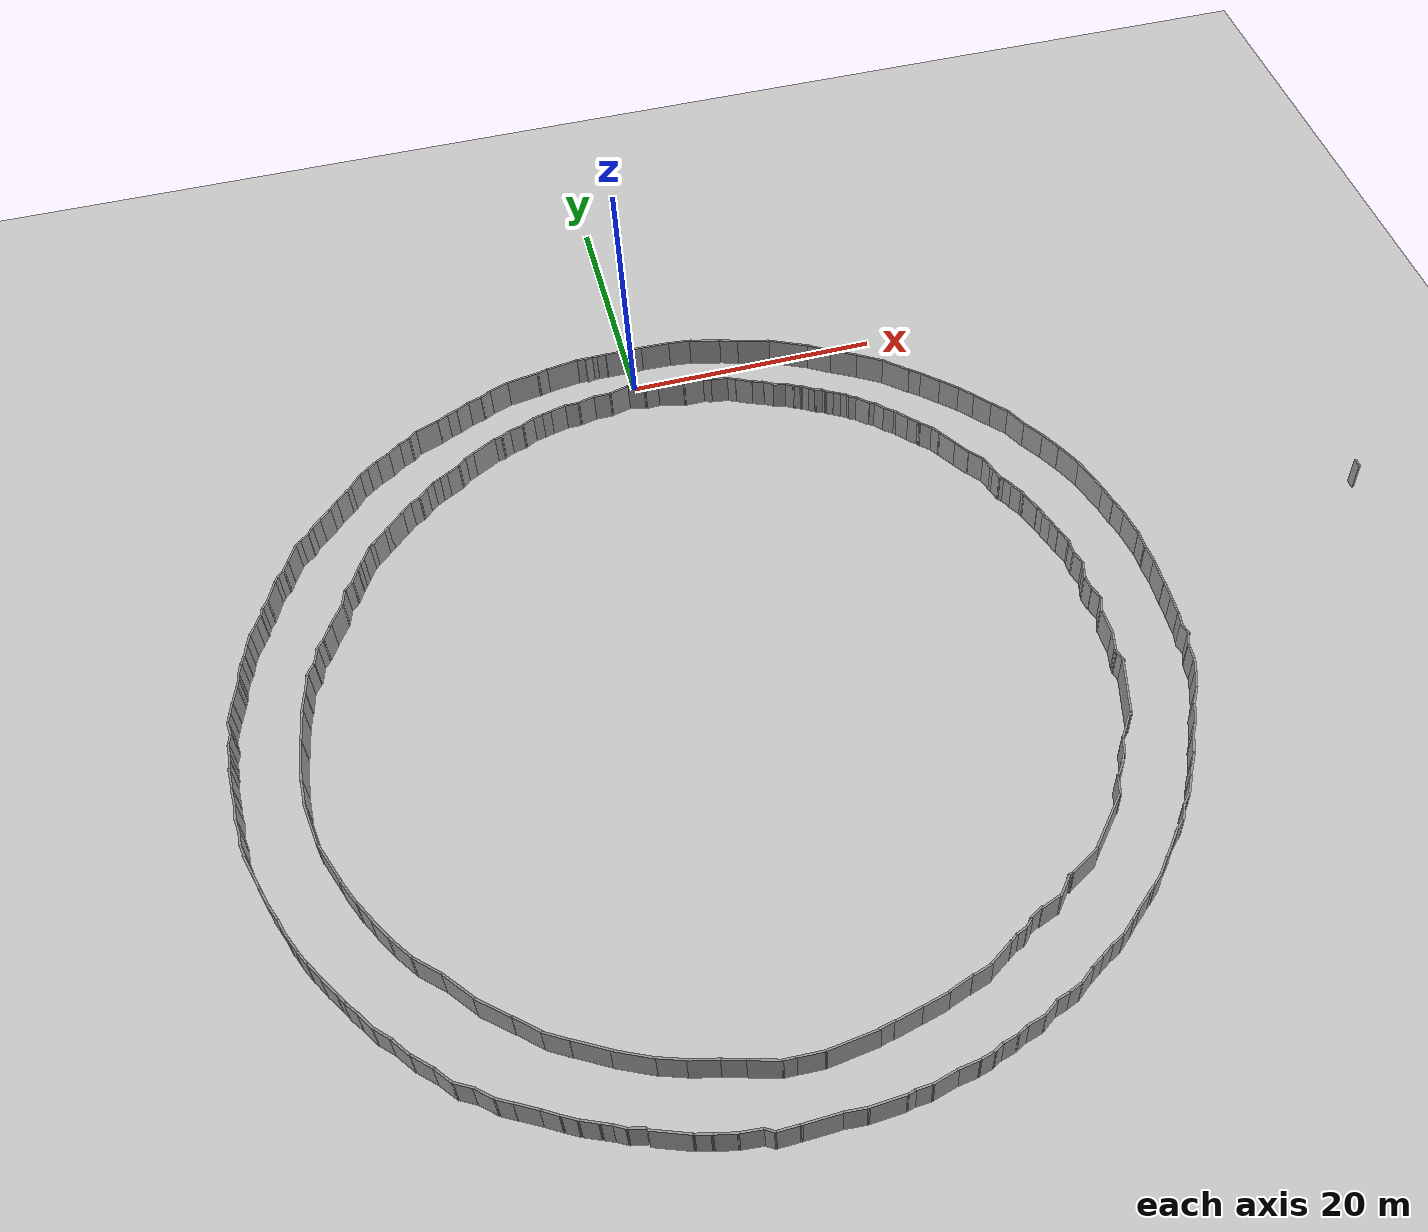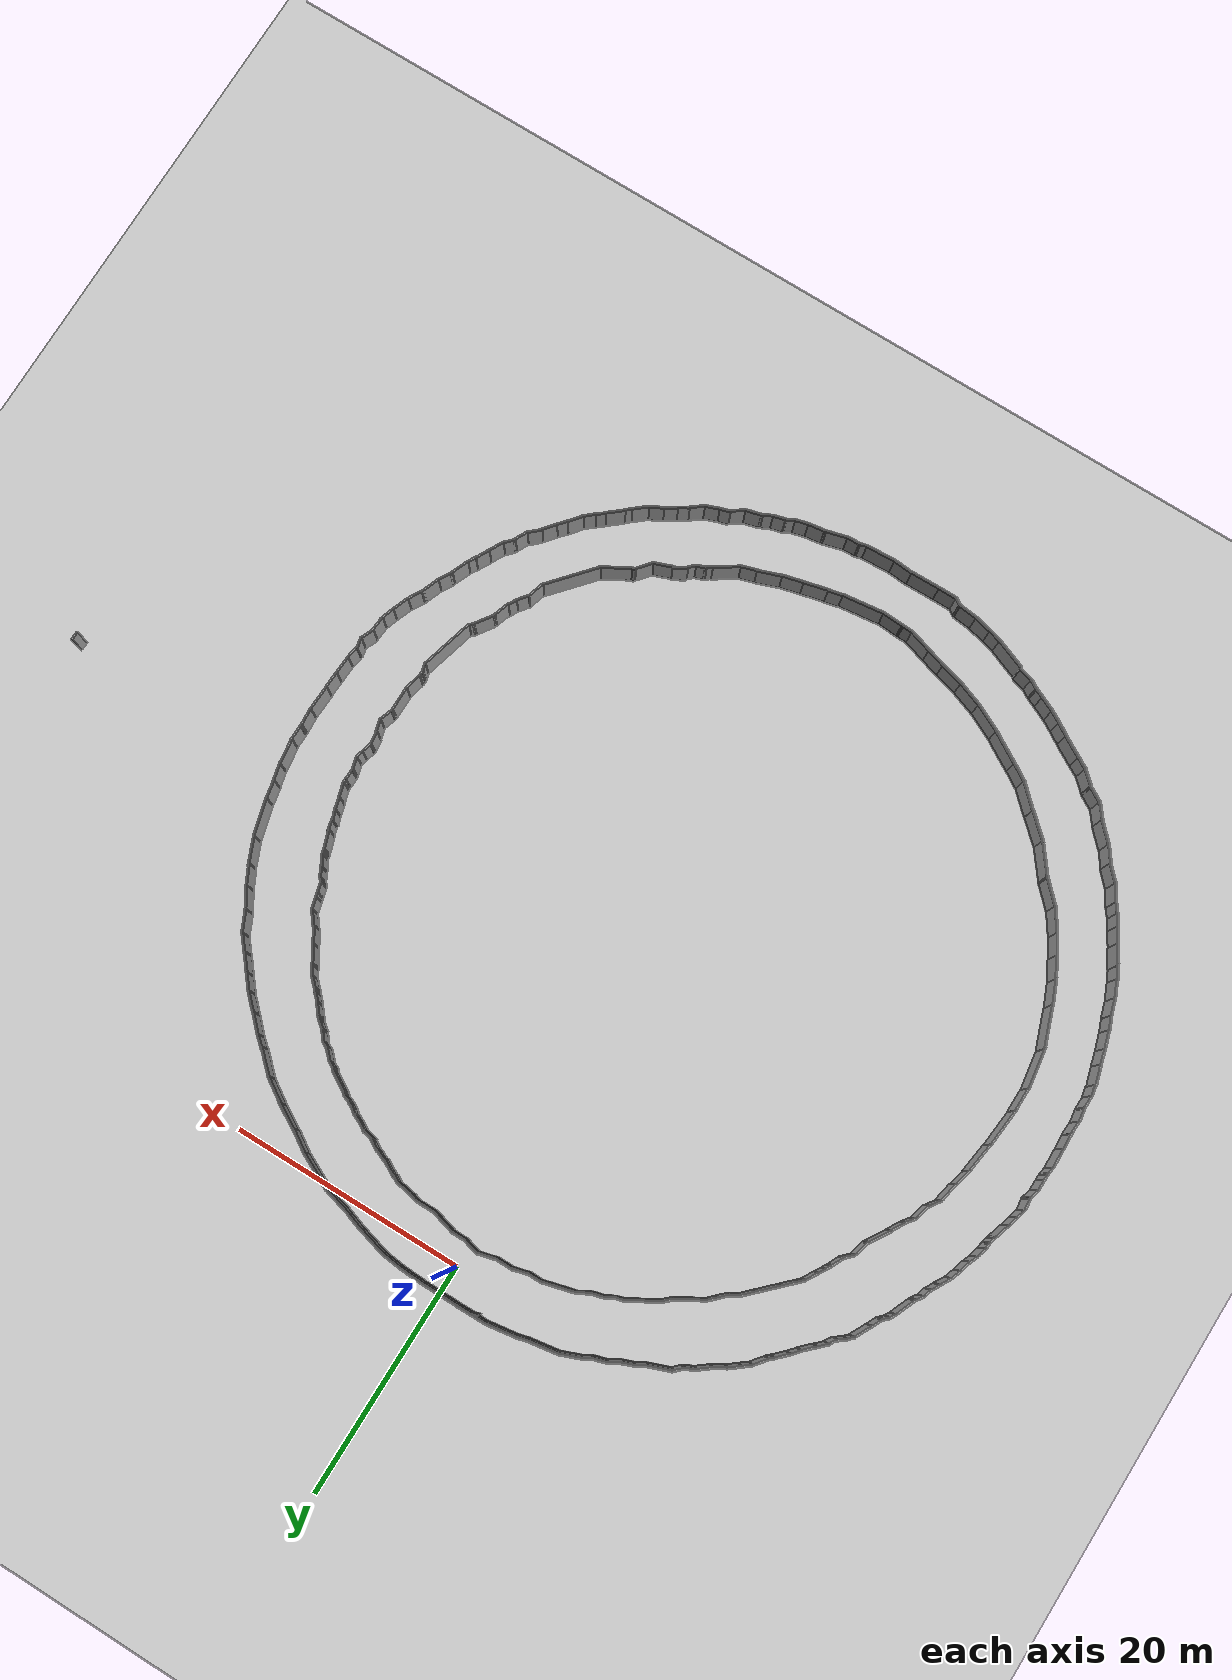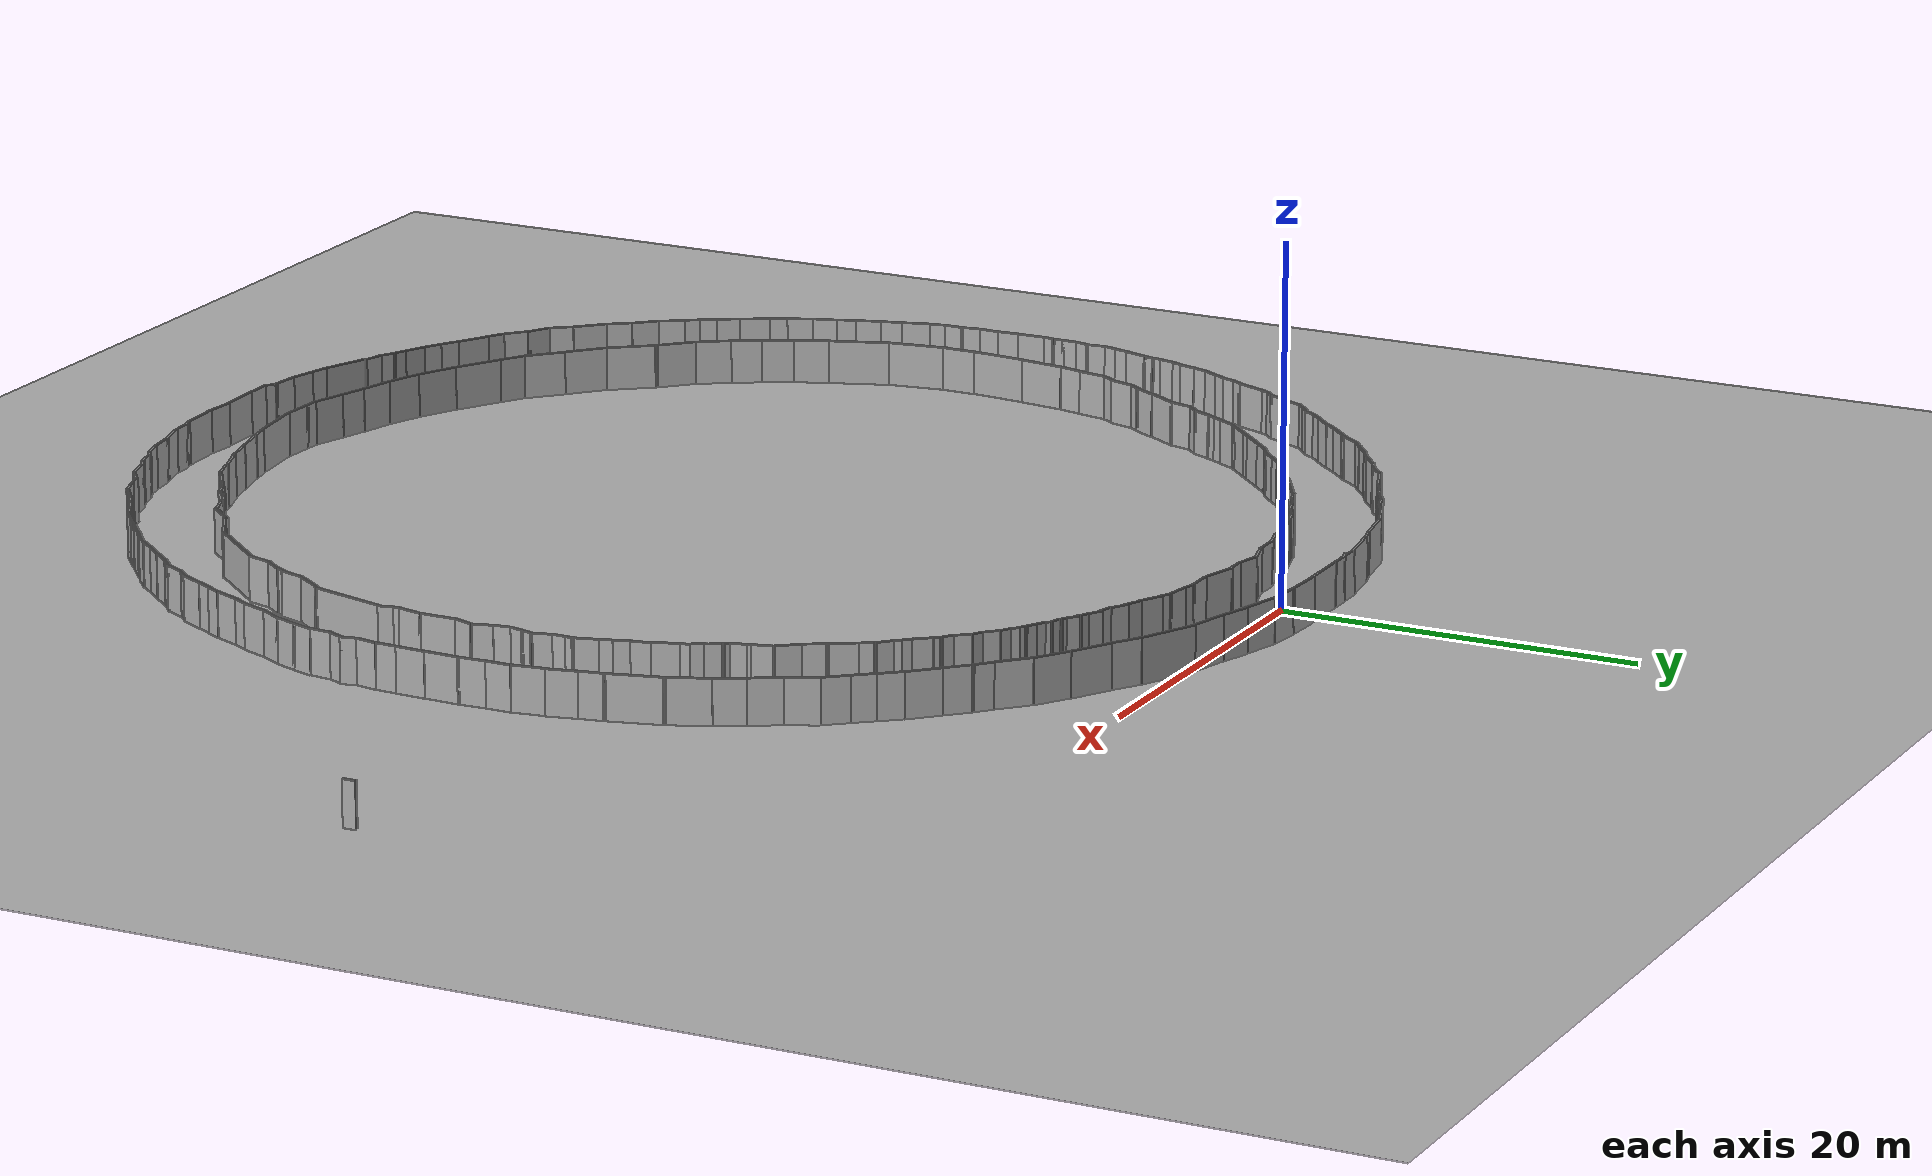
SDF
<sdf version="1.6">
 <world name="default">
  <light name="sun" type="directional">
   <pose>0 0 10 0 -0 0</pose>
   <diffuse>0.8 0.8 0.8 1</diffuse>
   <specular>0.1 0.1 0.1 1</specular>
   <attenuation>
    <range>1000</range>
    <constant>0.9</constant>
    <linear>0.01</linear>
    <quadratic>0.001</quadratic>
   </attenuation>
   <direction>-0.5 0.5 -1</direction>
  </light>
  <model name="ground_plane">
   <static>1</static>
   <link name="link">
    <collision name="collision">
     <geometry><plane><normal>0 0 1</normal><size>100 100</size></plane></geometry>
     <surface><friction><ode><mu>100</mu><mu2>50</mu2></ode></friction></surface>
    </collision>
    <visual name="visual">
     <cast_shadows>0</cast_shadows>
     <geometry><plane><normal>0 0 1</normal><size>100 100</size></plane></geometry>
     <material>
      <script><uri>file://media/materials/scripts/gazebo.material</uri><name>Gazebo/Grey</name></script>
     </material>
    </visual>
   </link>
  </model>
  <gravity>0 0 -9.8</gravity>
  <magnetic_field>6e-06 2.3e-05 -4.2e-05</magnetic_field>
  <atmosphere type="adiabatic"/>
  <physics name="default_physics" default="0" type="ode">
   <max_step_size>0.001</max_step_size>
   <real_time_factor>1</real_time_factor>
   <real_time_update_rate>1000</real_time_update_rate>
  </physics>
  <scene><ambient>0.4 0.4 0.4 1</ambient><background>0.7 0.7 0.7 1</background><shadows>1</shadows></scene>
  <spherical_coordinates>
   <surface_model>EARTH_WGS84</surface_model>
   <latitude_deg>0</latitude_deg>
   <longitude_deg>0</longitude_deg>
   <elevation>0</elevation>
   <heading_deg>0</heading_deg>
  </spherical_coordinates>
  <model name="yuvarlak_sonnn">
   <pose>8.74042 -31.6469 0 0 -0 0</pose>
   <link name="Wall_0">
    <collision name="Wall_0_Collision">
     <geometry><box><size>1.75 0.15 2.5</size></box></geometry>
     <pose>0 0 1.25 0 -0 0</pose>
    </collision>
    <visual name="Wall_0_Visual">
     <pose>0 0 1.25 0 -0 0</pose>
     <geometry><box><size>1.75 0.15 2.5</size></box></geometry>
     <material>
      <script><uri>file://media/materials/scripts/gazebo.material</uri><name>Gazebo/Grey</name></script>
      <ambient>1 1 1 1</ambient>
     </material>
    </visual>
    <pose>-12.1248 33.8367 0 0 -0 3.14159</pose>
   </link>
   <link name="Wall_1">
    <collision name="Wall_1_Collision">
     <geometry><box><size>2.72829 0.15 2.5</size></box></geometry>
     <pose>0 0 1.25 0 -0 0</pose>
    </collision>
    <visual name="Wall_1_Visual">
     <pose>0 0 1.25 0 -0 0</pose>
     <geometry><box><size>2.72829 0.15 2.5</size></box></geometry>
     <material>
      <script><uri>file://media/materials/scripts/gazebo.material</uri><name>Gazebo/Grey</name></script>
      <ambient>1 1 1 1</ambient>
     </material>
    </visual>
    <pose>-14.1992 33.6426 0 0 0 -2.99044</pose>
   </link>
   <link name="Wall_10">
    <collision name="Wall_10_Collision">
     <geometry><box><size>2.14763 0.15 2.5</size></box></geometry>
     <pose>0 0 1.25 0 -0 0</pose>
    </collision>
    <visual name="Wall_10_Visual">
     <pose>0 0 1.25 0 -0 0</pose>
     <geometry><box><size>2.14763 0.15 2.5</size></box></geometry>
     <material>
      <script><uri>file://media/materials/scripts/gazebo.material</uri><name>Gazebo/Grey</name></script>
      <ambient>1 1 1 1</ambient>
     </material>
    </visual>
    <pose>-25.8104 29.7111 0 0 0 -2.77887</pose>
   </link>
   <link name="Wall_100">
    <collision name="Wall_100_Collision">
     <geometry><box><size>1.5 0.15 2.5</size></box></geometry>
     <pose>0 0 1.25 0 -0 0</pose>
    </collision>
    <visual name="Wall_100_Visual">
     <pose>0 0 1.25 0 -0 0</pose>
     <geometry><box><size>1.5 0.15 2.5</size></box></geometry>
     <material>
      <script><uri>file://media/materials/scripts/gazebo.material</uri><name>Gazebo/Grey</name></script>
      <ambient>1 1 1 1</ambient>
     </material>
    </visual>
    <pose>3.07036 -31.3705 0 0 -0 0.261799</pose>
   </link>
   <link name="Wall_101">
    <collision name="Wall_101_Collision">
     <geometry><box><size>1.42727 0.15 2.5</size></box></geometry>
     <pose>0 0 1.25 0 -0 0</pose>
    </collision>
    <visual name="Wall_101_Visual">
     <pose>0 0 1.25 0 -0 0</pose>
     <geometry><box><size>1.42727 0.15 2.5</size></box></geometry>
     <material>
      <script><uri>file://media/materials/scripts/gazebo.material</uri><name>Gazebo/Grey</name></script>
      <ambient>1 1 1 1</ambient>
     </material>
    </visual>
    <pose>4.2711 -30.8225 0 0 -0 0.624356</pose>
   </link>
   <link name="Wall_102">
    <collision name="Wall_102_Collision">
     <geometry><box><size>1.0851 0.15 2.5</size></box></geometry>
     <pose>0 0 1.25 0 -0 0</pose>
    </collision>
    <visual name="Wall_102_Visual">
     <pose>0 0 1.25 0 -0 0</pose>
     <geometry><box><size>1.0851 0.15 2.5</size></box></geometry>
     <material>
      <script><uri>file://media/materials/scripts/gazebo.material</uri><name>Gazebo/Grey</name></script>
      <ambient>1 1 1 1</ambient>
     </material>
    </visual>
    <pose>5.21765 -30.297 0 0 -0 0.286317</pose>
   </link>
   <link name="Wall_103">
    <collision name="Wall_103_Collision">
     <geometry><box><size>1.24414 0.15 2.5</size></box></geometry>
     <pose>0 0 1.25 0 -0 0</pose>
    </collision>
    <visual name="Wall_103_Visual">
     <pose>0 0 1.25 0 -0 0</pose>
     <geometry><box><size>1.24414 0.15 2.5</size></box></geometry>
     <material>
      <script><uri>file://media/materials/scripts/gazebo.material</uri><name>Gazebo/Grey</name></script>
      <ambient>1 1 1 1</ambient>
     </material>
    </visual>
    <pose>6.15726 -29.9702 0 0 -0 0.364101</pose>
   </link>
   <link name="Wall_104">
    <collision name="Wall_104_Collision">
     <geometry><box><size>1.47845 0.15 2.5</size></box></geometry>
     <pose>0 0 1.25 0 -0 0</pose>
    </collision>
    <visual name="Wall_104_Visual">
     <pose>0 0 1.25 0 -0 0</pose>
     <geometry><box><size>1.47845 0.15 2.5</size></box></geometry>
     <material>
      <script><uri>file://media/materials/scripts/gazebo.material</uri><name>Gazebo/Grey</name></script>
      <ambient>1 1 1 1</ambient>
     </material>
    </visual>
    <pose>7.2128 -29.3674 0 0 -0 0.66124</pose>
   </link>
   <link name="Wall_105">
    <collision name="Wall_105_Collision">
     <geometry><box><size>1.11262 0.15 2.5</size></box></geometry>
     <pose>0 0 1.25 0 -0 0</pose>
    </collision>
    <visual name="Wall_105_Visual">
     <pose>0 0 1.25 0 -0 0</pose>
     <geometry><box><size>1.11262 0.15 2.5</size></box></geometry>
     <material>
      <script><uri>file://media/materials/scripts/gazebo.material</uri><name>Gazebo/Grey</name></script>
      <ambient>1 1 1 1</ambient>
     </material>
    </visual>
    <pose>8.12806 -28.7093 0 0 -0 0.546743</pose>
   </link>
   <link name="Wall_106">
    <collision name="Wall_106_Collision">
     <geometry><box><size>1.26237 0.15 2.5</size></box></geometry>
     <pose>0 0 1.25 0 -0 0</pose>
    </collision>
    <visual name="Wall_106_Visual">
     <pose>0 0 1.25 0 -0 0</pose>
     <geometry><box><size>1.26237 0.15 2.5</size></box></geometry>
     <material>
      <script><uri>file://media/materials/scripts/gazebo.material</uri><name>Gazebo/Grey</name></script>
      <ambient>1 1 1 1</ambient>
     </material>
    </visual>
    <pose>8.98845 -28.1607 0 0 -0 0.566293</pose>
   </link>
   <link name="Wall_107">
    <collision name="Wall_107_Collision">
     <geometry><box><size>1.23903 0.15 2.5</size></box></geometry>
     <pose>0 0 1.25 0 -0 0</pose>
    </collision>
    <visual name="Wall_107_Visual">
     <pose>0 0 1.25 0 -0 0</pose>
     <geometry><box><size>1.23903 0.15 2.5</size></box></geometry>
     <material>
      <script><uri>file://media/materials/scripts/gazebo.material</uri><name>Gazebo/Grey</name></script>
      <ambient>1 1 1 1</ambient>
     </material>
    </visual>
    <pose>9.92407 -27.6175 0 0 -0 0.466349</pose>
   </link>
   <link name="Wall_108">
    <collision name="Wall_108_Collision">
     <geometry><box><size>1.50096 0.15 2.5</size></box></geometry>
     <pose>0 0 1.25 0 -0 0</pose>
    </collision>
    <visual name="Wall_108_Visual">
     <pose>0 0 1.25 0 -0 0</pose>
     <geometry><box><size>1.50096 0.15 2.5</size></box></geometry>
     <material>
      <script><uri>file://media/materials/scripts/gazebo.material</uri><name>Gazebo/Grey</name></script>
      <ambient>1 1 1 1</ambient>
     </material>
    </visual>
    <pose>10.9447 -26.9346 0 0 -0 0.705649</pose>
   </link>
   <link name="Wall_109">
    <collision name="Wall_109_Collision">
     <geometry><box><size>0.858084 0.15 2.5</size></box></geometry>
     <pose>0 0 1.25 0 -0 0</pose>
    </collision>
    <visual name="Wall_109_Visual">
     <pose>0 0 1.25 0 -0 0</pose>
     <geometry><box><size>0.858084 0.15 2.5</size></box></geometry>
     <material>
      <script><uri>file://media/materials/scripts/gazebo.material</uri><name>Gazebo/Grey</name></script>
      <ambient>1 1 1 1</ambient>
     </material>
    </visual>
    <pose>11.7187 -26.2761 0 0 -0 0.746849</pose>
   </link>
   <link name="Wall_11">
    <collision name="Wall_11_Collision">
     <geometry><box><size>1 0.15 2.5</size></box></geometry>
     <pose>0 0 1.25 0 -0 0</pose>
    </collision>
    <visual name="Wall_11_Visual">
     <pose>0 0 1.25 0 -0 0</pose>
     <geometry><box><size>1 0.15 2.5</size></box></geometry>
     <material>
      <script><uri>file://media/materials/scripts/gazebo.material</uri><name>Gazebo/Grey</name></script>
      <ambient>1 1 1 1</ambient>
     </material>
    </visual>
    <pose>-27.0448 29.0562 0 0 0 -2.35619</pose>
   </link>
   <link name="Wall_110">
    <collision name="Wall_110_Collision">
     <geometry><box><size>1.72755 0.15 2.5</size></box></geometry>
     <pose>0 0 1.25 0 -0 0</pose>
    </collision>
    <visual name="Wall_110_Visual">
     <pose>0 0 1.25 0 -0 0</pose>
     <geometry><box><size>1.72755 0.15 2.5</size></box></geometry>
     <material>
      <script><uri>file://media/materials/scripts/gazebo.material</uri><name>Gazebo/Grey</name></script>
      <ambient>1 1 1 1</ambient>
     </material>
    </visual>
    <pose>12.5647 -25.5311 0 0 -0 0.693986</pose>
   </link>
   <link name="Wall_111">
    <collision name="Wall_111_Collision">
     <geometry><box><size>0.824869 0.15 2.5</size></box></geometry>
     <pose>0 0 1.25 0 -0 0</pose>
    </collision>
    <visual name="Wall_111_Visual">
     <pose>0 0 1.25 0 -0 0</pose>
     <geometry><box><size>0.824869 0.15 2.5</size></box></geometry>
     <material>
      <script><uri>file://media/materials/scripts/gazebo.material</uri><name>Gazebo/Grey</name></script>
      <ambient>1 1 1 1</ambient>
     </material>
    </visual>
    <pose>13.4335 -24.7838 0 0 -0 0.67983</pose>
   </link>
   <link name="Wall_112">
    <collision name="Wall_112_Collision">
     <geometry><box><size>1.3167 0.15 2.5</size></box></geometry>
     <pose>0 0 1.25 0 -0 0</pose>
    </collision>
    <visual name="Wall_112_Visual">
     <pose>0 0 1.25 0 -0 0</pose>
     <geometry><box><size>1.3167 0.15 2.5</size></box></geometry>
     <material>
      <script><uri>file://media/materials/scripts/gazebo.material</uri><name>Gazebo/Grey</name></script>
      <ambient>1 1 1 1</ambient>
     </material>
    </visual>
    <pose>14.1307 -24.2134 0 0 -0 0.72975</pose>
   </link>
   <link name="Wall_113">
    <collision name="Wall_113_Collision">
     <geometry><box><size>1.33483 0.15 2.5</size></box></geometry>
     <pose>0 0 1.25 0 -0 0</pose>
    </collision>
    <visual name="Wall_113_Visual">
     <pose>0 0 1.25 0 -0 0</pose>
     <geometry><box><size>1.33483 0.15 2.5</size></box></geometry>
     <material>
      <script><uri>file://media/materials/scripts/gazebo.material</uri><name>Gazebo/Grey</name></script>
      <ambient>1 1 1 1</ambient>
     </material>
    </visual>
    <pose>14.9006 -23.3584 0 0 -0 0.905511</pose>
   </link>
   <link name="Wall_114">
    <collision name="Wall_114_Collision">
     <geometry><box><size>1.19384 0.15 2.5</size></box></geometry>
     <pose>0 0 1.25 0 -0 0</pose>
    </collision>
    <visual name="Wall_114_Visual">
     <pose>0 0 1.25 0 -0 0</pose>
     <geometry><box><size>1.19384 0.15 2.5</size></box></geometry>
     <material>
      <script><uri>file://media/materials/scripts/gazebo.material</uri><name>Gazebo/Grey</name></script>
      <ambient>1 1 1 1</ambient>
     </material>
    </visual>
    <pose>15.6416 -22.5005 0 0 -0 0.849315</pose>
   </link>
   <link name="Wall_115">
    <collision name="Wall_115_Collision">
     <geometry><box><size>1.40101 0.15 2.5</size></box></geometry>
     <pose>0 0 1.25 0 -0 0</pose>
    </collision>
    <visual name="Wall_115_Visual">
     <pose>0 0 1.25 0 -0 0</pose>
     <geometry><box><size>1.40101 0.15 2.5</size></box></geometry>
     <material>
      <script><uri>file://media/materials/scripts/gazebo.material</uri><name>Gazebo/Grey</name></script>
      <ambient>1 1 1 1</ambient>
     </material>
    </visual>
    <pose>16.3609 -21.6234 0 0 -0 0.887897</pose>
   </link>
   <link name="Wall_116">
    <collision name="Wall_116_Collision">
     <geometry><box><size>1.24258 0.15 2.5</size></box></geometry>
     <pose>0 0 1.25 0 -0 0</pose>
    </collision>
    <visual name="Wall_116_Visual">
     <pose>0 0 1.25 0 -0 0</pose>
     <geometry><box><size>1.24258 0.15 2.5</size></box></geometry>
     <material>
      <script><uri>file://media/materials/scripts/gazebo.material</uri><name>Gazebo/Grey</name></script>
      <ambient>1 1 1 1</ambient>
     </material>
    </visual>
    <pose>17.1372 -20.7678 0 0 -0 0.744804</pose>
   </link>
   <link name="Wall_117">
    <collision name="Wall_117_Collision">
     <geometry><box><size>1.37168 0.15 2.5</size></box></geometry>
     <pose>0 0 1.25 0 -0 0</pose>
    </collision>
    <visual name="Wall_117_Visual">
     <pose>0 0 1.25 0 -0 0</pose>
     <geometry><box><size>1.37168 0.15 2.5</size></box></geometry>
     <material>
      <script><uri>file://media/materials/scripts/gazebo.material</uri><name>Gazebo/Grey</name></script>
      <ambient>1 1 1 1</ambient>
     </material>
    </visual>
    <pose>17.8361 -19.8532 0 0 -0 1.09984</pose>
   </link>
   <link name="Wall_118">
    <collision name="Wall_118_Collision">
     <geometry><box><size>1.00834 0.15 2.5</size></box></geometry>
     <pose>0 0 1.25 0 -0 0</pose>
    </collision>
    <visual name="Wall_118_Visual">
     <pose>0 0 1.25 0 -0 0</pose>
     <geometry><box><size>1.00834 0.15 2.5</size></box></geometry>
     <material>
      <script><uri>file://media/materials/scripts/gazebo.material</uri><name>Gazebo/Grey</name></script>
      <ambient>1 1 1 1</ambient>
     </material>
    </visual>
    <pose>18.3915 -19.0004 0 0 -0 0.801969</pose>
   </link>
   <link name="Wall_119">
    <collision name="Wall_119_Collision">
     <geometry><box><size>1.58797 0.15 2.5</size></box></geometry>
     <pose>0 0 1.25 0 -0 0</pose>
    </collision>
    <visual name="Wall_119_Visual">
     <pose>0 0 1.25 0 -0 0</pose>
     <geometry><box><size>1.58797 0.15 2.5</size></box></geometry>
     <material>
      <script><uri>file://media/materials/scripts/gazebo.material</uri><name>Gazebo/Grey</name></script>
      <ambient>1 1 1 1</ambient>
     </material>
    </visual>
    <pose>19.0475 -18.0571 0 0 -0 1.08217</pose>
   </link>
   <link name="Wall_12">
    <collision name="Wall_12_Collision">
     <geometry><box><size>1.1633 0.15 2.5</size></box></geometry>
     <pose>0 0 1.25 0 -0 0</pose>
    </collision>
    <visual name="Wall_12_Visual">
     <pose>0 0 1.25 0 -0 0</pose>
     <geometry><box><size>1.1633 0.15 2.5</size></box></geometry>
     <material>
      <script><uri>file://media/materials/scripts/gazebo.material</uri><name>Gazebo/Grey</name></script>
      <ambient>1 1 1 1</ambient>
     </material>
    </visual>
    <pose>-27.7967 28.5256 0 0 0 -2.67011</pose>
   </link>
   <link name="Wall_120">
    <collision name="Wall_120_Collision">
     <geometry><box><size>1.23903 0.15 2.5</size></box></geometry>
     <pose>0 0 1.25 0 -0 0</pose>
    </collision>
    <visual name="Wall_120_Visual">
     <pose>0 0 1.25 0 -0 0</pose>
     <geometry><box><size>1.23903 0.15 2.5</size></box></geometry>
     <material>
      <script><uri>file://media/materials/scripts/gazebo.material</uri><name>Gazebo/Grey</name></script>
      <ambient>1 1 1 1</ambient>
     </material>
    </visual>
    <pose>19.6231 -16.9428 0 0 -0 1.07682</pose>
   </link>
   <link name="Wall_121">
    <collision name="Wall_121_Collision">
     <geometry><box><size>1 0.15 2.5</size></box></geometry>
     <pose>0 0 1.25 0 -0 0</pose>
    </collision>
    <visual name="Wall_121_Visual">
     <pose>0 0 1.25 0 -0 0</pose>
     <geometry><box><size>1 0.15 2.5</size></box></geometry>
     <material>
      <script><uri>file://media/materials/scripts/gazebo.material</uri><name>Gazebo/Grey</name></script>
      <ambient>1 1 1 1</ambient>
     </material>
    </visual>
    <pose>20.1139 -16.0953 0 0 -0 1.0472</pose>
   </link>
   <link name="Wall_122">
    <collision name="Wall_122_Collision">
     <geometry><box><size>1.69231 0.15 2.5</size></box></geometry>
     <pose>0 0 1.25 0 -0 0</pose>
    </collision>
    <visual name="Wall_122_Visual">
     <pose>0 0 1.25 0 -0 0</pose>
     <geometry><box><size>1.69231 0.15 2.5</size></box></geometry>
     <material>
      <script><uri>file://media/materials/scripts/gazebo.material</uri><name>Gazebo/Grey</name></script>
      <ambient>1 1 1 1</ambient>
     </material>
    </visual>
    <pose>20.6017 -15.0149 0 0 -0 1.17771</pose>
   </link>
   <link name="Wall_123">
    <collision name="Wall_123_Collision">
     <geometry><box><size>1.25 0.15 2.5</size></box></geometry>
     <pose>0 0 1.25 0 -0 0</pose>
    </collision>
    <visual name="Wall_123_Visual">
     <pose>0 0 1.25 0 -0 0</pose>
     <geometry><box><size>1.25 0.15 2.5</size></box></geometry>
     <material>
      <script><uri>file://media/materials/scripts/gazebo.material</uri><name>Gazebo/Grey</name></script>
      <ambient>1 1 1 1</ambient>
     </material>
    </visual>
    <pose>21.1519 -13.8464 0 0 -0 1.0472</pose>
   </link>
   <link name="Wall_124">
    <collision name="Wall_124_Collision">
     <geometry><box><size>1.78247 0.15 2.5</size></box></geometry>
     <pose>0 0 1.25 0 -0 0</pose>
    </collision>
    <visual name="Wall_124_Visual">
     <pose>0 0 1.25 0 -0 0</pose>
     <geometry><box><size>1.78247 0.15 2.5</size></box></geometry>
     <material>
      <script><uri>file://media/materials/scripts/gazebo.material</uri><name>Gazebo/Grey</name></script>
      <ambient>1 1 1 1</ambient>
     </material>
    </visual>
    <pose>21.7364 -12.5868 0 0 -0 1.20839</pose>
   </link>
   <link name="Wall_125">
    <collision name="Wall_125_Collision">
     <geometry><box><size>1.5 0.15 2.5</size></box></geometry>
     <pose>0 0 1.25 0 -0 0</pose>
    </collision>
    <visual name="Wall_125_Visual">
     <pose>0 0 1.25 0 -0 0</pose>
     <geometry><box><size>1.5 0.15 2.5</size></box></geometry>
     <material>
      <script><uri>file://media/materials/scripts/gazebo.material</uri><name>Gazebo/Grey</name></script>
      <ambient>1 1 1 1</ambient>
     </material>
    </visual>
    <pose>22.3633 -11.2591 0 0 -0 1.0472</pose>
   </link>
   <link name="Wall_126">
    <collision name="Wall_126_Collision">
     <geometry><box><size>1.52629 0.15 2.5</size></box></geometry>
     <pose>0 0 1.25 0 -0 0</pose>
    </collision>
    <visual name="Wall_126_Visual">
     <pose>0 0 1.25 0 -0 0</pose>
     <geometry><box><size>1.52629 0.15 2.5</size></box></geometry>
     <material>
      <script><uri>file://media/materials/scripts/gazebo.material</uri><name>Gazebo/Grey</name></script>
      <ambient>1 1 1 1</ambient>
     </material>
    </visual>
    <pose>22.9453 -10.0112 0 0 -0 1.2076</pose>
   </link>
   <link name="Wall_127">
    <collision name="Wall_127_Collision">
     <geometry><box><size>1.33509 0.15 2.5</size></box></geometry>
     <pose>0 0 1.25 0 -0 0</pose>
    </collision>
    <visual name="Wall_127_Visual">
     <pose>0 0 1.25 0 -0 0</pose>
     <geometry><box><size>1.33509 0.15 2.5</size></box></geometry>
     <material>
      <script><uri>file://media/materials/scripts/gazebo.material</uri><name>Gazebo/Grey</name></script>
      <ambient>1 1 1 1</ambient>
     </material>
    </visual>
    <pose>23.378 -8.80605 0 0 -0 1.24752</pose>
   </link>
   <link name="Wall_128">
    <collision name="Wall_128_Collision">
     <geometry><box><size>1.36924 0.15 2.5</size></box></geometry>
     <pose>0 0 1.25 0 -0 0</pose>
    </collision>
    <visual name="Wall_128_Visual">
     <pose>0 0 1.25 0 -0 0</pose>
     <geometry><box><size>1.36924 0.15 2.5</size></box></geometry>
     <material>
      <script><uri>file://media/materials/scripts/gazebo.material</uri><name>Gazebo/Grey</name></script>
      <ambient>1 1 1 1</ambient>
     </material>
    </visual>
    <pose>23.5937 -7.63736 0 0 -0 1.47531</pose>
   </link>
   <link name="Wall_129">
    <collision name="Wall_129_Collision">
     <geometry><box><size>1.20468 0.15 2.5</size></box></geometry>
     <pose>0 0 1.25 0 -0 0</pose>
    </collision>
    <visual name="Wall_129_Visual">
     <pose>0 0 1.25 0 -0 0</pose>
     <geometry><box><size>1.20468 0.15 2.5</size></box></geometry>
     <material>
      <script><uri>file://media/materials/scripts/gazebo.material</uri><name>Gazebo/Grey</name></script>
      <ambient>1 1 1 1</ambient>
     </material>
    </visual>
    <pose>23.8384 -6.54996 0 0 -0 1.14639</pose>
   </link>
   <link name="Wall_13">
    <collision name="Wall_13_Collision">
     <geometry><box><size>1.34384 0.15 2.5</size></box></geometry>
     <pose>0 0 1.25 0 -0 0</pose>
    </collision>
    <visual name="Wall_13_Visual">
     <pose>0 0 1.25 0 -0 0</pose>
     <geometry><box><size>1.34384 0.15 2.5</size></box></geometry>
     <material>
      <script><uri>file://media/materials/scripts/gazebo.material</uri><name>Gazebo/Grey</name></script>
      <ambient>1 1 1 1</ambient>
     </material>
    </visual>
    <pose>-28.6973 27.9267 0 0 0 -2.47561</pose>
   </link>
   <link name="Wall_130">
    <collision name="Wall_130_Collision">
     <geometry><box><size>1.05244 0.15 2.5</size></box></geometry>
     <pose>0 0 1.25 0 -0 0</pose>
    </collision>
    <visual name="Wall_130_Visual">
     <pose>0 0 1.25 0 -0 0</pose>
     <geometry><box><size>1.05244 0.15 2.5</size></box></geometry>
     <material>
      <script><uri>file://media/materials/scripts/gazebo.material</uri><name>Gazebo/Grey</name></script>
      <ambient>1 1 1 1</ambient>
     </material>
    </visual>
    <pose>23.9824 -5.63028 0 0 -0 1.8028</pose>
   </link>
   <link name="Wall_131">
    <collision name="Wall_131_Collision">
     <geometry><box><size>1.28879 0.15 2.5</size></box></geometry>
     <pose>0 0 1.25 0 -0 0</pose>
    </collision>
    <visual name="Wall_131_Visual">
     <pose>0 0 1.25 0 -0 0</pose>
     <geometry><box><size>1.28879 0.15 2.5</size></box></geometry>
     <material>
      <script><uri>file://media/materials/scripts/gazebo.material</uri><name>Gazebo/Grey</name></script>
      <ambient>1 1 1 1</ambient>
     </material>
    </visual>
    <pose>24.0142 -4.63151 0 0 -0 1.38539</pose>
   </link>
   <link name="Wall_132">
    <collision name="Wall_132_Collision">
     <geometry><box><size>1.53245 0.15 2.5</size></box></geometry>
     <pose>0 0 1.25 0 -0 0</pose>
    </collision>
    <visual name="Wall_132_Visual">
     <pose>0 0 1.25 0 -0 0</pose>
     <geometry><box><size>1.53245 0.15 2.5</size></box></geometry>
     <material>
      <script><uri>file://media/materials/scripts/gazebo.material</uri><name>Gazebo/Grey</name></script>
      <ambient>1 1 1 1</ambient>
     </material>
    </visual>
    <pose>24.1244 -3.38158 0 0 -0 1.51894</pose>
   </link>
   <link name="Wall_133">
    <collision name="Wall_133_Collision">
     <geometry><box><size>1.71826 0.15 2.5</size></box></geometry>
     <pose>0 0 1.25 0 -0 0</pose>
    </collision>
    <visual name="Wall_133_Visual">
     <pose>0 0 1.25 0 -0 0</pose>
     <geometry><box><size>1.71826 0.15 2.5</size></box></geometry>
     <material>
      <script><uri>file://media/materials/scripts/gazebo.material</uri><name>Gazebo/Grey</name></script>
      <ambient>1 1 1 1</ambient>
     </material>
    </visual>
    <pose>24.198 -1.93866 0 0 -0 1.52261</pose>
   </link>
   <link name="Wall_134">
    <collision name="Wall_134_Collision">
     <geometry><box><size>2.22141 0.15 2.5</size></box></geometry>
     <pose>0 0 1.25 0 -0 0</pose>
    </collision>
    <visual name="Wall_134_Visual">
     <pose>0 0 1.25 0 -0 0</pose>
     <geometry><box><size>2.22141 0.15 2.5</size></box></geometry>
     <material>
      <script><uri>file://media/materials/scripts/gazebo.material</uri><name>Gazebo/Grey</name></script>
      <ambient>1 1 1 1</ambient>
     </material>
    </visual>
    <pose>24.2507 -0.120733 0 0 -0 1.52688</pose>
   </link>
   <link name="Wall_135">
    <collision name="Wall_135_Collision">
     <geometry><box><size>1.67425 0.15 2.5</size></box></geometry>
     <pose>0 0 1.25 0 -0 0</pose>
    </collision>
    <visual name="Wall_135_Visual">
     <pose>0 0 1.25 0 -0 0</pose>
     <geometry><box><size>1.67425 0.15 2.5</size></box></geometry>
     <material>
      <script><uri>file://media/materials/scripts/gazebo.material</uri><name>Gazebo/Grey</name></script>
      <ambient>1 1 1 1</ambient>
     </material>
    </visual>
    <pose>24.2494 1.70525 0 0 -0 1.63214</pose>
   </link>
   <link name="Wall_136">
    <collision name="Wall_136_Collision">
     <geometry><box><size>1.56151 0.15 2.5</size></box></geometry>
     <pose>0 0 1.25 0 -0 0</pose>
    </collision>
    <visual name="Wall_136_Visual">
     <pose>0 0 1.25 0 -0 0</pose>
     <geometry><box><size>1.56151 0.15 2.5</size></box></geometry>
     <material>
      <script><uri>file://media/materials/scripts/gazebo.material</uri><name>Gazebo/Grey</name></script>
      <ambient>1 1 1 1</ambient>
     </material>
    </visual>
    <pose>24.218 3.14095 0 0 -0 1.54912</pose>
   </link>
   <link name="Wall_137">
    <collision name="Wall_137_Collision">
     <geometry><box><size>2.14335 0.15 2.5</size></box></geometry>
     <pose>0 0 1.25 0 -0 0</pose>
    </collision>
    <visual name="Wall_137_Visual">
     <pose>0 0 1.25 0 -0 0</pose>
     <geometry><box><size>2.14335 0.15 2.5</size></box></geometry>
     <material>
      <script><uri>file://media/materials/scripts/gazebo.material</uri><name>Gazebo/Grey</name></script>
      <ambient>1 1 1 1</ambient>
     </material>
    </visual>
    <pose>24.0632 4.83341 0 0 -0 1.71117</pose>
   </link>
   <link name="Wall_138">
    <collision name="Wall_138_Collision">
     <geometry><box><size>1.71566 0.15 2.5</size></box></geometry>
     <pose>0 0 1.25 0 -0 0</pose>
    </collision>
    <visual name="Wall_138_Visual">
     <pose>0 0 1.25 0 -0 0</pose>
     <geometry><box><size>1.71566 0.15 2.5</size></box></geometry>
     <material>
      <script><uri>file://media/materials/scripts/gazebo.material</uri><name>Gazebo/Grey</name></script>
      <ambient>1 1 1 1</ambient>
     </material>
    </visual>
    <pose>23.7779 6.58296 0 0 -0 1.79817</pose>
   </link>
   <link name="Wall_139">
    <collision name="Wall_139_Collision">
     <geometry><box><size>1.60282 0.15 2.5</size></box></geometry>
     <pose>0 0 1.25 0 -0 0</pose>
    </collision>
    <visual name="Wall_139_Visual">
     <pose>0 0 1.25 0 -0 0</pose>
     <geometry><box><size>1.60282 0.15 2.5</size></box></geometry>
     <material>
      <script><uri>file://media/materials/scripts/gazebo.material</uri><name>Gazebo/Grey</name></script>
      <ambient>1 1 1 1</ambient>
     </material>
    </visual>
    <pose>23.4362 8.05945 0 0 -0 1.75733</pose>
   </link>
   <link name="Wall_14">
    <collision name="Wall_14_Collision">
     <geometry><box><size>1.25 0.15 2.5</size></box></geometry>
     <pose>0 0 1.25 0 -0 0</pose>
    </collision>
    <visual name="Wall_14_Visual">
     <pose>0 0 1.25 0 -0 0</pose>
     <geometry><box><size>1.25 0.15 2.5</size></box></geometry>
     <material>
      <script><uri>file://media/materials/scripts/gazebo.material</uri><name>Gazebo/Grey</name></script>
      <ambient>1 1 1 1</ambient>
     </material>
    </visual>
    <pose>-29.643 27.2628 0 0 0 -2.61799</pose>
   </link>
   <link name="Wall_140">
    <collision name="Wall_140_Collision">
     <geometry><box><size>3.25 0.15 2.5</size></box></geometry>
     <pose>0 0 1.25 0 -0 0</pose>
    </collision>
    <visual name="Wall_140_Visual">
     <pose>0 0 1.25 0 -0 0</pose>
     <geometry><box><size>3.25 0.15 2.5</size></box></geometry>
     <material>
      <script><uri>file://media/materials/scripts/gazebo.material</uri><name>Gazebo/Grey</name></script>
      <ambient>1 1 1 1</ambient>
     </material>
    </visual>
    <pose>22.9003 10.2704 0 0 -0 1.8326</pose>
   </link>
   <link name="Wall_141">
    <collision name="Wall_141_Collision">
     <geometry><box><size>2.47557 0.15 2.5</size></box></geometry>
     <pose>0 0 1.25 0 -0 0</pose>
    </collision>
    <visual name="Wall_141_Visual">
     <pose>0 0 1.25 0 -0 0</pose>
     <geometry><box><size>2.47557 0.15 2.5</size></box></geometry>
     <material>
      <script><uri>file://media/materials/scripts/gazebo.material</uri><name>Gazebo/Grey</name></script>
      <ambient>1 1 1 1</ambient>
     </material>
    </visual>
    <pose>22.0445 12.8379 0 0 -0 1.97247</pose>
   </link>
   <link name="Wall_142">
    <collision name="Wall_142_Collision">
     <geometry><box><size>1.90004 0.15 2.5</size></box></geometry>
     <pose>0 0 1.25 0 -0 0</pose>
    </collision>
    <visual name="Wall_142_Visual">
     <pose>0 0 1.25 0 -0 0</pose>
     <geometry><box><size>1.90004 0.15 2.5</size></box></geometry>
     <material>
      <script><uri>file://media/materials/scripts/gazebo.material</uri><name>Gazebo/Grey</name></script>
      <ambient>1 1 1 1</ambient>
     </material>
    </visual>
    <pose>21.1798 14.6713 0 0 -0 2.03268</pose>
   </link>
   <link name="Wall_143">
    <collision name="Wall_143_Collision">
     <geometry><box><size>2.02044 0.15 2.5</size></box></geometry>
     <pose>0 0 1.25 0 -0 0</pose>
    </collision>
    <visual name="Wall_143_Visual">
     <pose>0 0 1.25 0 -0 0</pose>
     <geometry><box><size>2.02044 0.15 2.5</size></box></geometry>
     <material>
      <script><uri>file://media/materials/scripts/gazebo.material</uri><name>Gazebo/Grey</name></script>
      <ambient>1 1 1 1</ambient>
     </material>
    </visual>
    <pose>20.3073 16.2356 0 0 -0 2.11302</pose>
   </link>
   <link name="Wall_144">
    <collision name="Wall_144_Collision">
     <geometry><box><size>2.02372 0.15 2.5</size></box></geometry>
     <pose>0 0 1.25 0 -0 0</pose>
    </collision>
    <visual name="Wall_144_Visual">
     <pose>0 0 1.25 0 -0 0</pose>
     <geometry><box><size>2.02372 0.15 2.5</size></box></geometry>
     <material>
      <script><uri>file://media/materials/scripts/gazebo.material</uri><name>Gazebo/Grey</name></script>
      <ambient>1 1 1 1</ambient>
     </material>
    </visual>
    <pose>19.4326 17.8679 0 0 -0 2.0024</pose>
   </link>
   <link name="Wall_145">
    <collision name="Wall_145_Collision">
     <geometry><box><size>1.67133 0.15 2.5</size></box></geometry>
     <pose>0 0 1.25 0 -0 0</pose>
    </collision>
    <visual name="Wall_145_Visual">
     <pose>0 0 1.25 0 -0 0</pose>
     <geometry><box><size>1.67133 0.15 2.5</size></box></geometry>
     <material>
      <script><uri>file://media/materials/scripts/gazebo.material</uri><name>Gazebo/Grey</name></script>
      <ambient>1 1 1 1</ambient>
     </material>
    </visual>
    <pose>18.5351 19.285 0 0 -0 2.26257</pose>
   </link>
   <link name="Wall_146">
    <collision name="Wall_146_Collision">
     <geometry><box><size>1.63137 0.15 2.5</size></box></geometry>
     <pose>0 0 1.25 0 -0 0</pose>
    </collision>
    <visual name="Wall_146_Visual">
     <pose>0 0 1.25 0 -0 0</pose>
     <geometry><box><size>1.63137 0.15 2.5</size></box></geometry>
     <material>
      <script><uri>file://media/materials/scripts/gazebo.material</uri><name>Gazebo/Grey</name></script>
      <ambient>1 1 1 1</ambient>
     </material>
    </visual>
    <pose>17.5795 20.4228 0 0 -0 2.25891</pose>
   </link>
   <link name="Wall_147">
    <collision name="Wall_147_Collision">
     <geometry><box><size>1.58845 0.15 2.5</size></box></geometry>
     <pose>0 0 1.25 0 -0 0</pose>
    </collision>
    <visual name="Wall_147_Visual">
     <pose>0 0 1.25 0 -0 0</pose>
     <geometry><box><size>1.58845 0.15 2.5</size></box></geometry>
     <material>
      <script><uri>file://media/materials/scripts/gazebo.material</uri><name>Gazebo/Grey</name></script>
      <ambient>1 1 1 1</ambient>
     </material>
    </visual>
    <pose>16.6509 21.5694 0 0 -0 2.26146</pose>
   </link>
   <link name="Wall_148">
    <collision name="Wall_148_Collision">
     <geometry><box><size>2 0.15 2.5</size></box></geometry>
     <pose>0 0 1.25 0 -0 0</pose>
    </collision>
    <visual name="Wall_148_Visual">
     <pose>0 0 1.25 0 -0 0</pose>
     <geometry><box><size>2 0.15 2.5</size></box></geometry>
     <material>
      <script><uri>file://media/materials/scripts/gazebo.material</uri><name>Gazebo/Grey</name></script>
      <ambient>1 1 1 1</ambient>
     </material>
    </visual>
    <pose>15.5588 22.7779 0 0 -0 2.35619</pose>
   </link>
   <link name="Wall_149">
    <collision name="Wall_149_Collision">
     <geometry><box><size>1.82124 0.15 2.5</size></box></geometry>
     <pose>0 0 1.25 0 -0 0</pose>
    </collision>
    <visual name="Wall_149_Visual">
     <pose>0 0 1.25 0 -0 0</pose>
     <geometry><box><size>1.82124 0.15 2.5</size></box></geometry>
     <material>
      <script><uri>file://media/materials/scripts/gazebo.material</uri><name>Gazebo/Grey</name></script>
      <ambient>1 1 1 1</ambient>
     </material>
    </visual>
    <pose>14.2977 24.0268 0 0 -0 2.34944</pose>
   </link>
   <link name="Wall_15">
    <collision name="Wall_15_Collision">
     <geometry><box><size>1.22954 0.15 2.5</size></box></geometry>
     <pose>0 0 1.25 0 -0 0</pose>
    </collision>
    <visual name="Wall_15_Visual">
     <pose>0 0 1.25 0 -0 0</pose>
     <geometry><box><size>1.22954 0.15 2.5</size></box></geometry>
     <material>
      <script><uri>file://media/materials/scripts/gazebo.material</uri><name>Gazebo/Grey</name></script>
      <ambient>1 1 1 1</ambient>
     </material>
    </visual>
    <pose>-30.5452 26.6562 0 0 0 -2.48018</pose>
   </link>
   <link name="Wall_150">
    <collision name="Wall_150_Collision">
     <geometry><box><size>1.2381 0.15 2.5</size></box></geometry>
     <pose>0 0 1.25 0 -0 0</pose>
    </collision>
    <visual name="Wall_150_Visual">
     <pose>0 0 1.25 0 -0 0</pose>
     <geometry><box><size>1.2381 0.15 2.5</size></box></geometry>
     <material>
      <script><uri>file://media/materials/scripts/gazebo.material</uri><name>Gazebo/Grey</name></script>
      <ambient>1 1 1 1</ambient>
     </material>
    </visual>
    <pose>13.3018 24.9804 0 0 -0 2.42159</pose>
   </link>
   <link name="Wall_151">
    <collision name="Wall_151_Collision">
     <geometry><box><size>2.40289 0.15 2.5</size></box></geometry>
     <pose>0 0 1.25 0 -0 0</pose>
    </collision>
    <visual name="Wall_151_Visual">
     <pose>0 0 1.25 0 -0 0</pose>
     <geometry><box><size>2.40289 0.15 2.5</size></box></geometry>
     <material>
      <script><uri>file://media/materials/scripts/gazebo.material</uri><name>Gazebo/Grey</name></script>
      <ambient>1 1 1 1</ambient>
     </material>
    </visual>
    <pose>12.0529 26.0916 0 0 -0 2.38584</pose>
   </link>
   <link name="Wall_154">
    <collision name="Wall_154_Collision">
     <geometry><box><size>2.39428 0.15 2.5</size></box></geometry>
     <pose>0 0 1.25 0 -0 0</pose>
    </collision>
    <visual name="Wall_154_Visual">
     <pose>0 0 1.25 0 -0 0</pose>
     <geometry><box><size>2.39428 0.15 2.5</size></box></geometry>
     <material>
      <script><uri>file://media/materials/scripts/gazebo.material</uri><name>Gazebo/Grey</name></script>
      <ambient>1 1 1 1</ambient>
     </material>
    </visual>
    <pose>10.3105 27.493 0 0 -0 2.56827</pose>
   </link>
   <link name="Wall_155">
    <collision name="Wall_155_Collision">
     <geometry><box><size>2.5 0.15 2.5</size></box></geometry>
     <pose>0 0 1.25 0 -0 0</pose>
    </collision>
    <visual name="Wall_155_Visual">
     <pose>0 0 1.25 0 -0 0</pose>
     <geometry><box><size>2.5 0.15 2.5</size></box></geometry>
     <material>
      <script><uri>file://media/materials/scripts/gazebo.material</uri><name>Gazebo/Grey</name></script>
      <ambient>1 1 1 1</ambient>
     </material>
    </visual>
    <pose>8.40374 28.6891 0 0 -0 2.61799</pose>
   </link>
   <link name="Wall_156">
    <collision name="Wall_156_Collision">
     <geometry><box><size>2.01077 0.15 2.5</size></box></geometry>
     <pose>0 0 1.25 0 -0 0</pose>
    </collision>
    <visual name="Wall_156_Visual">
     <pose>0 0 1.25 0 -0 0</pose>
     <geometry><box><size>2.01077 0.15 2.5</size></box></geometry>
     <material>
      <script><uri>file://media/materials/scripts/gazebo.material</uri><name>Gazebo/Grey</name></script>
      <ambient>1 1 1 1</ambient>
     </material>
    </visual>
    <pose>6.55302 29.7844 0 0 -0 2.56435</pose>
   </link>
   <link name="Wall_157">
    <collision name="Wall_157_Collision">
     <geometry><box><size>3.52899 0.15 2.5</size></box></geometry>
     <pose>0 0 1.25 0 -0 0</pose>
    </collision>
    <visual name="Wall_157_Visual">
     <pose>0 0 1.25 0 -0 0</pose>
     <geometry><box><size>3.52899 0.15 2.5</size></box></geometry>
     <material>
      <script><uri>file://media/materials/scripts/gazebo.material</uri><name>Gazebo/Grey</name></script>
      <ambient>1 1 1 1</ambient>
     </material>
    </visual>
    <pose>4.25608 31.0553 0 0 -0 2.68618</pose>
   </link>
   <link name="Wall_158">
    <collision name="Wall_158_Collision">
     <geometry><box><size>2.60619 0.15 2.5</size></box></geometry>
     <pose>0 0 1.25 0 -0 0</pose>
    </collision>
    <visual name="Wall_158_Visual">
     <pose>0 0 1.25 0 -0 0</pose>
     <geometry><box><size>2.60619 0.15 2.5</size></box></geometry>
     <material>
      <script><uri>file://media/materials/scripts/gazebo.material</uri><name>Gazebo/Grey</name></script>
      <ambient>1 1 1 1</ambient>
     </material>
    </visual>
    <pose>1.55261 32.0964 0 0 -0 2.87956</pose>
   </link>
   <link name="Wall_159">
    <collision name="Wall_159_Collision">
     <geometry><box><size>1.77801 0.15 2.5</size></box></geometry>
     <pose>0 0 1.25 0 -0 0</pose>
    </collision>
    <visual name="Wall_159_Visual">
     <pose>0 0 1.25 0 -0 0</pose>
     <geometry><box><size>1.77801 0.15 2.5</size></box></geometry>
     <material>
      <script><uri>file://media/materials/scripts/gazebo.material</uri><name>Gazebo/Grey</name></script>
      <ambient>1 1 1 1</ambient>
     </material>
    </visual>
    <pose>-0.40447 32.696 0 0 -0 2.81472</pose>
   </link>
   <link name="Wall_16">
    <collision name="Wall_16_Collision">
     <geometry><box><size>0.850612 0.15 2.5</size></box></geometry>
     <pose>0 0 1.25 0 -0 0</pose>
    </collision>
    <visual name="Wall_16_Visual">
     <pose>0 0 1.25 0 -0 0</pose>
     <geometry><box><size>0.850612 0.15 2.5</size></box></geometry>
     <material>
      <script><uri>file://media/materials/scripts/gazebo.material</uri><name>Gazebo/Grey</name></script>
      <ambient>1 1 1 1</ambient>
     </material>
    </visual>
    <pose>-31.2519 26.095 0 0 0 -2.50044</pose>
   </link>
   <link name="Wall_160">
    <collision name="Wall_160_Collision">
     <geometry><box><size>2.5 0.15 2.5</size></box></geometry>
     <pose>0 0 1.25 0 -0 0</pose>
    </collision>
    <visual name="Wall_160_Visual">
     <pose>0 0 1.25 0 -0 0</pose>
     <geometry><box><size>2.5 0.15 2.5</size></box></geometry>
     <material>
      <script><uri>file://media/materials/scripts/gazebo.material</uri><name>Gazebo/Grey</name></script>
      <ambient>1 1 1 1</ambient>
     </material>
    </visual>
    <pose>-2.31034 33.2414 0 0 -0 2.87979</pose>
   </link>
   <link name="Wall_161">
    <collision name="Wall_161_Collision">
     <geometry><box><size>1.96781 0.15 2.5</size></box></geometry>
     <pose>0 0 1.25 0 -0 0</pose>
    </collision>
    <visual name="Wall_161_Visual">
     <pose>0 0 1.25 0 -0 0</pose>
     <geometry><box><size>1.96781 0.15 2.5</size></box></geometry>
     <material>
      <script><uri>file://media/materials/scripts/gazebo.material</uri><name>Gazebo/Grey</name></script>
      <ambient>1 1 1 1</ambient>
     </material>
    </visual>
    <pose>-4.34884 33.6642 0 0 -0 3.03288</pose>
   </link>
   <link name="Wall_162">
    <collision name="Wall_162_Collision">
     <geometry><box><size>2.52148 0.15 2.5</size></box></geometry>
     <pose>0 0 1.25 0 -0 0</pose>
    </collision>
    <visual name="Wall_162_Visual">
     <pose>0 0 1.25 0 -0 0</pose>
     <geometry><box><size>2.52148 0.15 2.5</size></box></geometry>
     <material>
      <script><uri>file://media/materials/scripts/gazebo.material</uri><name>Gazebo/Grey</name></script>
      <ambient>1 1 1 1</ambient>
     </material>
    </visual>
    <pose>-6.43743 33.8131 0 0 -0 3.09919</pose>
   </link>
   <link name="Wall_163">
    <collision name="Wall_163_Collision">
     <geometry><box><size>3 0.15 2.5</size></box></geometry>
     <pose>0 0 1.25 0 -0 0</pose>
    </collision>
    <visual name="Wall_163_Visual">
     <pose>0 0 1.25 0 -0 0</pose>
     <geometry><box><size>3 0.15 2.5</size></box></geometry>
     <material>
      <script><uri>file://media/materials/scripts/gazebo.material</uri><name>Gazebo/Grey</name></script>
      <ambient>1 1 1 1</ambient>
     </material>
    </visual>
    <pose>-9.04749 33.8433 0 0 -0 3.14159</pose>
   </link>
   <link name="Wall_164">
    <collision name="Wall_164_Collision">
     <geometry><box><size>0.182988 0.15 2.5</size></box></geometry>
     <pose>0 0 1.25 0 -0 0</pose>
    </collision>
    <visual name="Wall_164_Visual">
     <pose>0 0 1.25 0 -0 0</pose>
     <geometry><box><size>0.182988 0.15 2.5</size></box></geometry>
     <material>
      <script><uri>file://media/materials/scripts/gazebo.material</uri><name>Gazebo/Grey</name></script>
      <ambient>1 1 1 1</ambient>
     </material>
    </visual>
    <pose>-10.4874 33.8564 0 0 0 -2.70446</pose>
   </link>
   <link name="Wall_165">
    <collision name="Wall_165_Collision">
     <geometry><box><size>1.25 0.15 2.5</size></box></geometry>
     <pose>0 0 1.25 0 -0 0</pose>
    </collision>
    <visual name="Wall_165_Visual">
     <pose>0 0 1.25 0 -0 0</pose>
     <geometry><box><size>1.25 0.15 2.5</size></box></geometry>
     <material>
      <script><uri>file://media/materials/scripts/gazebo.material</uri><name>Gazebo/Grey</name></script>
      <ambient>1 1 1 1</ambient>
     </material>
    </visual>
    <pose>-11.0524 33.8494 0 0 -0 3.14159</pose>
   </link>
   <link name="Wall_166">
    <collision name="Wall_166_Collision">
     <geometry><box><size>0.75 0.15 2.5</size></box></geometry>
     <pose>0 0 1.25 0 -0 0</pose>
    </collision>
    <visual name="Wall_166_Visual">
     <pose>0 0 1.25 0 -0 0</pose>
     <geometry><box><size>0.75 0.15 2.5</size></box></geometry>
     <material>
      <script><uri>file://media/materials/scripts/gazebo.material</uri><name>Gazebo/Grey</name></script>
      <ambient>1 1 1 1</ambient>
     </material>
    </visual>
    <pose>-11.8922 33.7718 0 0 0 -2.87979</pose>
   </link>
   <link name="Wall_17">
    <collision name="Wall_17_Collision">
     <geometry><box><size>1.59545 0.15 2.5</size></box></geometry>
     <pose>0 0 1.25 0 -0 0</pose>
    </collision>
    <visual name="Wall_17_Visual">
     <pose>0 0 1.25 0 -0 0</pose>
     <geometry><box><size>1.59545 0.15 2.5</size></box></geometry>
     <material>
      <script><uri>file://media/materials/scripts/gazebo.material</uri><name>Gazebo/Grey</name></script>
      <ambient>1 1 1 1</ambient>
     </material>
    </visual>
    <pose>-31.9798 25.3378 0 0 0 -2.23785</pose>
   </link>
   <link name="Wall_18">
    <collision name="Wall_18_Collision">
     <geometry><box><size>0.617622 0.15 2.5</size></box></geometry>
     <pose>0 0 1.25 0 -0 0</pose>
    </collision>
    <visual name="Wall_18_Visual">
     <pose>0 0 1.25 0 -0 0</pose>
     <geometry><box><size>0.617622 0.15 2.5</size></box></geometry>
     <material>
      <script><uri>file://media/materials/scripts/gazebo.material</uri><name>Gazebo/Grey</name></script>
      <ambient>1 1 1 1</ambient>
     </material>
    </visual>
    <pose>-32.5861 24.62 0 0 0 -2.44508</pose>
   </link>
   <link name="Wall_184">
    <collision name="Wall_184_Collision">
     <geometry><box><size>0.75 0.15 2.5</size></box></geometry>
     <pose>0 0 1.25 0 -0 0</pose>
    </collision>
    <visual name="Wall_184_Visual">
     <pose>0 0 1.25 0 -0 0</pose>
     <geometry><box><size>0.75 0.15 2.5</size></box></geometry>
     <material>
      <script><uri>file://media/materials/scripts/gazebo.material</uri><name>Gazebo/Grey</name></script>
      <ambient>1 1 1 1</ambient>
     </material>
    </visual>
    <pose>-32.7119 16.5989 0 0 0 -2.0944</pose>
   </link>
   <link name="Wall_186">
    <collision name="Wall_186_Collision">
     <geometry><box><size>0.75 0.15 2.5</size></box></geometry>
     <pose>0 0 1.25 0 -0 0</pose>
    </collision>
    <visual name="Wall_186_Visual">
     <pose>0 0 1.25 0 -0 0</pose>
     <geometry><box><size>0.75 0.15 2.5</size></box></geometry>
     <material>
      <script><uri>file://media/materials/scripts/gazebo.material</uri><name>Gazebo/Grey</name></script>
      <ambient>1 1 1 1</ambient>
     </material>
    </visual>
    <pose>-32.4119 17.1185 0 0 -0 1.0472</pose>
   </link>
   <link name="Wall_187">
    <collision name="Wall_187_Collision">
     <geometry><box><size>1.25 0.15 2.5</size></box></geometry>
     <pose>0 0 1.25 0 -0 0</pose>
    </collision>
    <visual name="Wall_187_Visual">
     <pose>0 0 1.25 0 -0 0</pose>
     <geometry><box><size>1.25 0.15 2.5</size></box></geometry>
     <material>
      <script><uri>file://media/materials/scripts/gazebo.material</uri><name>Gazebo/Grey</name></script>
      <ambient>1 1 1 1</ambient>
     </material>
    </visual>
    <pose>-31.9869 17.8546 0 0 -0 1.0472</pose>
   </link>
   <link name="Wall_188">
    <collision name="Wall_188_Collision">
     <geometry><box><size>0.5 0.15 2.5</size></box></geometry>
     <pose>0 0 1.25 0 -0 0</pose>
    </collision>
    <visual name="Wall_188_Visual">
     <pose>0 0 1.25 0 -0 0</pose>
     <geometry><box><size>0.5 0.15 2.5</size></box></geometry>
     <material>
      <script><uri>file://media/materials/scripts/gazebo.material</uri><name>Gazebo/Grey</name></script>
      <ambient>1 1 1 1</ambient>
     </material>
    </visual>
    <pose>-31.5881 18.4547 0 0 -0 0.785398</pose>
   </link>
   <link name="Wall_189">
    <collision name="Wall_189_Collision">
     <geometry><box><size>1.5 0.15 2.5</size></box></geometry>
     <pose>0 0 1.25 0 -0 0</pose>
    </collision>
    <visual name="Wall_189_Visual">
     <pose>0 0 1.25 0 -0 0</pose>
     <geometry><box><size>1.5 0.15 2.5</size></box></geometry>
     <material>
      <script><uri>file://media/materials/scripts/gazebo.material</uri><name>Gazebo/Grey</name></script>
      <ambient>1 1 1 1</ambient>
     </material>
    </visual>
    <pose>-30.9871 19.0557 0 0 -0 0.785398</pose>
   </link>
   <link name="Wall_190">
    <collision name="Wall_190_Collision">
     <geometry><box><size>0.75 0.15 2.5</size></box></geometry>
     <pose>0 0 1.25 0 -0 0</pose>
    </collision>
    <visual name="Wall_190_Visual">
     <pose>0 0 1.25 0 -0 0</pose>
     <geometry><box><size>0.75 0.15 2.5</size></box></geometry>
     <material>
      <script><uri>file://media/materials/scripts/gazebo.material</uri><name>Gazebo/Grey</name></script>
      <ambient>1 1 1 1</ambient>
     </material>
    </visual>
    <pose>-30.2977 19.7452 0 0 -0 0.785398</pose>
   </link>
   <link name="Wall_191">
    <collision name="Wall_191_Collision">
     <geometry><box><size>1.75 0.15 2.5</size></box></geometry>
     <pose>0 0 1.25 0 -0 0</pose>
    </collision>
    <visual name="Wall_191_Visual">
     <pose>0 0 1.25 0 -0 0</pose>
     <geometry><box><size>1.75 0.15 2.5</size></box></geometry>
     <material>
      <script><uri>file://media/materials/scripts/gazebo.material</uri><name>Gazebo/Grey</name></script>
      <ambient>1 1 1 1</ambient>
     </material>
    </visual>
    <pose>-29.5199 20.523 0 0 -0 0.785398</pose>
   </link>
   <link name="Wall_192">
    <collision name="Wall_192_Collision">
     <geometry><box><size>1.25 0.15 2.5</size></box></geometry>
     <pose>0 0 1.25 0 -0 0</pose>
    </collision>
    <visual name="Wall_192_Visual">
     <pose>0 0 1.25 0 -0 0</pose>
     <geometry><box><size>1.25 0.15 2.5</size></box></geometry>
     <material>
      <script><uri>file://media/materials/scripts/gazebo.material</uri><name>Gazebo/Grey</name></script>
      <ambient>1 1 1 1</ambient>
     </material>
    </visual>
    <pose>-28.5653 21.4776 0 0 -0 0.785398</pose>
   </link>
   <link name="Wall_193">
    <collision name="Wall_193_Collision">
     <geometry><box><size>1 0.15 2.5</size></box></geometry>
     <pose>0 0 1.25 0 -0 0</pose>
    </collision>
    <visual name="Wall_193_Visual">
     <pose>0 0 1.25 0 -0 0</pose>
     <geometry><box><size>1 0.15 2.5</size></box></geometry>
     <material>
      <script><uri>file://media/materials/scripts/gazebo.material</uri><name>Gazebo/Grey</name></script>
      <ambient>1 1 1 1</ambient>
     </material>
    </visual>
    <pose>-27.8083 22.079 0 0 -0 0.523599</pose>
   </link>
   <link name="Wall_194">
    <collision name="Wall_194_Collision">
     <geometry><box><size>1 0.15 2.5</size></box></geometry>
     <pose>0 0 1.25 0 -0 0</pose>
    </collision>
    <visual name="Wall_194_Visual">
     <pose>0 0 1.25 0 -0 0</pose>
     <geometry><box><size>1 0.15 2.5</size></box></geometry>
     <material>
      <script><uri>file://media/materials/scripts/gazebo.material</uri><name>Gazebo/Grey</name></script>
      <ambient>1 1 1 1</ambient>
     </material>
    </visual>
    <pose>-27.1397 22.592 0 0 -0 0.785398</pose>
   </link>
   <link name="Wall_195">
    <collision name="Wall_195_Collision">
     <geometry><box><size>1 0.15 2.5</size></box></geometry>
     <pose>0 0 1.25 0 -0 0</pose>
    </collision>
    <visual name="Wall_195_Visual">
     <pose>0 0 1.25 0 -0 0</pose>
     <geometry><box><size>1 0.15 2.5</size></box></geometry>
     <material>
      <script><uri>file://media/materials/scripts/gazebo.material</uri><name>Gazebo/Grey</name></script>
      <ambient>1 1 1 1</ambient>
     </material>
    </visual>
    <pose>-26.5387 23.1931 0 0 -0 0.785398</pose>
   </link>
   <link name="Wall_196">
    <collision name="Wall_196_Collision">
     <geometry><box><size>0.75 0.15 2.5</size></box></geometry>
     <pose>0 0 1.25 0 -0 0</pose>
    </collision>
    <visual name="Wall_196_Visual">
     <pose>0 0 1.25 0 -0 0</pose>
     <geometry><box><size>0.75 0.15 2.5</size></box></geometry>
     <material>
      <script><uri>file://media/materials/scripts/gazebo.material</uri><name>Gazebo/Grey</name></script>
      <ambient>1 1 1 1</ambient>
     </material>
    </visual>
    <pose>-25.9783 23.6436 0 0 -0 0.523599</pose>
   </link>
   <link name="Wall_197">
    <collision name="Wall_197_Collision">
     <geometry><box><size>1 0.15 2.5</size></box></geometry>
     <pose>0 0 1.25 0 -0 0</pose>
    </collision>
    <visual name="Wall_197_Visual">
     <pose>0 0 1.25 0 -0 0</pose>
     <geometry><box><size>1 0.15 2.5</size></box></geometry>
     <material>
      <script><uri>file://media/materials/scripts/gazebo.material</uri><name>Gazebo/Grey</name></script>
      <ambient>1 1 1 1</ambient>
     </material>
    </visual>
    <pose>-25.3505 24.0061 0 0 -0 0.523599</pose>
   </link>
   <link name="Wall_198">
    <collision name="Wall_198_Collision">
     <geometry><box><size>1.25 0.15 2.5</size></box></geometry>
     <pose>0 0 1.25 0 -0 0</pose>
    </collision>
    <visual name="Wall_198_Visual">
     <pose>0 0 1.25 0 -0 0</pose>
     <geometry><box><size>1.25 0.15 2.5</size></box></geometry>
     <material>
      <script><uri>file://media/materials/scripts/gazebo.material</uri><name>Gazebo/Grey</name></script>
      <ambient>1 1 1 1</ambient>
     </material>
    </visual>
    <pose>-24.5061 24.4936 0 0 -0 0.523599</pose>
   </link>
   <link name="Wall_199">
    <collision name="Wall_199_Collision">
     <geometry><box><size>1 0.15 2.5</size></box></geometry>
     <pose>0 0 1.25 0 -0 0</pose>
    </collision>
    <visual name="Wall_199_Visual">
     <pose>0 0 1.25 0 -0 0</pose>
     <geometry><box><size>1 0.15 2.5</size></box></geometry>
     <material>
      <script><uri>file://media/materials/scripts/gazebo.material</uri><name>Gazebo/Grey</name></script>
      <ambient>1 1 1 1</ambient>
     </material>
    </visual>
    <pose>-23.7293 25.0691 0 0 -0 0.785398</pose>
   </link>
   <link name="Wall_2">
    <collision name="Wall_2_Collision">
     <geometry><box><size>1 0.15 2.5</size></box></geometry>
     <pose>0 0 1.25 0 -0 0</pose>
    </collision>
    <visual name="Wall_2_Visual">
     <pose>0 0 1.25 0 -0 0</pose>
     <geometry><box><size>1 0.15 2.5</size></box></geometry>
     <material>
      <script><uri>file://media/materials/scripts/gazebo.material</uri><name>Gazebo/Grey</name></script>
      <ambient>1 1 1 1</ambient>
     </material>
    </visual>
    <pose>-15.8842 33.3385 0 0 0 -2.87979</pose>
   </link>
   <link name="Wall_20">
    <collision name="Wall_20_Collision">
     <geometry><box><size>1.25 0.15 2.5</size></box></geometry>
     <pose>0 0 1.25 0 -0 0</pose>
    </collision>
    <visual name="Wall_20_Visual">
     <pose>0 0 1.25 0 -0 0</pose>
     <geometry><box><size>1.25 0.15 2.5</size></box></geometry>
     <material>
      <script><uri>file://media/materials/scripts/gazebo.material</uri><name>Gazebo/Grey</name></script>
      <ambient>1 1 1 1</ambient>
     </material>
    </visual>
    <pose>-33.1343 24.0811 0 0 0 -2.35619</pose>
   </link>
   <link name="Wall_200">
    <collision name="Wall_200_Collision">
     <geometry><box><size>1 0.15 2.5</size></box></geometry>
     <pose>0 0 1.25 0 -0 0</pose>
    </collision>
    <visual name="Wall_200_Visual">
     <pose>0 0 1.25 0 -0 0</pose>
     <geometry><box><size>1 0.15 2.5</size></box></geometry>
     <material>
      <script><uri>file://media/materials/scripts/gazebo.material</uri><name>Gazebo/Grey</name></script>
      <ambient>1 1 1 1</ambient>
     </material>
    </visual>
    <pose>-23.0607 25.5821 0 0 -0 0.523599</pose>
   </link>
   <link name="Wall_201">
    <collision name="Wall_201_Collision">
     <geometry><box><size>2.25 0.15 2.5</size></box></geometry>
     <pose>0 0 1.25 0 -0 0</pose>
    </collision>
    <visual name="Wall_201_Visual">
     <pose>0 0 1.25 0 -0 0</pose>
     <geometry><box><size>2.25 0.15 2.5</size></box></geometry>
     <material>
      <script><uri>file://media/materials/scripts/gazebo.material</uri><name>Gazebo/Grey</name></script>
      <ambient>1 1 1 1</ambient>
     </material>
    </visual>
    <pose>-21.7833 26.3196 0 0 -0 0.523599</pose>
   </link>
   <link name="Wall_202">
    <collision name="Wall_202_Collision">
     <geometry><box><size>0.75 0.15 2.5</size></box></geometry>
     <pose>0 0 1.25 0 -0 0</pose>
    </collision>
    <visual name="Wall_202_Visual">
     <pose>0 0 1.25 0 -0 0</pose>
     <geometry><box><size>0.75 0.15 2.5</size></box></geometry>
     <material>
      <script><uri>file://media/materials/scripts/gazebo.material</uri><name>Gazebo/Grey</name></script>
      <ambient>1 1 1 1</ambient>
     </material>
    </visual>
    <pose>-20.5842 26.9223 0 0 -0 0.261799</pose>
   </link>
   <link name="Wall_203">
    <collision name="Wall_203_Collision">
     <geometry><box><size>1 0.15 2.5</size></box></geometry>
     <pose>0 0 1.25 0 -0 0</pose>
    </collision>
    <visual name="Wall_203_Visual">
     <pose>0 0 1.25 0 -0 0</pose>
     <geometry><box><size>1 0.15 2.5</size></box></geometry>
     <material>
      <script><uri>file://media/materials/scripts/gazebo.material</uri><name>Gazebo/Grey</name></script>
      <ambient>1 1 1 1</ambient>
     </material>
    </visual>
    <pose>-19.9264 27.2124 0 0 -0 0.523599</pose>
   </link>
   <link name="Wall_204">
    <collision name="Wall_204_Collision">
     <geometry><box><size>1.25 0.15 2.5</size></box></geometry>
     <pose>0 0 1.25 0 -0 0</pose>
    </collision>
    <visual name="Wall_204_Visual">
     <pose>0 0 1.25 0 -0 0</pose>
     <geometry><box><size>1.25 0.15 2.5</size></box></geometry>
     <material>
      <script><uri>file://media/materials/scripts/gazebo.material</uri><name>Gazebo/Grey</name></script>
      <ambient>1 1 1 1</ambient>
     </material>
    </visual>
    <pose>-19.027 27.5673 0 0 -0 0.261799</pose>
   </link>
   <link name="Wall_205">
    <collision name="Wall_205_Collision">
     <geometry><box><size>1.25 0.15 2.5</size></box></geometry>
     <pose>0 0 1.25 0 -0 0</pose>
    </collision>
    <visual name="Wall_205_Visual">
     <pose>0 0 1.25 0 -0 0</pose>
     <geometry><box><size>1.25 0.15 2.5</size></box></geometry>
     <material>
      <script><uri>file://media/materials/scripts/gazebo.material</uri><name>Gazebo/Grey</name></script>
      <ambient>1 1 1 1</ambient>
     </material>
    </visual>
    <pose>-18.0195 27.9846 0 0 -0 0.523599</pose>
   </link>
   <link name="Wall_206">
    <collision name="Wall_206_Collision">
     <geometry><box><size>1 0.15 2.5</size></box></geometry>
     <pose>0 0 1.25 0 -0 0</pose>
    </collision>
    <visual name="Wall_206_Visual">
     <pose>0 0 1.25 0 -0 0</pose>
     <geometry><box><size>1 0.15 2.5</size></box></geometry>
     <material>
      <script><uri>file://media/materials/scripts/gazebo.material</uri><name>Gazebo/Grey</name></script>
      <ambient>1 1 1 1</ambient>
     </material>
    </visual>
    <pose>-17.1326 28.3696 0 0 -0 0.261799</pose>
   </link>
   <link name="Wall_207">
    <collision name="Wall_207_Collision">
     <geometry><box><size>0.75 0.15 2.5</size></box></geometry>
     <pose>0 0 1.25 0 -0 0</pose>
    </collision>
    <visual name="Wall_207_Visual">
     <pose>0 0 1.25 0 -0 0</pose>
     <geometry><box><size>0.75 0.15 2.5</size></box></geometry>
     <material>
      <script><uri>file://media/materials/scripts/gazebo.material</uri><name>Gazebo/Grey</name></script>
      <ambient>1 1 1 1</ambient>
     </material>
    </visual>
    <pose>-16.4323 28.5572 0 0 -0 0.261799</pose>
   </link>
   <link name="Wall_208">
    <collision name="Wall_208_Collision">
     <geometry><box><size>1.5 0.15 2.5</size></box></geometry>
     <pose>0 0 1.25 0 -0 0</pose>
    </collision>
    <visual name="Wall_208_Visual">
     <pose>0 0 1.25 0 -0 0</pose>
     <geometry><box><size>1.5 0.15 2.5</size></box></geometry>
     <material>
      <script><uri>file://media/materials/scripts/gazebo.material</uri><name>Gazebo/Grey</name></script>
      <ambient>1 1 1 1</ambient>
     </material>
    </visual>
    <pose>-15.4906 28.8096 0 0 -0 0.261799</pose>
   </link>
   <link name="Wall_209">
    <collision name="Wall_209_Collision">
     <geometry><box><size>1.25 0.15 2.5</size></box></geometry>
     <pose>0 0 1.25 0 -0 0</pose>
    </collision>
    <visual name="Wall_209_Visual">
     <pose>0 0 1.25 0 -0 0</pose>
     <geometry><box><size>1.25 0.15 2.5</size></box></geometry>
     <material>
      <script><uri>file://media/materials/scripts/gazebo.material</uri><name>Gazebo/Grey</name></script>
      <ambient>1 1 1 1</ambient>
     </material>
    </visual>
    <pose>-14.2886 28.9843 0 0 -0 0</pose>
   </link>
   <link name="Wall_21">
    <collision name="Wall_21_Collision">
     <geometry><box><size>1.17311 0.15 2.5</size></box></geometry>
     <pose>0 0 1.25 0 -0 0</pose>
    </collision>
    <visual name="Wall_21_Visual">
     <pose>0 0 1.25 0 -0 0</pose>
     <geometry><box><size>1.17311 0.15 2.5</size></box></geometry>
     <material>
      <script><uri>file://media/materials/scripts/gazebo.material</uri><name>Gazebo/Grey</name></script>
      <ambient>1 1 1 1</ambient>
     </material>
    </visual>
    <pose>-33.8765 23.304 0 0 0 -2.28011</pose>
   </link>
   <link name="Wall_210">
    <collision name="Wall_210_Collision">
     <geometry><box><size>1.5 0.15 2.5</size></box></geometry>
     <pose>0 0 1.25 0 -0 0</pose>
    </collision>
    <visual name="Wall_210_Visual">
     <pose>0 0 1.25 0 -0 0</pose>
     <geometry><box><size>1.5 0.15 2.5</size></box></geometry>
     <material>
      <script><uri>file://media/materials/scripts/gazebo.material</uri><name>Gazebo/Grey</name></script>
      <ambient>1 1 1 1</ambient>
     </material>
    </visual>
    <pose>-13.0866 29.159 0 0 -0 0.261799</pose>
   </link>
   <link name="Wall_211">
    <collision name="Wall_211_Collision">
     <geometry><box><size>1.5 0.15 2.5</size></box></geometry>
     <pose>0 0 1.25 0 -0 0</pose>
    </collision>
    <visual name="Wall_211_Visual">
     <pose>0 0 1.25 0 -0 0</pose>
     <geometry><box><size>1.5 0.15 2.5</size></box></geometry>
     <material>
      <script><uri>file://media/materials/scripts/gazebo.material</uri><name>Gazebo/Grey</name></script>
      <ambient>1 1 1 1</ambient>
     </material>
    </visual>
    <pose>-11.7596 29.3337 0 0 -0 0</pose>
   </link>
   <link name="Wall_212">
    <collision name="Wall_212_Collision">
     <geometry><box><size>1.75 0.15 2.5</size></box></geometry>
     <pose>0 0 1.25 0 -0 0</pose>
    </collision>
    <visual name="Wall_212_Visual">
     <pose>0 0 1.25 0 -0 0</pose>
     <geometry><box><size>1.75 0.15 2.5</size></box></geometry>
     <material>
      <script><uri>file://media/materials/scripts/gazebo.material</uri><name>Gazebo/Grey</name></script>
      <ambient>1 1 1 1</ambient>
     </material>
    </visual>
    <pose>-10.3118 29.5408 0 0 -0 0.261799</pose>
   </link>
   <link name="Wall_213">
    <collision name="Wall_213_Collision">
     <geometry><box><size>1.5 0.15 2.5</size></box></geometry>
     <pose>0 0 1.25 0 -0 0</pose>
    </collision>
    <visual name="Wall_213_Visual">
     <pose>0 0 1.25 0 -0 0</pose>
     <geometry><box><size>1.5 0.15 2.5</size></box></geometry>
     <material>
      <script><uri>file://media/materials/scripts/gazebo.material</uri><name>Gazebo/Grey</name></script>
      <ambient>1 1 1 1</ambient>
     </material>
    </visual>
    <pose>-8.88707 29.5731 0 0 0 -0.261799</pose>
   </link>
   <link name="Wall_214">
    <collision name="Wall_214_Collision">
     <geometry><box><size>1.25 0.15 2.5</size></box></geometry>
     <pose>0 0 1.25 0 -0 0</pose>
    </collision>
    <visual name="Wall_214_Visual">
     <pose>0 0 1.25 0 -0 0</pose>
     <geometry><box><size>1.25 0.15 2.5</size></box></geometry>
     <material>
      <script><uri>file://media/materials/scripts/gazebo.material</uri><name>Gazebo/Grey</name></script>
      <ambient>1 1 1 1</ambient>
     </material>
    </visual>
    <pose>-7.68507 29.3984 0 0 -0 0</pose>
   </link>
   <link name="Wall_215">
    <collision name="Wall_215_Collision">
     <geometry><box><size>2.25 0.15 2.5</size></box></geometry>
     <pose>0 0 1.25 0 -0 0</pose>
    </collision>
    <visual name="Wall_215_Visual">
     <pose>0 0 1.25 0 -0 0</pose>
     <geometry><box><size>2.25 0.15 2.5</size></box></geometry>
     <material>
      <script><uri>file://media/materials/scripts/gazebo.material</uri><name>Gazebo/Grey</name></script>
      <ambient>1 1 1 1</ambient>
     </material>
    </visual>
    <pose>-6.12085 29.1267 0 0 0 -0.261799</pose>
   </link>
   <link name="Wall_216">
    <collision name="Wall_216_Collision">
     <geometry><box><size>1.75 0.15 2.5</size></box></geometry>
     <pose>0 0 1.25 0 -0 0</pose>
    </collision>
    <visual name="Wall_216_Visual">
     <pose>0 0 1.25 0 -0 0</pose>
     <geometry><box><size>1.75 0.15 2.5</size></box></geometry>
     <material>
      <script><uri>file://media/materials/scripts/gazebo.material</uri><name>Gazebo/Grey</name></script>
      <ambient>1 1 1 1</ambient>
     </material>
    </visual>
    <pose>-4.30663 28.8549 0 0 -0 0</pose>
   </link>
   <link name="Wall_217">
    <collision name="Wall_217_Collision">
     <geometry><box><size>0.733235 0.15 2.5</size></box></geometry>
     <pose>0 0 1.25 0 -0 0</pose>
    </collision>
    <visual name="Wall_217_Visual">
     <pose>0 0 1.25 0 -0 0</pose>
     <geometry><box><size>0.733235 0.15 2.5</size></box></geometry>
     <material>
      <script><uri>file://media/materials/scripts/gazebo.material</uri><name>Gazebo/Grey</name></script>
      <ambient>1 1 1 1</ambient>
     </material>
    </visual>
    <pose>-3.2297 28.7635 0 0 0 -0.318755</pose>
   </link>
   <link name="Wall_218">
    <collision name="Wall_218_Collision">
     <geometry><box><size>1.5064 0.15 2.5</size></box></geometry>
     <pose>0 0 1.25 0 -0 0</pose>
    </collision>
    <visual name="Wall_218_Visual">
     <pose>0 0 1.25 0 -0 0</pose>
     <geometry><box><size>1.5064 0.15 2.5</size></box></geometry>
     <material>
      <script><uri>file://media/materials/scripts/gazebo.material</uri><name>Gazebo/Grey</name></script>
      <ambient>1 1 1 1</ambient>
     </material>
    </visual>
    <pose>-2.22213 28.5615 0 0 0 -0.163832</pose>
   </link>
   <link name="Wall_219">
    <collision name="Wall_219_Collision">
     <geometry><box><size>0.75 0.15 2.5</size></box></geometry>
     <pose>0 0 1.25 0 -0 0</pose>
    </collision>
    <visual name="Wall_219_Visual">
     <pose>0 0 1.25 0 -0 0</pose>
     <geometry><box><size>0.75 0.15 2.5</size></box></geometry>
     <material>
      <script><uri>file://media/materials/scripts/gazebo.material</uri><name>Gazebo/Grey</name></script>
      <ambient>1 1 1 1</ambient>
     </material>
    </visual>
    <pose>-1.2932 28.3009 0 0 0 -0.523599</pose>
   </link>
   <link name="Wall_22">
    <collision name="Wall_22_Collision">
     <geometry><box><size>1.25 0.15 2.5</size></box></geometry>
     <pose>0 0 1.25 0 -0 0</pose>
    </collision>
    <visual name="Wall_22_Visual">
     <pose>0 0 1.25 0 -0 0</pose>
     <geometry><box><size>1.25 0.15 2.5</size></box></geometry>
     <material>
      <script><uri>file://media/materials/scripts/gazebo.material</uri><name>Gazebo/Grey</name></script>
      <ambient>1 1 1 1</ambient>
     </material>
    </visual>
    <pose>-34.5785 22.5269 0 0 0 -2.35619</pose>
   </link>
   <link name="Wall_220">
    <collision name="Wall_220_Collision">
     <geometry><box><size>1.55362 0.15 2.5</size></box></geometry>
     <pose>0 0 1.25 0 -0 0</pose>
    </collision>
    <visual name="Wall_220_Visual">
     <pose>0 0 1.25 0 -0 0</pose>
     <geometry><box><size>1.55362 0.15 2.5</size></box></geometry>
     <material>
      <script><uri>file://media/materials/scripts/gazebo.material</uri><name>Gazebo/Grey</name></script>
      <ambient>1 1 1 1</ambient>
     </material>
    </visual>
    <pose>-0.418061 27.8749 0 0 0 -0.501679</pose>
   </link>
   <link name="Wall_221">
    <collision name="Wall_221_Collision">
     <geometry><box><size>1.12088 0.15 2.5</size></box></geometry>
     <pose>0 0 1.25 0 -0 0</pose>
    </collision>
    <visual name="Wall_221_Visual">
     <pose>0 0 1.25 0 -0 0</pose>
     <geometry><box><size>1.12088 0.15 2.5</size></box></geometry>
     <material>
      <script><uri>file://media/materials/scripts/gazebo.material</uri><name>Gazebo/Grey</name></script>
      <ambient>1 1 1 1</ambient>
     </material>
    </visual>
    <pose>0.638553 27.3967 0 0 0 -0.429829</pose>
   </link>
   <link name="Wall_222">
    <collision name="Wall_222_Collision">
     <geometry><box><size>1.08432 0.15 2.5</size></box></geometry>
     <pose>0 0 1.25 0 -0 0</pose>
    </collision>
    <visual name="Wall_222_Visual">
     <pose>0 0 1.25 0 -0 0</pose>
     <geometry><box><size>1.08432 0.15 2.5</size></box></geometry>
     <material>
      <script><uri>file://media/materials/scripts/gazebo.material</uri><name>Gazebo/Grey</name></script>
      <ambient>1 1 1 1</ambient>
     </material>
    </visual>
    <pose>1.47866 27.0126 0 0 0 -0.547705</pose>
   </link>
   <link name="Wall_223">
    <collision name="Wall_223_Collision">
     <geometry><box><size>1 0.15 2.5</size></box></geometry>
     <pose>0 0 1.25 0 -0 0</pose>
    </collision>
    <visual name="Wall_223_Visual">
     <pose>0 0 1.25 0 -0 0</pose>
     <geometry><box><size>1 0.15 2.5</size></box></geometry>
     <material>
      <script><uri>file://media/materials/scripts/gazebo.material</uri><name>Gazebo/Grey</name></script>
      <ambient>1 1 1 1</ambient>
     </material>
    </visual>
    <pose>2.288 26.5978 0 0 0 -0.261799</pose>
   </link>
   <link name="Wall_224">
    <collision name="Wall_224_Collision">
     <geometry><box><size>0.970754 0.15 2.5</size></box></geometry>
     <pose>0 0 1.25 0 -0 0</pose>
    </collision>
    <visual name="Wall_224_Visual">
     <pose>0 0 1.25 0 -0 0</pose>
     <geometry><box><size>0.970754 0.15 2.5</size></box></geometry>
     <material>
      <script><uri>file://media/materials/scripts/gazebo.material</uri><name>Gazebo/Grey</name></script>
      <ambient>1 1 1 1</ambient>
     </material>
    </visual>
    <pose>3.05051 26.3384 0 0 0 -0.539953</pose>
   </link>
   <link name="Wall_225">
    <collision name="Wall_225_Collision">
     <geometry><box><size>0.669272 0.15 2.5</size></box></geometry>
     <pose>0 0 1.25 0 -0 0</pose>
    </collision>
    <visual name="Wall_225_Visual">
     <pose>0 0 1.25 0 -0 0</pose>
     <geometry><box><size>0.669272 0.15 2.5</size></box></geometry>
     <material>
      <script><uri>file://media/materials/scripts/gazebo.material</uri><name>Gazebo/Grey</name></script>
      <ambient>1 1 1 1</ambient>
     </material>
    </visual>
    <pose>3.63921 26.0207 0 0 0 -0.423501</pose>
   </link>
   <link name="Wall_226">
    <collision name="Wall_226_Collision">
     <geometry><box><size>0.25 0.15 2.5</size></box></geometry>
     <pose>0 0 1.25 0 -0 0</pose>
    </collision>
    <visual name="Wall_226_Visual">
     <pose>0 0 1.25 0 -0 0</pose>
     <geometry><box><size>0.25 0.15 2.5</size></box></geometry>
     <material>
      <script><uri>file://media/materials/scripts/gazebo.material</uri><name>Gazebo/Grey</name></script>
      <ambient>1 1 1 1</ambient>
     </material>
    </visual>
    <pose>3.90091 25.8707 0 0 0 -1.0472</pose>
   </link>
   <link name="Wall_227">
    <collision name="Wall_227_Collision">
     <geometry><box><size>0.226399 0.15 2.5</size></box></geometry>
     <pose>0 0 1.25 0 -0 0</pose>
    </collision>
    <visual name="Wall_227_Visual">
     <pose>0 0 1.25 0 -0 0</pose>
     <geometry><box><size>0.226399 0.15 2.5</size></box></geometry>
     <material>
      <script><uri>file://media/materials/scripts/gazebo.material</uri><name>Gazebo/Grey</name></script>
      <ambient>1 1 1 1</ambient>
     </material>
    </visual>
    <pose>3.95764 25.8487 0 0 -0 0.590266</pose>
   </link>
   <link name="Wall_228">
    <collision name="Wall_228_Collision">
     <geometry><box><size>0.806316 0.15 2.5</size></box></geometry>
     <pose>0 0 1.25 0 -0 0</pose>
    </collision>
    <visual name="Wall_228_Visual">
     <pose>0 0 1.25 0 -0 0</pose>
     <geometry><box><size>0.806316 0.15 2.5</size></box></geometry>
     <material>
      <script><uri>file://media/materials/scripts/gazebo.material</uri><name>Gazebo/Grey</name></script>
      <ambient>1 1 1 1</ambient>
     </material>
    </visual>
    <pose>4.27458 25.6724 0 0 0 -0.645801</pose>
   </link>
   <link name="Wall_229">
    <collision name="Wall_229_Collision">
     <geometry><box><size>0.554966 0.15 2.5</size></box></geometry>
     <pose>0 0 1.25 0 -0 0</pose>
    </collision>
    <visual name="Wall_229_Visual">
     <pose>0 0 1.25 0 -0 0</pose>
     <geometry><box><size>0.554966 0.15 2.5</size></box></geometry>
     <material>
      <script><uri>file://media/materials/scripts/gazebo.material</uri><name>Gazebo/Grey</name></script>
      <ambient>1 1 1 1</ambient>
     </material>
    </visual>
    <pose>4.69413 25.3834 0 0 0 -0.469184</pose>
   </link>
   <link name="Wall_23">
    <collision name="Wall_23_Collision">
     <geometry><box><size>1.16467 0.15 2.5</size></box></geometry>
     <pose>0 0 1.25 0 -0 0</pose>
    </collision>
    <visual name="Wall_23_Visual">
     <pose>0 0 1.25 0 -0 0</pose>
     <geometry><box><size>1.16467 0.15 2.5</size></box></geometry>
     <material>
      <script><uri>file://media/materials/scripts/gazebo.material</uri><name>Gazebo/Grey</name></script>
      <ambient>1 1 1 1</ambient>
     </material>
    </visual>
    <pose>-35.3462 21.7793 0 0 0 -2.35619</pose>
   </link>
   <link name="Wall_230">
    <collision name="Wall_230_Collision">
     <geometry><box><size>0.25 0.15 2.5</size></box></geometry>
     <pose>0 0 1.25 0 -0 0</pose>
    </collision>
    <visual name="Wall_230_Visual">
     <pose>0 0 1.25 0 -0 0</pose>
     <geometry><box><size>0.25 0.15 2.5</size></box></geometry>
     <material>
      <script><uri>file://media/materials/scripts/gazebo.material</uri><name>Gazebo/Grey</name></script>
      <ambient>1 1 1 1</ambient>
     </material>
    </visual>
    <pose>4.91008 25.2565 0 0 0 -0.785398</pose>
   </link>
   <link name="Wall_231">
    <collision name="Wall_231_Collision">
     <geometry><box><size>0.705647 0.15 2.5</size></box></geometry>
     <pose>0 0 1.25 0 -0 0</pose>
    </collision>
    <visual name="Wall_231_Visual">
     <pose>0 0 1.25 0 -0 0</pose>
     <geometry><box><size>0.705647 0.15 2.5</size></box></geometry>
     <material>
      <script><uri>file://media/materials/scripts/gazebo.material</uri><name>Gazebo/Grey</name></script>
      <ambient>1 1 1 1</ambient>
     </material>
    </visual>
    <pose>5.20883 25.1327 0 0 0 -0.323773</pose>
   </link>
   <link name="Wall_232">
    <collision name="Wall_232_Collision">
     <geometry><box><size>0.5 0.15 2.5</size></box></geometry>
     <pose>0 0 1.25 0 -0 0</pose>
    </collision>
    <visual name="Wall_232_Visual">
     <pose>0 0 1.25 0 -0 0</pose>
     <geometry><box><size>0.5 0.15 2.5</size></box></geometry>
     <material>
      <script><uri>file://media/materials/scripts/gazebo.material</uri><name>Gazebo/Grey</name></script>
      <ambient>1 1 1 1</ambient>
     </material>
    </visual>
    <pose>5.59596 24.9206 0 0 0 -0.785398</pose>
   </link>
   <link name="Wall_233">
    <collision name="Wall_233_Collision">
     <geometry><box><size>0.75 0.15 2.5</size></box></geometry>
     <pose>0 0 1.25 0 -0 0</pose>
    </collision>
    <visual name="Wall_233_Visual">
     <pose>0 0 1.25 0 -0 0</pose>
     <geometry><box><size>0.75 0.15 2.5</size></box></geometry>
     <material>
      <script><uri>file://media/materials/scripts/gazebo.material</uri><name>Gazebo/Grey</name></script>
      <ambient>1 1 1 1</ambient>
     </material>
    </visual>
    <pose>5.97951 24.6469 0 0 0 -0.523599</pose>
   </link>
   <link name="Wall_234">
    <collision name="Wall_234_Collision">
     <geometry><box><size>0.75 0.15 2.5</size></box></geometry>
     <pose>0 0 1.25 0 -0 0</pose>
    </collision>
    <visual name="Wall_234_Visual">
     <pose>0 0 1.25 0 -0 0</pose>
     <geometry><box><size>0.75 0.15 2.5</size></box></geometry>
     <material>
      <script><uri>file://media/materials/scripts/gazebo.material</uri><name>Gazebo/Grey</name></script>
      <ambient>1 1 1 1</ambient>
     </material>
    </visual>
    <pose>6.49913 24.3469 0 0 0 -0.523599</pose>
   </link>
   <link name="Wall_235">
    <collision name="Wall_235_Collision">
     <geometry><box><size>0.611601 0.15 2.5</size></box></geometry>
     <pose>0 0 1.25 0 -0 0</pose>
    </collision>
    <visual name="Wall_235_Visual">
     <pose>0 0 1.25 0 -0 0</pose>
     <geometry><box><size>0.611601 0.15 2.5</size></box></geometry>
     <material>
      <script><uri>file://media/materials/scripts/gazebo.material</uri><name>Gazebo/Grey</name></script>
      <ambient>1 1 1 1</ambient>
     </material>
    </visual>
    <pose>6.95348 24.0727 0 0 0 -0.568137</pose>
   </link>
   <link name="Wall_236">
    <collision name="Wall_236_Collision">
     <geometry><box><size>0.5 0.15 2.5</size></box></geometry>
     <pose>0 0 1.25 0 -0 0</pose>
    </collision>
    <visual name="Wall_236_Visual">
     <pose>0 0 1.25 0 -0 0</pose>
     <geometry><box><size>0.5 0.15 2.5</size></box></geometry>
     <material>
      <script><uri>file://media/materials/scripts/gazebo.material</uri><name>Gazebo/Grey</name></script>
      <ambient>1 1 1 1</ambient>
     </material>
    </visual>
    <pose>7.27176 23.8599 0 0 0 -0.785398</pose>
   </link>
   <link name="Wall_237">
    <collision name="Wall_237_Collision">
     <geometry><box><size>0.776546 0.15 2.5</size></box></geometry>
     <pose>0 0 1.25 0 -0 0</pose>
    </collision>
    <visual name="Wall_237_Visual">
     <pose>0 0 1.25 0 -0 0</pose>
     <geometry><box><size>0.776546 0.15 2.5</size></box></geometry>
     <material>
      <script><uri>file://media/materials/scripts/gazebo.material</uri><name>Gazebo/Grey</name></script>
      <ambient>1 1 1 1</ambient>
     </material>
    </visual>
    <pose>7.67008 23.5502 0 0 0 -0.502324</pose>
   </link>
   <link name="Wall_238">
    <collision name="Wall_238_Collision">
     <geometry><box><size>1.22102 0.15 2.5</size></box></geometry>
     <pose>0 0 1.25 0 -0 0</pose>
    </collision>
    <visual name="Wall_238_Visual">
     <pose>0 0 1.25 0 -0 0</pose>
     <geometry><box><size>1.22102 0.15 2.5</size></box></geometry>
     <material>
      <script><uri>file://media/materials/scripts/gazebo.material</uri><name>Gazebo/Grey</name></script>
      <ambient>1 1 1 1</ambient>
     </material>
    </visual>
    <pose>8.28783 23.0204 0 0 0 -0.786214</pose>
   </link>
   <link name="Wall_239">
    <collision name="Wall_239_Collision">
     <geometry><box><size>0.671083 0.15 2.5</size></box></geometry>
     <pose>0 0 1.25 0 -0 0</pose>
    </collision>
    <visual name="Wall_239_Visual">
     <pose>0 0 1.25 0 -0 0</pose>
     <geometry><box><size>0.671083 0.15 2.5</size></box></geometry>
     <material>
      <script><uri>file://media/materials/scripts/gazebo.material</uri><name>Gazebo/Grey</name></script>
      <ambient>1 1 1 1</ambient>
     </material>
    </visual>
    <pose>8.93064 22.5177 0 0 0 -0.494905</pose>
   </link>
   <link name="Wall_24">
    <collision name="Wall_24_Collision">
     <geometry><box><size>0.75 0.15 2.5</size></box></geometry>
     <pose>0 0 1.25 0 -0 0</pose>
    </collision>
    <visual name="Wall_24_Visual">
     <pose>0 0 1.25 0 -0 0</pose>
     <geometry><box><size>0.75 0.15 2.5</size></box></geometry>
     <material>
      <script><uri>file://media/materials/scripts/gazebo.material</uri><name>Gazebo/Grey</name></script>
      <ambient>1 1 1 1</ambient>
     </material>
    </visual>
    <pose>-35.8349 21.1607 0 0 0 -2.0944</pose>
   </link>
   <link name="Wall_240">
    <collision name="Wall_240_Collision">
     <geometry><box><size>1.10594 0.15 2.5</size></box></geometry>
     <pose>0 0 1.25 0 -0 0</pose>
    </collision>
    <visual name="Wall_240_Visual">
     <pose>0 0 1.25 0 -0 0</pose>
     <geometry><box><size>1.10594 0.15 2.5</size></box></geometry>
     <material>
      <script><uri>file://media/materials/scripts/gazebo.material</uri><name>Gazebo/Grey</name></script>
      <ambient>1 1 1 1</ambient>
     </material>
    </visual>
    <pose>9.4257 22.0226 0 0 0 -0.889673</pose>
   </link>
   <link name="Wall_241">
    <collision name="Wall_241_Collision">
     <geometry><box><size>0.957832 0.15 2.5</size></box></geometry>
     <pose>0 0 1.25 0 -0 0</pose>
    </collision>
    <visual name="Wall_241_Visual">
     <pose>0 0 1.25 0 -0 0</pose>
     <geometry><box><size>0.957832 0.15 2.5</size></box></geometry>
     <material>
      <script><uri>file://media/materials/scripts/gazebo.material</uri><name>Gazebo/Grey</name></script>
      <ambient>1 1 1 1</ambient>
     </material>
    </visual>
    <pose>10.0111 21.4043 0 0 0 -0.658027</pose>
   </link>
   <link name="Wall_242">
    <collision name="Wall_242_Collision">
     <geometry><box><size>0.5 0.15 2.5</size></box></geometry>
     <pose>0 0 1.25 0 -0 0</pose>
    </collision>
    <visual name="Wall_242_Visual">
     <pose>0 0 1.25 0 -0 0</pose>
     <geometry><box><size>0.5 0.15 2.5</size></box></geometry>
     <material>
      <script><uri>file://media/materials/scripts/gazebo.material</uri><name>Gazebo/Grey</name></script>
      <ambient>1 1 1 1</ambient>
     </material>
    </visual>
    <pose>10.4544 21.0335 0 0 0 -0.785398</pose>
   </link>
   <link name="Wall_243">
    <collision name="Wall_243_Collision">
     <geometry><box><size>1.28169 0.15 2.5</size></box></geometry>
     <pose>0 0 1.25 0 -0 0</pose>
    </collision>
    <visual name="Wall_243_Visual">
     <pose>0 0 1.25 0 -0 0</pose>
     <geometry><box><size>1.28169 0.15 2.5</size></box></geometry>
     <material>
      <script><uri>file://media/materials/scripts/gazebo.material</uri><name>Gazebo/Grey</name></script>
      <ambient>1 1 1 1</ambient>
     </material>
    </visual>
    <pose>10.8927 20.48 0 0 0 -0.862631</pose>
   </link>
   <link name="Wall_244">
    <collision name="Wall_244_Collision">
     <geometry><box><size>0.847142 0.15 2.5</size></box></geometry>
     <pose>0 0 1.25 0 -0 0</pose>
    </collision>
    <visual name="Wall_244_Visual">
     <pose>0 0 1.25 0 -0 0</pose>
     <geometry><box><size>0.847142 0.15 2.5</size></box></geometry>
     <material>
      <script><uri>file://media/materials/scripts/gazebo.material</uri><name>Gazebo/Grey</name></script>
      <ambient>1 1 1 1</ambient>
     </material>
    </visual>
    <pose>11.4614 19.8044 0 0 0 -0.782533</pose>
   </link>
   <link name="Wall_245">
    <collision name="Wall_245_Collision">
     <geometry><box><size>0.467687 0.15 2.5</size></box></geometry>
     <pose>0 0 1.25 0 -0 0</pose>
    </collision>
    <visual name="Wall_245_Visual">
     <pose>0 0 1.25 0 -0 0</pose>
     <geometry><box><size>0.467687 0.15 2.5</size></box></geometry>
     <material>
      <script><uri>file://media/materials/scripts/gazebo.material</uri><name>Gazebo/Grey</name></script>
      <ambient>1 1 1 1</ambient>
     </material>
    </visual>
    <pose>11.8403 19.4246 0 0 0 -1.00423</pose>
   </link>
   <link name="Wall_246">
    <collision name="Wall_246_Collision">
     <geometry><box><size>1.16705 0.15 2.5</size></box></geometry>
     <pose>0 0 1.25 0 -0 0</pose>
    </collision>
    <visual name="Wall_246_Visual">
     <pose>0 0 1.25 0 -0 0</pose>
     <geometry><box><size>1.16705 0.15 2.5</size></box></geometry>
     <material>
      <script><uri>file://media/materials/scripts/gazebo.material</uri><name>Gazebo/Grey</name></script>
      <ambient>1 1 1 1</ambient>
     </material>
    </visual>
    <pose>12.2942 18.9403 0 0 0 -0.759862</pose>
   </link>
   <link name="Wall_247">
    <collision name="Wall_247_Collision">
     <geometry><box><size>1 0.15 2.5</size></box></geometry>
     <pose>0 0 1.25 0 -0 0</pose>
    </collision>
    <visual name="Wall_247_Visual">
     <pose>0 0 1.25 0 -0 0</pose>
     <geometry><box><size>1 0.15 2.5</size></box></geometry>
     <material>
      <script><uri>file://media/materials/scripts/gazebo.material</uri><name>Gazebo/Grey</name></script>
      <ambient>1 1 1 1</ambient>
     </material>
    </visual>
    <pose>12.8754 18.222 0 0 0 -1.0472</pose>
   </link>
   <link name="Wall_248">
    <collision name="Wall_248_Collision">
     <geometry><box><size>1.75397 0.15 2.5</size></box></geometry>
     <pose>0 0 1.25 0 -0 0</pose>
    </collision>
    <visual name="Wall_248_Visual">
     <pose>0 0 1.25 0 -0 0</pose>
     <geometry><box><size>1.75397 0.15 2.5</size></box></geometry>
     <material>
      <script><uri>file://media/materials/scripts/gazebo.material</uri><name>Gazebo/Grey</name></script>
      <ambient>1 1 1 1</ambient>
     </material>
    </visual>
    <pose>13.503 17.1677 0 0 0 -1.0267</pose>
   </link>
   <link name="Wall_249">
    <collision name="Wall_249_Collision">
     <geometry><box><size>1.5 0.15 2.5</size></box></geometry>
     <pose>0 0 1.25 0 -0 0</pose>
    </collision>
    <visual name="Wall_249_Visual">
     <pose>0 0 1.25 0 -0 0</pose>
     <geometry><box><size>1.5 0.15 2.5</size></box></geometry>
     <material>
      <script><uri>file://media/materials/scripts/gazebo.material</uri><name>Gazebo/Grey</name></script>
      <ambient>1 1 1 1</ambient>
     </material>
    </visual>
    <pose>14.2557 15.897 0 0 0 -1.0472</pose>
   </link>
   <link name="Wall_25">
    <collision name="Wall_25_Collision">
     <geometry><box><size>0.970225 0.15 2.5</size></box></geometry>
     <pose>0 0 1.25 0 -0 0</pose>
    </collision>
    <visual name="Wall_25_Visual">
     <pose>0 0 1.25 0 -0 0</pose>
     <geometry><box><size>0.970225 0.15 2.5</size></box></geometry>
     <material>
      <script><uri>file://media/materials/scripts/gazebo.material</uri><name>Gazebo/Grey</name></script>
      <ambient>1 1 1 1</ambient>
     </material>
    </visual>
    <pose>-36.3263 20.6461 0 0 0 -2.47112</pose>
   </link>
   <link name="Wall_250">
    <collision name="Wall_250_Collision">
     <geometry><box><size>1.49762 0.15 2.5</size></box></geometry>
     <pose>0 0 1.25 0 -0 0</pose>
    </collision>
    <visual name="Wall_250_Visual">
     <pose>0 0 1.25 0 -0 0</pose>
     <geometry><box><size>1.49762 0.15 2.5</size></box></geometry>
     <material>
      <script><uri>file://media/materials/scripts/gazebo.material</uri><name>Gazebo/Grey</name></script>
      <ambient>1 1 1 1</ambient>
     </material>
    </visual>
    <pose>15.0593 14.7852 0 0 0 -0.898553</pose>
   </link>
   <link name="Wall_252">
    <collision name="Wall_252_Collision">
     <geometry><box><size>1.25 0.15 2.5</size></box></geometry>
     <pose>0 0 1.25 0 -0 0</pose>
    </collision>
    <visual name="Wall_252_Visual">
     <pose>0 0 1.25 0 -0 0</pose>
     <geometry><box><size>1.25 0.15 2.5</size></box></geometry>
     <material>
      <script><uri>file://media/materials/scripts/gazebo.material</uri><name>Gazebo/Grey</name></script>
      <ambient>1 1 1 1</ambient>
     </material>
    </visual>
    <pose>15.6213 13.7267 0 0 0 -1.309</pose>
   </link>
   <link name="Wall_253">
    <collision name="Wall_253_Collision">
     <geometry><box><size>0.5 0.15 2.5</size></box></geometry>
     <pose>0 0 1.25 0 -0 0</pose>
    </collision>
    <visual name="Wall_253_Visual">
     <pose>0 0 1.25 0 -0 0</pose>
     <geometry><box><size>0.5 0.15 2.5</size></box></geometry>
     <material>
      <script><uri>file://media/materials/scripts/gazebo.material</uri><name>Gazebo/Grey</name></script>
      <ambient>1 1 1 1</ambient>
     </material>
    </visual>
    <pose>15.8089 13.0265 0 0 0 -1.309</pose>
   </link>
   <link name="Wall_254">
    <collision name="Wall_254_Collision">
     <geometry><box><size>1 0.15 2.5</size></box></geometry>
     <pose>0 0 1.25 0 -0 0</pose>
    </collision>
    <visual name="Wall_254_Visual">
     <pose>0 0 1.25 0 -0 0</pose>
     <geometry><box><size>1 0.15 2.5</size></box></geometry>
     <material>
      <script><uri>file://media/materials/scripts/gazebo.material</uri><name>Gazebo/Grey</name></script>
      <ambient>1 1 1 1</ambient>
     </material>
    </visual>
    <pose>15.9642 12.4469 0 0 0 -1.309</pose>
   </link>
   <link name="Wall_255">
    <collision name="Wall_255_Collision">
     <geometry><box><size>0.5 0.15 2.5</size></box></geometry>
     <pose>0 0 1.25 0 -0 0</pose>
    </collision>
    <visual name="Wall_255_Visual">
     <pose>0 0 1.25 0 -0 0</pose>
     <geometry><box><size>0.5 0.15 2.5</size></box></geometry>
     <material>
      <script><uri>file://media/materials/scripts/gazebo.material</uri><name>Gazebo/Grey</name></script>
      <ambient>1 1 1 1</ambient>
     </material>
    </visual>
    <pose>16.198 11.9126 0 0 0 -0.785398</pose>
   </link>
   <link name="Wall_256">
    <collision name="Wall_256_Collision">
     <geometry><box><size>1.04066 0.15 2.5</size></box></geometry>
     <pose>0 0 1.25 0 -0 0</pose>
    </collision>
    <visual name="Wall_256_Visual">
     <pose>0 0 1.25 0 -0 0</pose>
     <geometry><box><size>1.04066 0.15 2.5</size></box></geometry>
     <material>
      <script><uri>file://media/materials/scripts/gazebo.material</uri><name>Gazebo/Grey</name></script>
      <ambient>1 1 1 1</ambient>
     </material>
    </visual>
    <pose>16.5315 11.3961 0 0 0 -1.08025</pose>
   </link>
   <link name="Wall_257">
    <collision name="Wall_257_Collision">
     <geometry><box><size>1 0.15 2.5</size></box></geometry>
     <pose>0 0 1.25 0 -0 0</pose>
    </collision>
    <visual name="Wall_257_Visual">
     <pose>0 0 1.25 0 -0 0</pose>
     <geometry><box><size>1 0.15 2.5</size></box></geometry>
     <material>
      <script><uri>file://media/materials/scripts/gazebo.material</uri><name>Gazebo/Grey</name></script>
      <ambient>1 1 1 1</ambient>
     </material>
    </visual>
    <pose>16.9232 10.6046 0 0 0 -1.0472</pose>
   </link>
   <link name="Wall_258">
    <collision name="Wall_258_Collision">
     <geometry><box><size>0.606371 0.15 2.5</size></box></geometry>
     <pose>0 0 1.25 0 -0 0</pose>
    </collision>
    <visual name="Wall_258_Visual">
     <pose>0 0 1.25 0 -0 0</pose>
     <geometry><box><size>0.606371 0.15 2.5</size></box></geometry>
     <material>
      <script><uri>file://media/materials/scripts/gazebo.material</uri><name>Gazebo/Grey</name></script>
      <ambient>1 1 1 1</ambient>
     </material>
    </visual>
    <pose>17.2122 10.0436 0 0 0 -1.36833</pose>
   </link>
   <link name="Wall_26">
    <collision name="Wall_26_Collision">
     <geometry><box><size>0.75 0.15 2.5</size></box></geometry>
     <pose>0 0 1.25 0 -0 0</pose>
    </collision>
    <visual name="Wall_26_Visual">
     <pose>0 0 1.25 0 -0 0</pose>
     <geometry><box><size>0.75 0.15 2.5</size></box></geometry>
     <material>
      <script><uri>file://media/materials/scripts/gazebo.material</uri><name>Gazebo/Grey</name></script>
      <ambient>1 1 1 1</ambient>
     </material>
    </visual>
    <pose>-36.8598 20.1791 0 0 0 -2.35619</pose>
   </link>
   <link name="Wall_262">
    <collision name="Wall_262_Collision">
     <geometry><box><size>1.06153 0.15 2.5</size></box></geometry>
     <pose>0 0 1.25 0 -0 0</pose>
    </collision>
    <visual name="Wall_262_Visual">
     <pose>0 0 1.25 0 -0 0</pose>
     <geometry><box><size>1.06153 0.15 2.5</size></box></geometry>
     <material>
      <script><uri>file://media/materials/scripts/gazebo.material</uri><name>Gazebo/Grey</name></script>
      <ambient>1 1 1 1</ambient>
     </material>
    </visual>
    <pose>17.9159 7.90891 0 0 0 -1.33102</pose>
   </link>
   <link name="Wall_263">
    <collision name="Wall_263_Collision">
     <geometry><box><size>1.09571 0.15 2.5</size></box></geometry>
     <pose>0 0 1.25 0 -0 0</pose>
    </collision>
    <visual name="Wall_263_Visual">
     <pose>0 0 1.25 0 -0 0</pose>
     <geometry><box><size>1.09571 0.15 2.5</size></box></geometry>
     <material>
      <script><uri>file://media/materials/scripts/gazebo.material</uri><name>Gazebo/Grey</name></script>
      <ambient>1 1 1 1</ambient>
     </material>
    </visual>
    <pose>18.1372 7.02364 0 0 0 -1.21077</pose>
   </link>
   <link name="Wall_264">
    <collision name="Wall_264_Collision">
     <geometry><box><size>1 0.15 2.5</size></box></geometry>
     <pose>0 0 1.25 0 -0 0</pose>
    </collision>
    <visual name="Wall_264_Visual">
     <pose>0 0 1.25 0 -0 0</pose>
     <geometry><box><size>1 0.15 2.5</size></box></geometry>
     <material>
      <script><uri>file://media/materials/scripts/gazebo.material</uri><name>Gazebo/Grey</name></script>
      <ambient>1 1 1 1</ambient>
     </material>
    </visual>
    <pose>18.3832 6.17059 0 0 0 -1.309</pose>
   </link>
   <link name="Wall_265">
    <collision name="Wall_265_Collision">
     <geometry><box><size>1.44221 0.15 2.5</size></box></geometry>
     <pose>0 0 1.25 0 -0 0</pose>
    </collision>
    <visual name="Wall_265_Visual">
     <pose>0 0 1.25 0 -0 0</pose>
     <geometry><box><size>1.44221 0.15 2.5</size></box></geometry>
     <material>
      <script><uri>file://media/materials/scripts/gazebo.material</uri><name>Gazebo/Grey</name></script>
      <ambient>1 1 1 1</ambient>
     </material>
    </visual>
    <pose>18.6968 5.13757 0 0 0 -1.29967</pose>
   </link>
   <link name="Wall_266">
    <collision name="Wall_266_Collision">
     <geometry><box><size>0.5 0.15 2.5</size></box></geometry>
     <pose>0 0 1.25 0 -0 0</pose>
    </collision>
    <visual name="Wall_266_Visual">
     <pose>0 0 1.25 0 -0 0</pose>
     <geometry><box><size>0.5 0.15 2.5</size></box></geometry>
     <material>
      <script><uri>file://media/materials/scripts/gazebo.material</uri><name>Gazebo/Grey</name></script>
      <ambient>1 1 1 1</ambient>
     </material>
    </visual>
    <pose>18.8698 4.34007 0 0 0 -1.5708</pose>
   </link>
   <link name="Wall_267">
    <collision name="Wall_267_Collision">
     <geometry><box><size>1 0.15 2.5</size></box></geometry>
     <pose>0 0 1.25 0 -0 0</pose>
    </collision>
    <visual name="Wall_267_Visual">
     <pose>0 0 1.25 0 -0 0</pose>
     <geometry><box><size>1 0.15 2.5</size></box></geometry>
     <material>
      <script><uri>file://media/materials/scripts/gazebo.material</uri><name>Gazebo/Grey</name></script>
      <ambient>1 1 1 1</ambient>
     </material>
    </visual>
    <pose>18.8393 3.74007 0 0 0 -1.5708</pose>
   </link>
   <link name="Wall_269">
    <collision name="Wall_269_Collision">
     <geometry><box><size>0.75 0.15 2.5</size></box></geometry>
     <pose>0 0 1.25 0 -0 0</pose>
    </collision>
    <visual name="Wall_269_Visual">
     <pose>0 0 1.25 0 -0 0</pose>
     <geometry><box><size>0.75 0.15 2.5</size></box></geometry>
     <material>
      <script><uri>file://media/materials/scripts/gazebo.material</uri><name>Gazebo/Grey</name></script>
      <ambient>1 1 1 1</ambient>
     </material>
    </visual>
    <pose>43.3765 5.82493 0 0 0 -1.5708</pose>
   </link>
   <link name="Wall_27">
    <collision name="Wall_27_Collision">
     <geometry><box><size>1.61021 0.15 2.5</size></box></geometry>
     <pose>0 0 1.25 0 -0 0</pose>
    </collision>
    <visual name="Wall_27_Visual">
     <pose>0 0 1.25 0 -0 0</pose>
     <geometry><box><size>1.61021 0.15 2.5</size></box></geometry>
     <material>
      <script><uri>file://media/materials/scripts/gazebo.material</uri><name>Gazebo/Grey</name></script>
      <ambient>1 1 1 1</ambient>
     </material>
    </visual>
    <pose>-37.385 19.3174 0 0 0 -2.04468</pose>
   </link>
   <link name="Wall_271">
    <collision name="Wall_271_Collision">
     <geometry><box><size>0.769947 0.15 2.5</size></box></geometry>
     <pose>0 0 1.25 0 -0 0</pose>
    </collision>
    <visual name="Wall_271_Visual">
     <pose>0 0 1.25 0 -0 0</pose>
     <geometry><box><size>0.769947 0.15 2.5</size></box></geometry>
     <material>
      <script><uri>file://media/materials/scripts/gazebo.material</uri><name>Gazebo/Grey</name></script>
      <ambient>1 1 1 1</ambient>
     </material>
    </visual>
    <pose>19.0454 1.9527 0 0 0 -1.82703</pose>
   </link>
   <link name="Wall_272">
    <collision name="Wall_272_Collision">
     <geometry><box><size>1 0.15 2.5</size></box></geometry>
     <pose>0 0 1.25 0 -0 0</pose>
    </collision>
    <visual name="Wall_272_Visual">
     <pose>0 0 1.25 0 -0 0</pose>
     <geometry><box><size>1 0.15 2.5</size></box></geometry>
     <material>
      <script><uri>file://media/materials/scripts/gazebo.material</uri><name>Gazebo/Grey</name></script>
      <ambient>1 1 1 1</ambient>
     </material>
    </visual>
    <pose>18.8568 1.24232 0 0 0 -1.8326</pose>
   </link>
   <link name="Wall_273">
    <collision name="Wall_273_Collision">
     <geometry><box><size>1.19076 0.15 2.5</size></box></geometry>
     <pose>0 0 1.25 0 -0 0</pose>
    </collision>
    <visual name="Wall_273_Visual">
     <pose>0 0 1.25 0 -0 0</pose>
     <geometry><box><size>1.19076 0.15 2.5</size></box></geometry>
     <material>
      <script><uri>file://media/materials/scripts/gazebo.material</uri><name>Gazebo/Grey</name></script>
      <ambient>1 1 1 1</ambient>
     </material>
    </visual>
    <pose>18.808 0.315034 0 0 0 -1.45295</pose>
   </link>
   <link name="Wall_274">
    <collision name="Wall_274_Collision">
     <geometry><box><size>1.25 0.15 2.5</size></box></geometry>
     <pose>0 0 1.25 0 -0 0</pose>
    </collision>
    <visual name="Wall_274_Visual">
     <pose>0 0 1.25 0 -0 0</pose>
     <geometry><box><size>1.25 0.15 2.5</size></box></geometry>
     <material>
      <script><uri>file://media/materials/scripts/gazebo.material</uri><name>Gazebo/Grey</name></script>
      <ambient>1 1 1 1</ambient>
     </material>
    </visual>
    <pose>19.0421 -0.732996 0 0 0 -1.309</pose>
   </link>
   <link name="Wall_275">
    <collision name="Wall_275_Collision">
     <geometry><box><size>1.34024 0.15 2.5</size></box></geometry>
     <pose>0 0 1.25 0 -0 0</pose>
    </collision>
    <visual name="Wall_275_Visual">
     <pose>0 0 1.25 0 -0 0</pose>
     <geometry><box><size>1.34024 0.15 2.5</size></box></geometry>
     <material>
      <script><uri>file://media/materials/scripts/gazebo.material</uri><name>Gazebo/Grey</name></script>
      <ambient>1 1 1 1</ambient>
     </material>
    </visual>
    <pose>18.9954 -1.82854 0 0 0 -1.89415</pose>
   </link>
   <link name="Wall_276">
    <collision name="Wall_276_Collision">
     <geometry><box><size>2.25 0.15 2.5</size></box></geometry>
     <pose>0 0 1.25 0 -0 0</pose>
    </collision>
    <visual name="Wall_276_Visual">
     <pose>0 0 1.25 0 -0 0</pose>
     <geometry><box><size>2.25 0.15 2.5</size></box></geometry>
     <material>
      <script><uri>file://media/materials/scripts/gazebo.material</uri><name>Gazebo/Grey</name></script>
      <ambient>1 1 1 1</ambient>
     </material>
    </visual>
    <pose>18.8063 -3.39629 0 0 0 -1.5708</pose>
   </link>
   <link name="Wall_277">
    <collision name="Wall_277_Collision">
     <geometry><box><size>1.6107 0.15 2.5</size></box></geometry>
     <pose>0 0 1.25 0 -0 0</pose>
    </collision>
    <visual name="Wall_277_Visual">
     <pose>0 0 1.25 0 -0 0</pose>
     <geometry><box><size>1.6107 0.15 2.5</size></box></geometry>
     <material>
      <script><uri>file://media/materials/scripts/gazebo.material</uri><name>Gazebo/Grey</name></script>
      <ambient>1 1 1 1</ambient>
     </material>
    </visual>
    <pose>18.6402 -5.20402 0 0 0 -1.80026</pose>
   </link>
   <link name="Wall_278">
    <collision name="Wall_278_Collision">
     <geometry><box><size>0.5 0.15 2.5</size></box></geometry>
     <pose>0 0 1.25 0 -0 0</pose>
    </collision>
    <visual name="Wall_278_Visual">
     <pose>0 0 1.25 0 -0 0</pose>
     <geometry><box><size>0.5 0.15 2.5</size></box></geometry>
     <material>
      <script><uri>file://media/materials/scripts/gazebo.material</uri><name>Gazebo/Grey</name></script>
      <ambient>1 1 1 1</ambient>
     </material>
    </visual>
    <pose>18.474 -6.09022 0 0 0 -1.5708</pose>
   </link>
   <link name="Wall_279">
    <collision name="Wall_279_Collision">
     <geometry><box><size>0.930244 0.15 2.5</size></box></geometry>
     <pose>0 0 1.25 0 -0 0</pose>
    </collision>
    <visual name="Wall_279_Visual">
     <pose>0 0 1.25 0 -0 0</pose>
     <geometry><box><size>0.930244 0.15 2.5</size></box></geometry>
     <material>
      <script><uri>file://media/materials/scripts/gazebo.material</uri><name>Gazebo/Grey</name></script>
      <ambient>1 1 1 1</ambient>
     </material>
    </visual>
    <pose>18.569 -6.64362 0 0 0 -1.32498</pose>
   </link>
   <link name="Wall_28">
    <collision name="Wall_28_Collision">
     <geometry><box><size>1.15212 0.15 2.5</size></box></geometry>
     <pose>0 0 1.25 0 -0 0</pose>
    </collision>
    <visual name="Wall_28_Visual">
     <pose>0 0 1.25 0 -0 0</pose>
     <geometry><box><size>1.15212 0.15 2.5</size></box></geometry>
     <material>
      <script><uri>file://media/materials/scripts/gazebo.material</uri><name>Gazebo/Grey</name></script>
      <ambient>1 1 1 1</ambient>
     </material>
    </visual>
    <pose>-37.931 18.2342 0 0 0 -2.00958</pose>
   </link>
   <link name="Wall_288">
    <collision name="Wall_288_Collision">
     <geometry><box><size>0.525324 0.15 2.5</size></box></geometry>
     <pose>0 0 1.25 0 -0 0</pose>
    </collision>
    <visual name="Wall_288_Visual">
     <pose>0 0 1.25 0 -0 0</pose>
     <geometry><box><size>0.525324 0.15 2.5</size></box></geometry>
     <material>
      <script><uri>file://media/materials/scripts/gazebo.material</uri><name>Gazebo/Grey</name></script>
      <ambient>1 1 1 1</ambient>
     </material>
    </visual>
    <pose>17.2818 -11.5924 0 0 0 -2.3973</pose>
   </link>
   <link name="Wall_289">
    <collision name="Wall_289_Collision">
     <geometry><box><size>1.92637 0.15 2.5</size></box></geometry>
     <pose>0 0 1.25 0 -0 0</pose>
    </collision>
    <visual name="Wall_289_Visual">
     <pose>0 0 1.25 0 -0 0</pose>
     <geometry><box><size>1.92637 0.15 2.5</size></box></geometry>
     <material>
      <script><uri>file://media/materials/scripts/gazebo.material</uri><name>Gazebo/Grey</name></script>
      <ambient>1 1 1 1</ambient>
     </material>
    </visual>
    <pose>16.638 -12.4497 0 0 0 -2.17659</pose>
   </link>
   <link name="Wall_29">
    <collision name="Wall_29_Collision">
     <geometry><box><size>0.75 0.15 2.5</size></box></geometry>
     <pose>0 0 1.25 0 -0 0</pose>
    </collision>
    <visual name="Wall_29_Visual">
     <pose>0 0 1.25 0 -0 0</pose>
     <geometry><box><size>0.75 0.15 2.5</size></box></geometry>
     <material>
      <script><uri>file://media/materials/scripts/gazebo.material</uri><name>Gazebo/Grey</name></script>
      <ambient>1 1 1 1</ambient>
     </material>
    </visual>
    <pose>-38.356 17.5685 0 0 0 -2.35619</pose>
   </link>
   <link name="Wall_290">
    <collision name="Wall_290_Collision">
     <geometry><box><size>1.61208 0.15 2.5</size></box></geometry>
     <pose>0 0 1.25 0 -0 0</pose>
    </collision>
    <visual name="Wall_290_Visual">
     <pose>0 0 1.25 0 -0 0</pose>
     <geometry><box><size>1.61208 0.15 2.5</size></box></geometry>
     <material>
      <script><uri>file://media/materials/scripts/gazebo.material</uri><name>Gazebo/Grey</name></script>
      <ambient>1 1 1 1</ambient>
     </material>
    </visual>
    <pose>15.9015 -13.8734 0 0 0 -1.89203</pose>
   </link>
   <link name="Wall_291">
    <collision name="Wall_291_Collision">
     <geometry><box><size>0.75 0.15 2.5</size></box></geometry>
     <pose>0 0 1.25 0 -0 0</pose>
    </collision>
    <visual name="Wall_291_Visual">
     <pose>0 0 1.25 0 -0 0</pose>
     <geometry><box><size>0.75 0.15 2.5</size></box></geometry>
     <material>
      <script><uri>file://media/materials/scripts/gazebo.material</uri><name>Gazebo/Grey</name></script>
      <ambient>1 1 1 1</ambient>
     </material>
    </visual>
    <pose>15.4741 -14.8269 0 0 0 -2.0944</pose>
   </link>
   <link name="Wall_292">
    <collision name="Wall_292_Collision">
     <geometry><box><size>1.31222 0.15 2.5</size></box></geometry>
     <pose>0 0 1.25 0 -0 0</pose>
    </collision>
    <visual name="Wall_292_Visual">
     <pose>0 0 1.25 0 -0 0</pose>
     <geometry><box><size>1.31222 0.15 2.5</size></box></geometry>
     <material>
      <script><uri>file://media/materials/scripts/gazebo.material</uri><name>Gazebo/Grey</name></script>
      <ambient>1 1 1 1</ambient>
     </material>
    </visual>
    <pose>15.0206 -15.5506 0 0 0 -2.21728</pose>
   </link>
   <link name="Wall_293">
    <collision name="Wall_293_Collision">
     <geometry><box><size>1.64663 0.15 2.5</size></box></geometry>
     <pose>0 0 1.25 0 -0 0</pose>
    </collision>
    <visual name="Wall_293_Visual">
     <pose>0 0 1.25 0 -0 0</pose>
     <geometry><box><size>1.64663 0.15 2.5</size></box></geometry>
     <material>
      <script><uri>file://media/materials/scripts/gazebo.material</uri><name>Gazebo/Grey</name></script>
      <ambient>1 1 1 1</ambient>
     </material>
    </visual>
    <pose>14.4179 -16.7338 0 0 0 -1.84981</pose>
   </link>
   <link name="Wall_294">
    <collision name="Wall_294_Collision">
     <geometry><box><size>4.81192 0.15 2.5</size></box></geometry>
     <pose>0 0 1.25 0 -0 0</pose>
    </collision>
    <visual name="Wall_294_Visual">
     <pose>0 0 1.25 0 -0 0</pose>
     <geometry><box><size>4.81192 0.15 2.5</size></box></geometry>
     <material>
      <script><uri>file://media/materials/scripts/gazebo.material</uri><name>Gazebo/Grey</name></script>
      <ambient>1 1 1 1</ambient>
     </material>
    </visual>
    <pose>12.6369 -19.2191 0 0 0 -2.28192</pose>
   </link>
   <link name="Wall_299">
    <collision name="Wall_299_Collision">
     <geometry><box><size>0.399537 0.15 2.5</size></box></geometry>
     <pose>0 0 1.25 0 -0 0</pose>
    </collision>
    <visual name="Wall_299_Visual">
     <pose>0 0 1.25 0 -0 0</pose>
     <geometry><box><size>0.399537 0.15 2.5</size></box></geometry>
     <material>
      <script><uri>file://media/materials/scripts/gazebo.material</uri><name>Gazebo/Grey</name></script>
      <ambient>1 1 1 1</ambient>
     </material>
    </visual>
    <pose>8.79417 -22.3048 0 0 0 -2.98365</pose>
   </link>
   <link name="Wall_3">
    <collision name="Wall_3_Collision">
     <geometry><box><size>2.72895 0.15 2.5</size></box></geometry>
     <pose>0 0 1.25 0 -0 0</pose>
    </collision>
    <visual name="Wall_3_Visual">
     <pose>0 0 1.25 0 -0 0</pose>
     <geometry><box><size>2.72895 0.15 2.5</size></box></geometry>
     <material>
      <script><uri>file://media/materials/scripts/gazebo.material</uri><name>Gazebo/Grey</name></script>
      <ambient>1 1 1 1</ambient>
     </material>
    </visual>
    <pose>-17.5675 33.0214 0 0 0 -2.98032</pose>
   </link>
   <link name="Wall_30">
    <collision name="Wall_30_Collision">
     <geometry><box><size>0.75 0.15 2.5</size></box></geometry>
     <pose>0 0 1.25 0 -0 0</pose>
    </collision>
    <visual name="Wall_30_Visual">
     <pose>0 0 1.25 0 -0 0</pose>
     <geometry><box><size>0.75 0.15 2.5</size></box></geometry>
     <material>
      <script><uri>file://media/materials/scripts/gazebo.material</uri><name>Gazebo/Grey</name></script>
      <ambient>1 1 1 1</ambient>
     </material>
    </visual>
    <pose>-38.7181 17.1167 0 0 0 -2.0944</pose>
   </link>
   <link name="Wall_300">
    <collision name="Wall_300_Collision">
     <geometry><box><size>1.76805 0.15 2.5</size></box></geometry>
     <pose>0 0 1.25 0 -0 0</pose>
    </collision>
    <visual name="Wall_300_Visual">
     <pose>0 0 1.25 0 -0 0</pose>
     <geometry><box><size>1.76805 0.15 2.5</size></box></geometry>
     <material>
      <script><uri>file://media/materials/scripts/gazebo.material</uri><name>Gazebo/Grey</name></script>
      <ambient>1 1 1 1</ambient>
     </material>
    </visual>
    <pose>8.15452 -23.0006 0 0 0 -2.26315</pose>
   </link>
   <link name="Wall_301">
    <collision name="Wall_301_Collision">
     <geometry><box><size>1.74473 0.15 2.5</size></box></geometry>
     <pose>0 0 1.25 0 -0 0</pose>
    </collision>
    <visual name="Wall_301_Visual">
     <pose>0 0 1.25 0 -0 0</pose>
     <geometry><box><size>1.74473 0.15 2.5</size></box></geometry>
     <material>
      <script><uri>file://media/materials/scripts/gazebo.material</uri><name>Gazebo/Grey</name></script>
      <ambient>1 1 1 1</ambient>
     </material>
    </visual>
    <pose>6.893 -23.8539 0 0 0 -2.77743</pose>
   </link>
   <link name="Wall_302">
    <collision name="Wall_302_Collision">
     <geometry><box><size>1.25 0.15 2.5</size></box></geometry>
     <pose>0 0 1.25 0 -0 0</pose>
    </collision>
    <visual name="Wall_302_Visual">
     <pose>0 0 1.25 0 -0 0</pose>
     <geometry><box><size>1.25 0.15 2.5</size></box></geometry>
     <material>
      <script><uri>file://media/materials/scripts/gazebo.material</uri><name>Gazebo/Grey</name></script>
      <ambient>1 1 1 1</ambient>
     </material>
    </visual>
    <pose>5.67161 -24.3315 0 0 0 -2.61799</pose>
   </link>
   <link name="Wall_303">
    <collision name="Wall_303_Collision">
     <geometry><box><size>0.84819 0.15 2.5</size></box></geometry>
     <pose>0 0 1.25 0 -0 0</pose>
    </collision>
    <visual name="Wall_303_Visual">
     <pose>0 0 1.25 0 -0 0</pose>
     <geometry><box><size>0.84819 0.15 2.5</size></box></geometry>
     <material>
      <script><uri>file://media/materials/scripts/gazebo.material</uri><name>Gazebo/Grey</name></script>
      <ambient>1 1 1 1</ambient>
     </material>
    </visual>
    <pose>4.94594 -24.9322 0 0 0 -2.3664</pose>
   </link>
   <link name="Wall_306">
    <collision name="Wall_306_Collision">
     <geometry><box><size>0.904327 0.15 2.5</size></box></geometry>
     <pose>0 0 1.25 0 -0 0</pose>
    </collision>
    <visual name="Wall_306_Visual">
     <pose>0 0 1.25 0 -0 0</pose>
     <geometry><box><size>0.904327 0.15 2.5</size></box></geometry>
     <material>
      <script><uri>file://media/materials/scripts/gazebo.material</uri><name>Gazebo/Grey</name></script>
      <ambient>1 1 1 1</ambient>
     </material>
    </visual>
    <pose>4.31306 -25.3095 0 0 0 -2.78126</pose>
   </link>
   <link name="Wall_307">
    <collision name="Wall_307_Collision">
     <geometry><box><size>0.820949 0.15 2.5</size></box></geometry>
     <pose>0 0 1.25 0 -0 0</pose>
    </collision>
    <visual name="Wall_307_Visual">
     <pose>0 0 1.25 0 -0 0</pose>
     <geometry><box><size>0.820949 0.15 2.5</size></box></geometry>
     <material>
      <script><uri>file://media/materials/scripts/gazebo.material</uri><name>Gazebo/Grey</name></script>
      <ambient>1 1 1 1</ambient>
     </material>
    </visual>
    <pose>3.71661 -25.6359 0 0 0 -2.52707</pose>
   </link>
   <link name="Wall_308">
    <collision name="Wall_308_Collision">
     <geometry><box><size>2.22818 0.15 2.5</size></box></geometry>
     <pose>0 0 1.25 0 -0 0</pose>
    </collision>
    <visual name="Wall_308_Visual">
     <pose>0 0 1.25 0 -0 0</pose>
     <geometry><box><size>2.22818 0.15 2.5</size></box></geometry>
     <material>
      <script><uri>file://media/materials/scripts/gazebo.material</uri><name>Gazebo/Grey</name></script>
      <ambient>1 1 1 1</ambient>
     </material>
    </visual>
    <pose>2.57965 -26.3777 0 0 0 -2.55061</pose>
   </link>
   <link name="Wall_309">
    <collision name="Wall_309_Collision">
     <geometry><box><size>1.63412 0.15 2.5</size></box></geometry>
     <pose>0 0 1.25 0 -0 0</pose>
    </collision>
    <visual name="Wall_309_Visual">
     <pose>0 0 1.25 0 -0 0</pose>
     <geometry><box><size>1.63412 0.15 2.5</size></box></geometry>
     <material>
      <script><uri>file://media/materials/scripts/gazebo.material</uri><name>Gazebo/Grey</name></script>
      <ambient>1 1 1 1</ambient>
     </material>
    </visual>
    <pose>1.00869 -27.2091 0 0 0 -2.83796</pose>
   </link>
   <link name="Wall_31">
    <collision name="Wall_31_Collision">
     <geometry><box><size>1.92767 0.15 2.5</size></box></geometry>
     <pose>0 0 1.25 0 -0 0</pose>
    </collision>
    <visual name="Wall_31_Visual">
     <pose>0 0 1.25 0 -0 0</pose>
     <geometry><box><size>1.92767 0.15 2.5</size></box></geometry>
     <material>
      <script><uri>file://media/materials/scripts/gazebo.material</uri><name>Gazebo/Grey</name></script>
      <ambient>1 1 1 1</ambient>
     </material>
    </visual>
    <pose>-39.2083 16.0156 0 0 0 -1.96346</pose>
   </link>
   <link name="Wall_310">
    <collision name="Wall_310_Collision">
     <geometry><box><size>2.0491 0.15 2.5</size></box></geometry>
     <pose>0 0 1.25 0 -0 0</pose>
    </collision>
    <visual name="Wall_310_Visual">
     <pose>0 0 1.25 0 -0 0</pose>
     <geometry><box><size>2.0491 0.15 2.5</size></box></geometry>
     <material>
      <script><uri>file://media/materials/scripts/gazebo.material</uri><name>Gazebo/Grey</name></script>
      <ambient>1 1 1 1</ambient>
     </material>
    </visual>
    <pose>-0.591817 -27.7249 0 0 0 -2.79284</pose>
   </link>
   <link name="Wall_311">
    <collision name="Wall_311_Collision">
     <geometry><box><size>2.02266 0.15 2.5</size></box></geometry>
     <pose>0 0 1.25 0 -0 0</pose>
    </collision>
    <visual name="Wall_311_Visual">
     <pose>0 0 1.25 0 -0 0</pose>
     <geometry><box><size>2.02266 0.15 2.5</size></box></geometry>
     <material>
      <script><uri>file://media/materials/scripts/gazebo.material</uri><name>Gazebo/Grey</name></script>
      <ambient>1 1 1 1</ambient>
     </material>
    </visual>
    <pose>-2.3917 -28.3105 0 0 0 -2.89277</pose>
   </link>
   <link name="Wall_312">
    <collision name="Wall_312_Collision">
     <geometry><box><size>2.17184 0.15 2.5</size></box></geometry>
     <pose>0 0 1.25 0 -0 0</pose>
    </collision>
    <visual name="Wall_312_Visual">
     <pose>0 0 1.25 0 -0 0</pose>
     <geometry><box><size>2.17184 0.15 2.5</size></box></geometry>
     <material>
      <script><uri>file://media/materials/scripts/gazebo.material</uri><name>Gazebo/Grey</name></script>
      <ambient>1 1 1 1</ambient>
     </material>
    </visual>
    <pose>-4.32657 -28.7858 0 0 0 -2.89709</pose>
   </link>
   <link name="Wall_313">
    <collision name="Wall_313_Collision">
     <geometry><box><size>1.22289 0.15 2.5</size></box></geometry>
     <pose>0 0 1.25 0 -0 0</pose>
    </collision>
    <visual name="Wall_313_Visual">
     <pose>0 0 1.25 0 -0 0</pose>
     <geometry><box><size>1.22289 0.15 2.5</size></box></geometry>
     <material>
      <script><uri>file://media/materials/scripts/gazebo.material</uri><name>Gazebo/Grey</name></script>
      <ambient>1 1 1 1</ambient>
     </material>
    </visual>
    <pose>-5.86084 -29.1201 0 0 0 -2.91573</pose>
   </link>
   <link name="Wall_314">
    <collision name="Wall_314_Collision">
     <geometry><box><size>3.79258 0.15 2.5</size></box></geometry>
     <pose>0 0 1.25 0 -0 0</pose>
    </collision>
    <visual name="Wall_314_Visual">
     <pose>0 0 1.25 0 -0 0</pose>
     <geometry><box><size>3.79258 0.15 2.5</size></box></geometry>
     <material>
      <script><uri>file://media/materials/scripts/gazebo.material</uri><name>Gazebo/Grey</name></script>
      <ambient>1 1 1 1</ambient>
     </material>
    </visual>
    <pose>-8.16088 -29.492 0 0 0 -3.01987</pose>
   </link>
   <link name="Wall_318">
    <collision name="Wall_318_Collision">
     <geometry><box><size>1.96251 0.15 2.5</size></box></geometry>
     <pose>0 0 1.25 0 -0 0</pose>
    </collision>
    <visual name="Wall_318_Visual">
     <pose>0 0 1.25 0 -0 0</pose>
     <geometry><box><size>1.96251 0.15 2.5</size></box></geometry>
     <material>
      <script><uri>file://media/materials/scripts/gazebo.material</uri><name>Gazebo/Grey</name></script>
      <ambient>1 1 1 1</ambient>
     </material>
    </visual>
    <pose>-10.8735 -29.6626 0 0 -0 3.08581</pose>
   </link>
   <link name="Wall_319">
    <collision name="Wall_319_Collision">
     <geometry><box><size>0.999328 0.15 2.5</size></box></geometry>
     <pose>0 0 1.25 0 -0 0</pose>
    </collision>
    <visual name="Wall_319_Visual">
     <pose>0 0 1.25 0 -0 0</pose>
     <geometry><box><size>0.999328 0.15 2.5</size></box></geometry>
     <material>
      <script><uri>file://media/materials/scripts/gazebo.material</uri><name>Gazebo/Grey</name></script>
      <ambient>1 1 1 1</ambient>
     </material>
    </visual>
    <pose>-12.2026 -29.5921 0 0 -0 3.0945</pose>
   </link>
   <link name="Wall_32">
    <collision name="Wall_32_Collision">
     <geometry><box><size>0.901318 0.15 2.5</size></box></geometry>
     <pose>0 0 1.25 0 -0 0</pose>
    </collision>
    <visual name="Wall_32_Visual">
     <pose>0 0 1.25 0 -0 0</pose>
     <geometry><box><size>0.901318 0.15 2.5</size></box></geometry>
     <material>
      <script><uri>file://media/materials/scripts/gazebo.material</uri><name>Gazebo/Grey</name></script>
      <ambient>1 1 1 1</ambient>
     </material>
    </visual>
    <pose>-39.7604 14.8843 0 0 0 -2.17057</pose>
   </link>
   <link name="Wall_320">
    <collision name="Wall_320_Collision">
     <geometry><box><size>2.27017 0.15 2.5</size></box></geometry>
     <pose>0 0 1.25 0 -0 0</pose>
    </collision>
    <visual name="Wall_320_Visual">
     <pose>0 0 1.25 0 -0 0</pose>
     <geometry><box><size>2.27017 0.15 2.5</size></box></geometry>
     <material>
      <script><uri>file://media/materials/scripts/gazebo.material</uri><name>Gazebo/Grey</name></script>
      <ambient>1 1 1 1</ambient>
     </material>
    </visual>
    <pose>-13.6704 -29.2599 0 0 -0 2.84265</pose>
   </link>
   <link name="Wall_321">
    <collision name="Wall_321_Collision">
     <geometry><box><size>1.76033 0.15 2.5</size></box></geometry>
     <pose>0 0 1.25 0 -0 0</pose>
    </collision>
    <visual name="Wall_321_Visual">
     <pose>0 0 1.25 0 -0 0</pose>
     <geometry><box><size>1.76033 0.15 2.5</size></box></geometry>
     <material>
      <script><uri>file://media/materials/scripts/gazebo.material</uri><name>Gazebo/Grey</name></script>
      <ambient>1 1 1 1</ambient>
     </material>
    </visual>
    <pose>-15.4273 -28.7271 0 0 -0 2.86408</pose>
   </link>
   <link name="Wall_322">
    <collision name="Wall_322_Collision">
     <geometry><box><size>2.20839 0.15 2.5</size></box></geometry>
     <pose>0 0 1.25 0 -0 0</pose>
    </collision>
    <visual name="Wall_322_Visual">
     <pose>0 0 1.25 0 -0 0</pose>
     <geometry><box><size>2.20839 0.15 2.5</size></box></geometry>
     <material>
      <script><uri>file://media/materials/scripts/gazebo.material</uri><name>Gazebo/Grey</name></script>
      <ambient>1 1 1 1</ambient>
     </material>
    </visual>
    <pose>-17.1985 -28.2201 0 0 -0 2.89043</pose>
   </link>
   <link name="Wall_323">
    <collision name="Wall_323_Collision">
     <geometry><box><size>2.18118 0.15 2.5</size></box></geometry>
     <pose>0 0 1.25 0 -0 0</pose>
    </collision>
    <visual name="Wall_323_Visual">
     <pose>0 0 1.25 0 -0 0</pose>
     <geometry><box><size>2.18118 0.15 2.5</size></box></geometry>
     <material>
      <script><uri>file://media/materials/scripts/gazebo.material</uri><name>Gazebo/Grey</name></script>
      <ambient>1 1 1 1</ambient>
     </material>
    </visual>
    <pose>-19.1195 -27.6179 0 0 -0 2.79345</pose>
   </link>
   <link name="Wall_324">
    <collision name="Wall_324_Collision">
     <geometry><box><size>2.83524 0.15 2.5</size></box></geometry>
     <pose>0 0 1.25 0 -0 0</pose>
    </collision>
    <visual name="Wall_324_Visual">
     <pose>0 0 1.25 0 -0 0</pose>
     <geometry><box><size>2.83524 0.15 2.5</size></box></geometry>
     <material>
      <script><uri>file://media/materials/scripts/gazebo.material</uri><name>Gazebo/Grey</name></script>
      <ambient>1 1 1 1</ambient>
     </material>
    </visual>
    <pose>-21.3083 -26.6763 0 0 -0 2.6824</pose>
   </link>
   <link name="Wall_328">
    <collision name="Wall_328_Collision">
     <geometry><box><size>2.43569 0.15 2.5</size></box></geometry>
     <pose>0 0 1.25 0 -0 0</pose>
    </collision>
    <visual name="Wall_328_Visual">
     <pose>0 0 1.25 0 -0 0</pose>
     <geometry><box><size>2.43569 0.15 2.5</size></box></geometry>
     <material>
      <script><uri>file://media/materials/scripts/gazebo.material</uri><name>Gazebo/Grey</name></script>
      <ambient>1 1 1 1</ambient>
     </material>
    </visual>
    <pose>-27.1558 -22.9643 0 0 -0 2.38362</pose>
   </link>
   <link name="Wall_329">
    <collision name="Wall_329_Collision">
     <geometry><box><size>2.84211 0.15 2.5</size></box></geometry>
     <pose>0 0 1.25 0 -0 0</pose>
    </collision>
    <visual name="Wall_329_Visual">
     <pose>0 0 1.25 0 -0 0</pose>
     <geometry><box><size>2.84211 0.15 2.5</size></box></geometry>
     <material>
      <script><uri>file://media/materials/scripts/gazebo.material</uri><name>Gazebo/Grey</name></script>
      <ambient>1 1 1 1</ambient>
     </material>
    </visual>
    <pose>-29.0097 -21.2702 0 0 -0 2.40083</pose>
   </link>
   <link name="Wall_33">
    <collision name="Wall_33_Collision">
     <geometry><box><size>0.75 0.15 2.5</size></box></geometry>
     <pose>0 0 1.25 0 -0 0</pose>
    </collision>
    <visual name="Wall_33_Visual">
     <pose>0 0 1.25 0 -0 0</pose>
     <geometry><box><size>0.75 0.15 2.5</size></box></geometry>
     <material>
      <script><uri>file://media/materials/scripts/gazebo.material</uri><name>Gazebo/Grey</name></script>
      <ambient>1 1 1 1</ambient>
     </material>
    </visual>
    <pose>-40.03 14.2844 0 0 0 -1.8326</pose>
   </link>
   <link name="Wall_330">
    <collision name="Wall_330_Collision">
     <geometry><box><size>2.95314 0.15 2.5</size></box></geometry>
     <pose>0 0 1.25 0 -0 0</pose>
    </collision>
    <visual name="Wall_330_Visual">
     <pose>0 0 1.25 0 -0 0</pose>
     <geometry><box><size>2.95314 0.15 2.5</size></box></geometry>
     <material>
      <script><uri>file://media/materials/scripts/gazebo.material</uri><name>Gazebo/Grey</name></script>
      <ambient>1 1 1 1</ambient>
     </material>
    </visual>
    <pose>-30.8257 -19.2499 0 0 -0 2.22533</pose>
   </link>
   <link name="Wall_331">
    <collision name="Wall_331_Collision">
     <geometry><box><size>2.5 0.15 2.5</size></box></geometry>
     <pose>0 0 1.25 0 -0 0</pose>
    </collision>
    <visual name="Wall_331_Visual">
     <pose>0 0 1.25 0 -0 0</pose>
     <geometry><box><size>2.5 0.15 2.5</size></box></geometry>
     <material>
      <script><uri>file://media/materials/scripts/gazebo.material</uri><name>Gazebo/Grey</name></script>
      <ambient>1 1 1 1</ambient>
     </material>
    </visual>
    <pose>-32.5098 -17.3072 0 0 -0 2.35619</pose>
   </link>
   <link name="Wall_34">
    <collision name="Wall_34_Collision">
     <geometry><box><size>1.10733 0.15 2.5</size></box></geometry>
     <pose>0 0 1.25 0 -0 0</pose>
    </collision>
    <visual name="Wall_34_Visual">
     <pose>0 0 1.25 0 -0 0</pose>
     <geometry><box><size>1.10733 0.15 2.5</size></box></geometry>
     <material>
      <script><uri>file://media/materials/scripts/gazebo.material</uri><name>Gazebo/Grey</name></script>
      <ambient>1 1 1 1</ambient>
     </material>
    </visual>
    <pose>-40.3604 13.5763 0 0 0 -2.07826</pose>
   </link>
   <link name="Wall_342">
    <collision name="Wall_342_Collision">
     <geometry><box><size>2 0.15 2.5</size></box></geometry>
     <pose>0 0 1.25 0 -0 0</pose>
    </collision>
    <visual name="Wall_342_Visual">
     <pose>0 0 1.25 0 -0 0</pose>
     <geometry><box><size>2 0.15 2.5</size></box></geometry>
     <material>
      <script><uri>file://media/materials/scripts/gazebo.material</uri><name>Gazebo/Grey</name></script>
      <ambient>1 1 1 1</ambient>
     </material>
    </visual>
    <pose>-34.9766 -13.9479 0 0 -0 2.0944</pose>
   </link>
   <link name="Wall_343">
    <collision name="Wall_343_Collision">
     <geometry><box><size>1.83031 0.15 2.5</size></box></geometry>
     <pose>0 0 1.25 0 -0 0</pose>
    </collision>
    <visual name="Wall_343_Visual">
     <pose>0 0 1.25 0 -0 0</pose>
     <geometry><box><size>1.83031 0.15 2.5</size></box></geometry>
     <material>
      <script><uri>file://media/materials/scripts/gazebo.material</uri><name>Gazebo/Grey</name></script>
      <ambient>1 1 1 1</ambient>
     </material>
    </visual>
    <pose>-35.8007 -12.4039 0 0 -0 2.05646</pose>
   </link>
   <link name="Wall_344">
    <collision name="Wall_344_Collision">
     <geometry><box><size>2.35974 0.15 2.5</size></box></geometry>
     <pose>0 0 1.25 0 -0 0</pose>
    </collision>
    <visual name="Wall_344_Visual">
     <pose>0 0 1.25 0 -0 0</pose>
     <geometry><box><size>2.35974 0.15 2.5</size></box></geometry>
     <material>
      <script><uri>file://media/materials/scripts/gazebo.material</uri><name>Gazebo/Grey</name></script>
      <ambient>1 1 1 1</ambient>
     </material>
    </visual>
    <pose>-36.6567 -10.6445 0 0 -0 1.97372</pose>
   </link>
   <link name="Wall_345">
    <collision name="Wall_345_Collision">
     <geometry><box><size>3.47447 0.15 2.5</size></box></geometry>
     <pose>0 0 1.25 0 -0 0</pose>
    </collision>
    <visual name="Wall_345_Visual">
     <pose>0 0 1.25 0 -0 0</pose>
     <geometry><box><size>3.47447 0.15 2.5</size></box></geometry>
     <material>
      <script><uri>file://media/materials/scripts/gazebo.material</uri><name>Gazebo/Grey</name></script>
      <ambient>1 1 1 1</ambient>
     </material>
    </visual>
    <pose>-37.6289 -8.06645 0 0 -0 1.92052</pose>
   </link>
   <link name="Wall_346">
    <collision name="Wall_346_Collision">
     <geometry><box><size>3.59993 0.15 2.5</size></box></geometry>
     <pose>0 0 1.25 0 -0 0</pose>
    </collision>
    <visual name="Wall_346_Visual">
     <pose>0 0 1.25 0 -0 0</pose>
     <geometry><box><size>3.59993 0.15 2.5</size></box></geometry>
     <material>
      <script><uri>file://media/materials/scripts/gazebo.material</uri><name>Gazebo/Grey</name></script>
      <ambient>1 1 1 1</ambient>
     </material>
    </visual>
    <pose>-38.4907 -4.79984 0 0 -0 1.72313</pose>
   </link>
   <link name="Wall_347">
    <collision name="Wall_347_Collision">
     <geometry><box><size>2 0.15 2.5</size></box></geometry>
     <pose>0 0 1.25 0 -0 0</pose>
    </collision>
    <visual name="Wall_347_Visual">
     <pose>0 0 1.25 0 -0 0</pose>
     <geometry><box><size>2 0.15 2.5</size></box></geometry>
     <material>
      <script><uri>file://media/materials/scripts/gazebo.material</uri><name>Gazebo/Grey</name></script>
      <ambient>1 1 1 1</ambient>
     </material>
    </visual>
    <pose>-38.7219 -2.16985 0 0 -0 1.5708</pose>
   </link>
   <link name="Wall_348">
    <collision name="Wall_348_Collision">
     <geometry><box><size>3.54552 0.15 2.5</size></box></geometry>
     <pose>0 0 1.25 0 -0 0</pose>
    </collision>
    <visual name="Wall_348_Visual">
     <pose>0 0 1.25 0 -0 0</pose>
     <geometry><box><size>3.54552 0.15 2.5</size></box></geometry>
     <material>
      <script><uri>file://media/materials/scripts/gazebo.material</uri><name>Gazebo/Grey</name></script>
      <ambient>1 1 1 1</ambient>
     </material>
    </visual>
    <pose>-38.6044 0.446442 0 0 -0 1.48347</pose>
   </link>
   <link name="Wall_349">
    <collision name="Wall_349_Collision">
     <geometry><box><size>2.61247 0.15 2.5</size></box></geometry>
     <pose>0 0 1.25 0 -0 0</pose>
    </collision>
    <visual name="Wall_349_Visual">
     <pose>0 0 1.25 0 -0 0</pose>
     <geometry><box><size>2.61247 0.15 2.5</size></box></geometry>
     <material>
      <script><uri>file://media/materials/scripts/gazebo.material</uri><name>Gazebo/Grey</name></script>
      <ambient>1 1 1 1</ambient>
     </material>
    </visual>
    <pose>-38.2575 3.35742 0 0 -0 1.43372</pose>
   </link>
   <link name="Wall_35">
    <collision name="Wall_35_Collision">
     <geometry><box><size>1 0.15 2.5</size></box></geometry>
     <pose>0 0 1.25 0 -0 0</pose>
    </collision>
    <visual name="Wall_35_Visual">
     <pose>0 0 1.25 0 -0 0</pose>
     <geometry><box><size>1 0.15 2.5</size></box></geometry>
     <material>
      <script><uri>file://media/materials/scripts/gazebo.material</uri><name>Gazebo/Grey</name></script>
      <ambient>1 1 1 1</ambient>
     </material>
    </visual>
    <pose>-40.7854 12.7899 0 0 0 -2.0944</pose>
   </link>
   <link name="Wall_350">
    <collision name="Wall_350_Collision">
     <geometry><box><size>1.70824 0.15 2.5</size></box></geometry>
     <pose>0 0 1.25 0 -0 0</pose>
    </collision>
    <visual name="Wall_350_Visual">
     <pose>0 0 1.25 0 -0 0</pose>
     <geometry><box><size>1.70824 0.15 2.5</size></box></geometry>
     <material>
      <script><uri>file://media/materials/scripts/gazebo.material</uri><name>Gazebo/Grey</name></script>
      <ambient>1 1 1 1</ambient>
     </material>
    </visual>
    <pose>-37.9399 5.33515 0 0 -0 1.33767</pose>
   </link>
   <link name="Wall_355">
    <collision name="Wall_355_Collision">
     <geometry><box><size>1.5 0.15 2.5</size></box></geometry>
     <pose>0 0 1.25 0 -0 0</pose>
    </collision>
    <visual name="Wall_355_Visual">
     <pose>0 0 1.25 0 -0 0</pose>
     <geometry><box><size>1.5 0.15 2.5</size></box></geometry>
     <material>
      <script><uri>file://media/materials/scripts/gazebo.material</uri><name>Gazebo/Grey</name></script>
      <ambient>1 1 1 1</ambient>
     </material>
    </visual>
    <pose>-35.6892 11.0467 0 0 -0 1.0472</pose>
   </link>
   <link name="Wall_357">
    <collision name="Wall_357_Collision">
     <geometry><box><size>2.21241 0.15 2.5</size></box></geometry>
     <pose>0 0 1.25 0 -0 0</pose>
    </collision>
    <visual name="Wall_357_Visual">
     <pose>0 0 1.25 0 -0 0</pose>
     <geometry><box><size>2.21241 0.15 2.5</size></box></geometry>
     <material>
      <script><uri>file://media/materials/scripts/gazebo.material</uri><name>Gazebo/Grey</name></script>
      <ambient>1 1 1 1</ambient>
     </material>
    </visual>
    <pose>-34.8596 12.5064 0 0 -0 1.01334</pose>
   </link>
   <link name="Wall_358">
    <collision name="Wall_358_Collision">
     <geometry><box><size>1.5 0.15 2.5</size></box></geometry>
     <pose>0 0 1.25 0 -0 0</pose>
    </collision>
    <visual name="Wall_358_Visual">
     <pose>0 0 1.25 0 -0 0</pose>
     <geometry><box><size>1.5 0.15 2.5</size></box></geometry>
     <material>
      <script><uri>file://media/materials/scripts/gazebo.material</uri><name>Gazebo/Grey</name></script>
      <ambient>1 1 1 1</ambient>
     </material>
    </visual>
    <pose>-34.1394 14.0335 0 0 -0 1.309</pose>
   </link>
   <link name="Wall_359">
    <collision name="Wall_359_Collision">
     <geometry><box><size>1 0.15 2.5</size></box></geometry>
     <pose>0 0 1.25 0 -0 0</pose>
    </collision>
    <visual name="Wall_359_Visual">
     <pose>0 0 1.25 0 -0 0</pose>
     <geometry><box><size>1 0.15 2.5</size></box></geometry>
     <material>
      <script><uri>file://media/materials/scripts/gazebo.material</uri><name>Gazebo/Grey</name></script>
      <ambient>1 1 1 1</ambient>
     </material>
    </visual>
    <pose>-33.6642 14.986 0 0 -0 0.785398</pose>
   </link>
   <link name="Wall_36">
    <collision name="Wall_36_Collision">
     <geometry><box><size>1.18643 0.15 2.5</size></box></geometry>
     <pose>0 0 1.25 0 -0 0</pose>
    </collision>
    <visual name="Wall_36_Visual">
     <pose>0 0 1.25 0 -0 0</pose>
     <geometry><box><size>1.18643 0.15 2.5</size></box></geometry>
     <material>
      <script><uri>file://media/materials/scripts/gazebo.material</uri><name>Gazebo/Grey</name></script>
      <ambient>1 1 1 1</ambient>
     </material>
    </visual>
    <pose>-41.1903 11.9331 0 0 0 -1.90968</pose>
   </link>
   <link name="Wall_360">
    <collision name="Wall_360_Collision">
     <geometry><box><size>1.31609 0.15 2.5</size></box></geometry>
     <pose>0 0 1.25 0 -0 0</pose>
    </collision>
    <visual name="Wall_360_Visual">
     <pose>0 0 1.25 0 -0 0</pose>
     <geometry><box><size>1.31609 0.15 2.5</size></box></geometry>
     <material>
      <script><uri>file://media/materials/scripts/gazebo.material</uri><name>Gazebo/Grey</name></script>
      <ambient>1 1 1 1</ambient>
     </material>
    </visual>
    <pose>-33.1128 15.8128 0 0 -0 1.12597</pose>
   </link>
   <link name="Wall_361">
    <collision name="Wall_361_Collision">
     <geometry><box><size>0.16 0.15 2.5</size></box></geometry>
     <pose>0 0 1.25 0 -0 0</pose>
    </collision>
    <visual name="Wall_361_Visual">
     <pose>0 0 1.25 0 -0 0</pose>
     <geometry><box><size>0.16 0.15 2.5</size></box></geometry>
     <material>
      <script><uri>file://media/materials/scripts/gazebo.material</uri><name>Gazebo/Grey</name></script>
      <ambient>1 1 1 1</ambient>
     </material>
    </visual>
    <pose>-32.8569 16.3391 0 0 -0 0</pose>
   </link>
   <link name="Wall_363">
    <collision name="Wall_363_Collision">
     <geometry><box><size>0.957299 0.15 2.5</size></box></geometry>
     <pose>0 0 1.25 0 -0 0</pose>
    </collision>
    <visual name="Wall_363_Visual">
     <pose>0 0 1.25 0 -0 0</pose>
     <geometry><box><size>0.957299 0.15 2.5</size></box></geometry>
     <material>
      <script><uri>file://media/materials/scripts/gazebo.material</uri><name>Gazebo/Grey</name></script>
      <ambient>1 1 1 1</ambient>
     </material>
    </visual>
    <pose>-36.2743 10.1434 0 0 0 -2.23133</pose>
   </link>
   <link name="Wall_364">
    <collision name="Wall_364_Collision">
     <geometry><box><size>1.5 0.15 2.5</size></box></geometry>
     <pose>0 0 1.25 0 -0 0</pose>
    </collision>
    <visual name="Wall_364_Visual">
     <pose>0 0 1.25 0 -0 0</pose>
     <geometry><box><size>1.5 0.15 2.5</size></box></geometry>
     <material>
      <script><uri>file://media/materials/scripts/gazebo.material</uri><name>Gazebo/Grey</name></script>
      <ambient>1 1 1 1</ambient>
     </material>
    </visual>
    <pose>-36.6661 9.17265 0 0 0 -1.8326</pose>
   </link>
   <link name="Wall_365">
    <collision name="Wall_365_Collision">
     <geometry><box><size>1.18407 0.15 2.5</size></box></geometry>
     <pose>0 0 1.25 0 -0 0</pose>
    </collision>
    <visual name="Wall_365_Visual">
     <pose>0 0 1.25 0 -0 0</pose>
     <geometry><box><size>1.18407 0.15 2.5</size></box></geometry>
     <material>
      <script><uri>file://media/materials/scripts/gazebo.material</uri><name>Gazebo/Grey</name></script>
      <ambient>1 1 1 1</ambient>
     </material>
    </visual>
    <pose>-37.162 8.09301 0 0 0 -2.16767</pose>
   </link>
   <link name="Wall_366">
    <collision name="Wall_366_Collision">
     <geometry><box><size>1.75193 0.15 2.5</size></box></geometry>
     <pose>0 0 1.25 0 -0 0</pose>
    </collision>
    <visual name="Wall_366_Visual">
     <pose>0 0 1.25 0 -0 0</pose>
     <geometry><box><size>1.75193 0.15 2.5</size></box></geometry>
     <material>
      <script><uri>file://media/materials/scripts/gazebo.material</uri><name>Gazebo/Grey</name></script>
      <ambient>1 1 1 1</ambient>
     </material>
    </visual>
    <pose>-37.5756 6.87928 0 0 0 -1.76381</pose>
   </link>
   <link name="Wall_368">
    <collision name="Wall_368_Collision">
     <geometry><box><size>1.87517 0.15 2.5</size></box></geometry>
     <pose>0 0 1.25 0 -0 0</pose>
    </collision>
    <visual name="Wall_368_Visual">
     <pose>0 0 1.25 0 -0 0</pose>
     <geometry><box><size>1.87517 0.15 2.5</size></box></geometry>
     <material>
      <script><uri>file://media/materials/scripts/gazebo.material</uri><name>Gazebo/Grey</name></script>
      <ambient>1 1 1 1</ambient>
     </material>
    </visual>
    <pose>-25.6241 -24.2058 0 0 0 -0.556826</pose>
   </link>
   <link name="Wall_369">
    <collision name="Wall_369_Collision">
     <geometry><box><size>2.92122 0.15 2.5</size></box></geometry>
     <pose>0 0 1.25 0 -0 0</pose>
    </collision>
    <visual name="Wall_369_Visual">
     <pose>0 0 1.25 0 -0 0</pose>
     <geometry><box><size>2.92122 0.15 2.5</size></box></geometry>
     <material>
      <script><uri>file://media/materials/scripts/gazebo.material</uri><name>Gazebo/Grey</name></script>
      <ambient>1 1 1 1</ambient>
     </material>
    </visual>
    <pose>-23.6712 -25.3714 0 0 0 -0.537813</pose>
   </link>
   <link name="Wall_37">
    <collision name="Wall_37_Collision">
     <geometry><box><size>1 0.15 2.5</size></box></geometry>
     <pose>0 0 1.25 0 -0 0</pose>
    </collision>
    <visual name="Wall_37_Visual">
     <pose>0 0 1.25 0 -0 0</pose>
     <geometry><box><size>1 0.15 2.5</size></box></geometry>
     <material>
      <script><uri>file://media/materials/scripts/gazebo.material</uri><name>Gazebo/Grey</name></script>
      <ambient>1 1 1 1</ambient>
     </material>
    </visual>
    <pose>-41.4524 11.0338 0 0 0 -1.8326</pose>
   </link>
   <link name="Wall_371">
    <collision name="Wall_371_Collision">
     <geometry><box><size>2.75 0.15 2.5</size></box></geometry>
     <pose>0 0 1.25 0 -0 0</pose>
    </collision>
    <visual name="Wall_371_Visual">
     <pose>0 0 1.25 0 -0 0</pose>
     <geometry><box><size>2.75 0.15 2.5</size></box></geometry>
     <material>
      <script><uri>file://media/materials/scripts/gazebo.material</uri><name>Gazebo/Grey</name></script>
      <ambient>1 1 1 1</ambient>
     </material>
    </visual>
    <pose>10.0432 -21.6351 0 0 -0 0.523599</pose>
   </link>
   <link name="Wall_373">
    <collision name="Wall_373_Collision">
     <geometry><box><size>1.25 0.15 2.5</size></box></geometry>
     <pose>0 0 1.25 0 -0 0</pose>
    </collision>
    <visual name="Wall_373_Visual">
     <pose>0 0 1.25 0 -0 0</pose>
     <geometry><box><size>1.25 0.15 2.5</size></box></geometry>
     <material>
      <script><uri>file://media/materials/scripts/gazebo.material</uri><name>Gazebo/Grey</name></script>
      <ambient>1 1 1 1</ambient>
     </material>
    </visual>
    <pose>18.9816 2.78381 0 0 -0 1.8326</pose>
   </link>
   <link name="Wall_375">
    <collision name="Wall_375_Collision">
     <geometry><box><size>1.69997 0.15 2.5</size></box></geometry>
     <pose>0 0 1.25 0 -0 0</pose>
    </collision>
    <visual name="Wall_375_Visual">
     <pose>0 0 1.25 0 -0 0</pose>
     <geometry><box><size>1.69997 0.15 2.5</size></box></geometry>
     <material>
      <script><uri>file://media/materials/scripts/gazebo.material</uri><name>Gazebo/Grey</name></script>
      <ambient>1 1 1 1</ambient>
     </material>
    </visual>
    <pose>17.5061 9.08586 0 0 -0 1.89658</pose>
   </link>
   <link name="Wall_377">
    <collision name="Wall_377_Collision">
     <geometry><box><size>4.75 0.15 2.5</size></box></geometry>
     <pose>0 0 1.25 0 -0 0</pose>
    </collision>
    <visual name="Wall_377_Visual">
     <pose>0 0 1.25 0 -0 0</pose>
     <geometry><box><size>4.75 0.15 2.5</size></box></geometry>
     <material>
      <script><uri>file://media/materials/scripts/gazebo.material</uri><name>Gazebo/Grey</name></script>
      <ambient>1 1 1 1</ambient>
     </material>
    </visual>
    <pose>18.0151 -9.24364 0 0 -0 1.309</pose>
   </link>
   <link name="Wall_379">
    <collision name="Wall_379_Collision">
     <geometry><box><size>2.23821 0.15 2.5</size></box></geometry>
     <pose>0 0 1.25 0 -0 0</pose>
    </collision>
    <visual name="Wall_379_Visual">
     <pose>0 0 1.25 0 -0 0</pose>
     <geometry><box><size>2.23821 0.15 2.5</size></box></geometry>
     <material>
      <script><uri>file://media/materials/scripts/gazebo.material</uri><name>Gazebo/Grey</name></script>
      <ambient>1 1 1 1</ambient>
     </material>
    </visual>
    <pose>-33.9274 -15.6127 0 0 0 -0.974051</pose>
   </link>
   <link name="Wall_38">
    <collision name="Wall_38_Collision">
     <geometry><box><size>0.928827 0.15 2.5</size></box></geometry>
     <pose>0 0 1.25 0 -0 0</pose>
    </collision>
    <visual name="Wall_38_Visual">
     <pose>0 0 1.25 0 -0 0</pose>
     <geometry><box><size>0.928827 0.15 2.5</size></box></geometry>
     <material>
      <script><uri>file://media/materials/scripts/gazebo.material</uri><name>Gazebo/Grey</name></script>
      <ambient>1 1 1 1</ambient>
     </material>
    </visual>
    <pose>-41.7306 10.2631 0 0 0 -1.96078</pose>
   </link>
   <link name="Wall_39">
    <collision name="Wall_39_Collision">
     <geometry><box><size>1 0.15 2.5</size></box></geometry>
     <pose>0 0 1.25 0 -0 0</pose>
    </collision>
    <visual name="Wall_39_Visual">
     <pose>0 0 1.25 0 -0 0</pose>
     <geometry><box><size>1 0.15 2.5</size></box></geometry>
     <material>
      <script><uri>file://media/materials/scripts/gazebo.material</uri><name>Gazebo/Grey</name></script>
      <ambient>1 1 1 1</ambient>
     </material>
    </visual>
    <pose>-41.9886 9.47233 0 0 0 -1.8326</pose>
   </link>
   <link name="Wall_4">
    <collision name="Wall_4_Collision">
     <geometry><box><size>1.86344 0.15 2.5</size></box></geometry>
     <pose>0 0 1.25 0 -0 0</pose>
    </collision>
    <visual name="Wall_4_Visual">
     <pose>0 0 1.25 0 -0 0</pose>
     <geometry><box><size>1.86344 0.15 2.5</size></box></geometry>
     <material>
      <script><uri>file://media/materials/scripts/gazebo.material</uri><name>Gazebo/Grey</name></script>
      <ambient>1 1 1 1</ambient>
     </material>
    </visual>
    <pose>-19.636 32.497 0 0 0 -2.76208</pose>
   </link>
   <link name="Wall_40">
    <collision name="Wall_40_Collision">
     <geometry><box><size>0.686699 0.15 2.5</size></box></geometry>
     <pose>0 0 1.25 0 -0 0</pose>
    </collision>
    <visual name="Wall_40_Visual">
     <pose>0 0 1.25 0 -0 0</pose>
     <geometry><box><size>0.686699 0.15 2.5</size></box></geometry>
     <material>
      <script><uri>file://media/materials/scripts/gazebo.material</uri><name>Gazebo/Grey</name></script>
      <ambient>1 1 1 1</ambient>
     </material>
    </visual>
    <pose>-42.12 8.81444 0 0 0 -1.65071</pose>
   </link>
   <link name="Wall_41">
    <collision name="Wall_41_Collision">
     <geometry><box><size>0.75 0.15 2.5</size></box></geometry>
     <pose>0 0 1.25 0 -0 0</pose>
    </collision>
    <visual name="Wall_41_Visual">
     <pose>0 0 1.25 0 -0 0</pose>
     <geometry><box><size>0.75 0.15 2.5</size></box></geometry>
     <material>
      <script><uri>file://media/materials/scripts/gazebo.material</uri><name>Gazebo/Grey</name></script>
      <ambient>1 1 1 1</ambient>
     </material>
    </visual>
    <pose>-42.2191 8.25717 0 0 0 -1.8326</pose>
   </link>
   <link name="Wall_42">
    <collision name="Wall_42_Collision">
     <geometry><box><size>1.51857 0.15 2.5</size></box></geometry>
     <pose>0 0 1.25 0 -0 0</pose>
    </collision>
    <visual name="Wall_42_Visual">
     <pose>0 0 1.25 0 -0 0</pose>
     <geometry><box><size>1.51857 0.15 2.5</size></box></geometry>
     <material>
      <script><uri>file://media/materials/scripts/gazebo.material</uri><name>Gazebo/Grey</name></script>
      <ambient>1 1 1 1</ambient>
     </material>
    </visual>
    <pose>-42.4975 7.31322 0 0 0 -1.86856</pose>
   </link>
   <link name="Wall_43">
    <collision name="Wall_43_Collision">
     <geometry><box><size>1 0.15 2.5</size></box></geometry>
     <pose>0 0 1.25 0 -0 0</pose>
    </collision>
    <visual name="Wall_43_Visual">
     <pose>0 0 1.25 0 -0 0</pose>
     <geometry><box><size>1 0.15 2.5</size></box></geometry>
     <material>
      <script><uri>file://media/materials/scripts/gazebo.material</uri><name>Gazebo/Grey</name></script>
      <ambient>1 1 1 1</ambient>
     </material>
    </visual>
    <pose>-42.8284 6.24853 0 0 0 -1.8326</pose>
   </link>
   <link name="Wall_44">
    <collision name="Wall_44_Collision">
     <geometry><box><size>1 0.15 2.5</size></box></geometry>
     <pose>0 0 1.25 0 -0 0</pose>
    </collision>
    <visual name="Wall_44_Visual">
     <pose>0 0 1.25 0 -0 0</pose>
     <geometry><box><size>1 0.15 2.5</size></box></geometry>
     <material>
      <script><uri>file://media/materials/scripts/gazebo.material</uri><name>Gazebo/Grey</name></script>
      <ambient>1 1 1 1</ambient>
     </material>
    </visual>
    <pose>-43.0484 5.42749 0 0 0 -1.8326</pose>
   </link>
   <link name="Wall_45">
    <collision name="Wall_45_Collision">
     <geometry><box><size>1.20408 0.15 2.5</size></box></geometry>
     <pose>0 0 1.25 0 -0 0</pose>
    </collision>
    <visual name="Wall_45_Visual">
     <pose>0 0 1.25 0 -0 0</pose>
     <geometry><box><size>1.20408 0.15 2.5</size></box></geometry>
     <material>
      <script><uri>file://media/materials/scripts/gazebo.material</uri><name>Gazebo/Grey</name></script>
      <ambient>1 1 1 1</ambient>
     </material>
    </visual>
    <pose>-43.099 4.49329 0 0 0 -1.45796</pose>
   </link>
   <link name="Wall_46">
    <collision name="Wall_46_Collision">
     <geometry><box><size>1 0.15 2.5</size></box></geometry>
     <pose>0 0 1.25 0 -0 0</pose>
    </collision>
    <visual name="Wall_46_Visual">
     <pose>0 0 1.25 0 -0 0</pose>
     <geometry><box><size>1 0.15 2.5</size></box></geometry>
     <material>
      <script><uri>file://media/materials/scripts/gazebo.material</uri><name>Gazebo/Grey</name></script>
      <ambient>1 1 1 1</ambient>
     </material>
    </visual>
    <pose>-43.1497 3.55908 0 0 0 -1.8326</pose>
   </link>
   <link name="Wall_47">
    <collision name="Wall_47_Collision">
     <geometry><box><size>1 0.15 2.5</size></box></geometry>
     <pose>0 0 1.25 0 -0 0</pose>
    </collision>
    <visual name="Wall_47_Visual">
     <pose>0 0 1.25 0 -0 0</pose>
     <geometry><box><size>1 0.15 2.5</size></box></geometry>
     <material>
      <script><uri>file://media/materials/scripts/gazebo.material</uri><name>Gazebo/Grey</name></script>
      <ambient>1 1 1 1</ambient>
     </material>
    </visual>
    <pose>-43.2597 2.72356 0 0 0 -1.5708</pose>
   </link>
   <link name="Wall_48">
    <collision name="Wall_48_Collision">
     <geometry><box><size>0.75 0.15 2.5</size></box></geometry>
     <pose>0 0 1.25 0 -0 0</pose>
    </collision>
    <visual name="Wall_48_Visual">
     <pose>0 0 1.25 0 -0 0</pose>
     <geometry><box><size>0.75 0.15 2.5</size></box></geometry>
     <material>
      <script><uri>file://media/materials/scripts/gazebo.material</uri><name>Gazebo/Grey</name></script>
      <ambient>1 1 1 1</ambient>
     </material>
    </visual>
    <pose>-43.2597 1.99856 0 0 0 -1.5708</pose>
   </link>
   <link name="Wall_49">
    <collision name="Wall_49_Collision">
     <geometry><box><size>0.784371 0.15 2.5</size></box></geometry>
     <pose>0 0 1.25 0 -0 0</pose>
    </collision>
    <visual name="Wall_49_Visual">
     <pose>0 0 1.25 0 -0 0</pose>
     <geometry><box><size>0.784371 0.15 2.5</size></box></geometry>
     <material>
      <script><uri>file://media/materials/scripts/gazebo.material</uri><name>Gazebo/Grey</name></script>
      <ambient>1 1 1 1</ambient>
     </material>
    </visual>
    <pose>-43.3124 1.38579 0 0 0 -1.73779</pose>
   </link>
   <link name="Wall_5">
    <collision name="Wall_5_Collision">
     <geometry><box><size>1 0.15 2.5</size></box></geometry>
     <pose>0 0 1.25 0 -0 0</pose>
    </collision>
    <visual name="Wall_5_Visual">
     <pose>0 0 1.25 0 -0 0</pose>
     <geometry><box><size>1 0.15 2.5</size></box></geometry>
     <material>
      <script><uri>file://media/materials/scripts/gazebo.material</uri><name>Gazebo/Grey</name></script>
      <ambient>1 1 1 1</ambient>
     </material>
    </visual>
    <pose>-20.7797 31.9671 0 0 0 -2.61799</pose>
   </link>
   <link name="Wall_50">
    <collision name="Wall_50_Collision">
     <geometry><box><size>1.75114 0.15 2.5</size></box></geometry>
     <pose>0 0 1.25 0 -0 0</pose>
    </collision>
    <visual name="Wall_50_Visual">
     <pose>0 0 1.25 0 -0 0</pose>
     <geometry><box><size>1.75114 0.15 2.5</size></box></geometry>
     <material>
      <script><uri>file://media/materials/scripts/gazebo.material</uri><name>Gazebo/Grey</name></script>
      <ambient>1 1 1 1</ambient>
     </material>
    </visual>
    <pose>-43.3349 0.273016 0 0 0 -1.5331</pose>
   </link>
   <link name="Wall_51">
    <collision name="Wall_51_Collision">
     <geometry><box><size>1.56299 0.15 2.5</size></box></geometry>
     <pose>0 0 1.25 0 -0 0</pose>
    </collision>
    <visual name="Wall_51_Visual">
     <pose>0 0 1.25 0 -0 0</pose>
     <geometry><box><size>1.56299 0.15 2.5</size></box></geometry>
     <material>
      <script><uri>file://media/materials/scripts/gazebo.material</uri><name>Gazebo/Grey</name></script>
      <ambient>1 1 1 1</ambient>
     </material>
    </visual>
    <pose>-43.2834 -1.23226 0 0 0 -1.5121</pose>
   </link>
   <link name="Wall_52">
    <collision name="Wall_52_Collision">
     <geometry><box><size>1.25165 0.15 2.5</size></box></geometry>
     <pose>0 0 1.25 0 -0 0</pose>
    </collision>
    <visual name="Wall_52_Visual">
     <pose>0 0 1.25 0 -0 0</pose>
     <geometry><box><size>1.25165 0.15 2.5</size></box></geometry>
     <material>
      <script><uri>file://media/materials/scripts/gazebo.material</uri><name>Gazebo/Grey</name></script>
      <ambient>1 1 1 1</ambient>
     </material>
    </visual>
    <pose>-43.2521 -2.48754 0 0 0 -1.6256</pose>
   </link>
   <link name="Wall_53">
    <collision name="Wall_53_Collision">
     <geometry><box><size>1.25439 0.15 2.5</size></box></geometry>
     <pose>0 0 1.25 0 -0 0</pose>
    </collision>
    <visual name="Wall_53_Visual">
     <pose>0 0 1.25 0 -0 0</pose>
     <geometry><box><size>1.25439 0.15 2.5</size></box></geometry>
     <material>
      <script><uri>file://media/materials/scripts/gazebo.material</uri><name>Gazebo/Grey</name></script>
      <ambient>1 1 1 1</ambient>
     </material>
    </visual>
    <pose>-43.1976 -3.58321 0 0 0 -1.41689</pose>
   </link>
   <link name="Wall_54">
    <collision name="Wall_54_Collision">
     <geometry><box><size>1.25 0.15 2.5</size></box></geometry>
     <pose>0 0 1.25 0 -0 0</pose>
    </collision>
    <visual name="Wall_54_Visual">
     <pose>0 0 1.25 0 -0 0</pose>
     <geometry><box><size>1.25 0.15 2.5</size></box></geometry>
     <material>
      <script><uri>file://media/materials/scripts/gazebo.material</uri><name>Gazebo/Grey</name></script>
      <ambient>1 1 1 1</ambient>
     </material>
    </visual>
    <pose>-43.1129 -4.67888 0 0 0 -1.5708</pose>
   </link>
   <link name="Wall_55">
    <collision name="Wall_55_Collision">
     <geometry><box><size>0.967463 0.15 2.5</size></box></geometry>
     <pose>0 0 1.25 0 -0 0</pose>
    </collision>
    <visual name="Wall_55_Visual">
     <pose>0 0 1.25 0 -0 0</pose>
     <geometry><box><size>0.967463 0.15 2.5</size></box></geometry>
     <material>
      <script><uri>file://media/materials/scripts/gazebo.material</uri><name>Gazebo/Grey</name></script>
      <ambient>1 1 1 1</ambient>
     </material>
    </visual>
    <pose>-43.0235 -5.6277 0 0 0 -1.35018</pose>
   </link>
   <link name="Wall_56">
    <collision name="Wall_56_Collision">
     <geometry><box><size>1.99476 0.15 2.5</size></box></geometry>
     <pose>0 0 1.25 0 -0 0</pose>
    </collision>
    <visual name="Wall_56_Visual">
     <pose>0 0 1.25 0 -0 0</pose>
     <geometry><box><size>1.99476 0.15 2.5</size></box></geometry>
     <material>
      <script><uri>file://media/materials/scripts/gazebo.material</uri><name>Gazebo/Grey</name></script>
      <ambient>1 1 1 1</ambient>
     </material>
    </visual>
    <pose>-42.7278 -6.90918 0 0 0 -1.27624</pose>
   </link>
   <link name="Wall_57">
    <collision name="Wall_57_Collision">
     <geometry><box><size>1.25 0.15 2.5</size></box></geometry>
     <pose>0 0 1.25 0 -0 0</pose>
    </collision>
    <visual name="Wall_57_Visual">
     <pose>0 0 1.25 0 -0 0</pose>
     <geometry><box><size>1.25 0.15 2.5</size></box></geometry>
     <material>
      <script><uri>file://media/materials/scripts/gazebo.material</uri><name>Gazebo/Grey</name></script>
      <ambient>1 1 1 1</ambient>
     </material>
    </visual>
    <pose>-42.3177 -8.30298 0 0 0 -1.309</pose>
   </link>
   <link name="Wall_58">
    <collision name="Wall_58_Collision">
     <geometry><box><size>1.60574 0.15 2.5</size></box></geometry>
     <pose>0 0 1.25 0 -0 0</pose>
    </collision>
    <visual name="Wall_58_Visual">
     <pose>0 0 1.25 0 -0 0</pose>
     <geometry><box><size>1.60574 0.15 2.5</size></box></geometry>
     <material>
      <script><uri>file://media/materials/scripts/gazebo.material</uri><name>Gazebo/Grey</name></script>
      <ambient>1 1 1 1</ambient>
     </material>
    </visual>
    <pose>-41.9503 -9.54658 0 0 0 -1.25655</pose>
   </link>
   <link name="Wall_59">
    <collision name="Wall_59_Collision">
     <geometry><box><size>1.475 0.15 2.5</size></box></geometry>
     <pose>0 0 1.25 0 -0 0</pose>
    </collision>
    <visual name="Wall_59_Visual">
     <pose>0 0 1.25 0 -0 0</pose>
     <geometry><box><size>1.475 0.15 2.5</size></box></geometry>
     <material>
      <script><uri>file://media/materials/scripts/gazebo.material</uri><name>Gazebo/Grey</name></script>
      <ambient>1 1 1 1</ambient>
     </material>
    </visual>
    <pose>-41.4985 -10.8535 0 0 0 -1.18876</pose>
   </link>
   <link name="Wall_6">
    <collision name="Wall_6_Collision">
     <geometry><box><size>1.32608 0.15 2.5</size></box></geometry>
     <pose>0 0 1.25 0 -0 0</pose>
    </collision>
    <visual name="Wall_6_Visual">
     <pose>0 0 1.25 0 -0 0</pose>
     <geometry><box><size>1.32608 0.15 2.5</size></box></geometry>
     <material>
      <script><uri>file://media/materials/scripts/gazebo.material</uri><name>Gazebo/Grey</name></script>
      <ambient>1 1 1 1</ambient>
     </material>
    </visual>
    <pose>-21.7293 31.5799 0 0 0 -2.83995</pose>
   </link>
   <link name="Wall_60">
    <collision name="Wall_60_Collision">
     <geometry><box><size>1.55985 0.15 2.5</size></box></geometry>
     <pose>0 0 1.25 0 -0 0</pose>
    </collision>
    <visual name="Wall_60_Visual">
     <pose>0 0 1.25 0 -0 0</pose>
     <geometry><box><size>1.55985 0.15 2.5</size></box></geometry>
     <material>
      <script><uri>file://media/materials/scripts/gazebo.material</uri><name>Gazebo/Grey</name></script>
      <ambient>1 1 1 1</ambient>
     </material>
    </visual>
    <pose>-41.0387 -12.1202 0 0 0 -1.26421</pose>
   </link>
   <link name="Wall_61">
    <collision name="Wall_61_Collision">
     <geometry><box><size>1.48357 0.15 2.5</size></box></geometry>
     <pose>0 0 1.25 0 -0 0</pose>
    </collision>
    <visual name="Wall_61_Visual">
     <pose>0 0 1.25 0 -0 0</pose>
     <geometry><box><size>1.48357 0.15 2.5</size></box></geometry>
     <material>
      <script><uri>file://media/materials/scripts/gazebo.material</uri><name>Gazebo/Grey</name></script>
      <ambient>1 1 1 1</ambient>
     </material>
    </visual>
    <pose>-40.5406 -13.404 0 0 0 -1.16173</pose>
   </link>
   <link name="Wall_62">
    <collision name="Wall_62_Collision">
     <geometry><box><size>1.34466 0.15 2.5</size></box></geometry>
     <pose>0 0 1.25 0 -0 0</pose>
    </collision>
    <visual name="Wall_62_Visual">
     <pose>0 0 1.25 0 -0 0</pose>
     <geometry><box><size>1.34466 0.15 2.5</size></box></geometry>
     <material>
      <script><uri>file://media/materials/scripts/gazebo.material</uri><name>Gazebo/Grey</name></script>
      <ambient>1 1 1 1</ambient>
     </material>
    </visual>
    <pose>-40.0284 -14.5501 0 0 0 -1.10721</pose>
   </link>
   <link name="Wall_63">
    <collision name="Wall_63_Collision">
     <geometry><box><size>1.75 0.15 2.5</size></box></geometry>
     <pose>0 0 1.25 0 -0 0</pose>
    </collision>
    <visual name="Wall_63_Visual">
     <pose>0 0 1.25 0 -0 0</pose>
     <geometry><box><size>1.75 0.15 2.5</size></box></geometry>
     <material>
      <script><uri>file://media/materials/scripts/gazebo.material</uri><name>Gazebo/Grey</name></script>
      <ambient>1 1 1 1</ambient>
     </material>
    </visual>
    <pose>-39.3412 -15.7772 0 0 0 -1.0472</pose>
   </link>
   <link name="Wall_64">
    <collision name="Wall_64_Collision">
     <geometry><box><size>1.61732 0.15 2.5</size></box></geometry>
     <pose>0 0 1.25 0 -0 0</pose>
    </collision>
    <visual name="Wall_64_Visual">
     <pose>0 0 1.25 0 -0 0</pose>
     <geometry><box><size>1.61732 0.15 2.5</size></box></geometry>
     <material>
      <script><uri>file://media/materials/scripts/gazebo.material</uri><name>Gazebo/Grey</name></script>
      <ambient>1 1 1 1</ambient>
     </material>
    </visual>
    <pose>-38.5768 -17.0949 0 0 0 -1.01916</pose>
   </link>
   <link name="Wall_65">
    <collision name="Wall_65_Collision">
     <geometry><box><size>1 0.15 2.5</size></box></geometry>
     <pose>0 0 1.25 0 -0 0</pose>
    </collision>
    <visual name="Wall_65_Visual">
     <pose>0 0 1.25 0 -0 0</pose>
     <geometry><box><size>1 0.15 2.5</size></box></geometry>
     <material>
      <script><uri>file://media/materials/scripts/gazebo.material</uri><name>Gazebo/Grey</name></script>
      <ambient>1 1 1 1</ambient>
     </material>
    </visual>
    <pose>-37.9597 -18.0878 0 0 0 -1.0472</pose>
   </link>
   <link name="Wall_66">
    <collision name="Wall_66_Collision">
     <geometry><box><size>1.19071 0.15 2.5</size></box></geometry>
     <pose>0 0 1.25 0 -0 0</pose>
    </collision>
    <visual name="Wall_66_Visual">
     <pose>0 0 1.25 0 -0 0</pose>
     <geometry><box><size>1.19071 0.15 2.5</size></box></geometry>
     <material>
      <script><uri>file://media/materials/scripts/gazebo.material</uri><name>Gazebo/Grey</name></script>
      <ambient>1 1 1 1</ambient>
     </material>
    </visual>
    <pose>-37.4589 -18.8749 0 0 0 -0.936297</pose>
   </link>
   <link name="Wall_67">
    <collision name="Wall_67_Collision">
     <geometry><box><size>1.6367 0.15 2.5</size></box></geometry>
     <pose>0 0 1.25 0 -0 0</pose>
    </collision>
    <visual name="Wall_67_Visual">
     <pose>0 0 1.25 0 -0 0</pose>
     <geometry><box><size>1.6367 0.15 2.5</size></box></geometry>
     <material>
      <script><uri>file://media/materials/scripts/gazebo.material</uri><name>Gazebo/Grey</name></script>
      <ambient>1 1 1 1</ambient>
     </material>
    </visual>
    <pose>-36.7457 -19.9301 0 0 0 -1.0269</pose>
   </link>
   <link name="Wall_68">
    <collision name="Wall_68_Collision">
     <geometry><box><size>1.62512 0.15 2.5</size></box></geometry>
     <pose>0 0 1.25 0 -0 0</pose>
    </collision>
    <visual name="Wall_68_Visual">
     <pose>0 0 1.25 0 -0 0</pose>
     <geometry><box><size>1.62512 0.15 2.5</size></box></geometry>
     <material>
      <script><uri>file://media/materials/scripts/gazebo.material</uri><name>Gazebo/Grey</name></script>
      <ambient>1 1 1 1</ambient>
     </material>
    </visual>
    <pose>-35.8324 -21.1004 0 0 0 -0.810153</pose>
   </link>
   <link name="Wall_69">
    <collision name="Wall_69_Collision">
     <geometry><box><size>1.80333 0.15 2.5</size></box></geometry>
     <pose>0 0 1.25 0 -0 0</pose>
    </collision>
    <visual name="Wall_69_Visual">
     <pose>0 0 1.25 0 -0 0</pose>
     <geometry><box><size>1.80333 0.15 2.5</size></box></geometry>
     <material>
      <script><uri>file://media/materials/scripts/gazebo.material</uri><name>Gazebo/Grey</name></script>
      <ambient>1 1 1 1</ambient>
     </material>
    </visual>
    <pose>-34.8636 -22.3074 0 0 0 -0.950597</pose>
   </link>
   <link name="Wall_7">
    <collision name="Wall_7_Collision">
     <geometry><box><size>1.25 0.15 2.5</size></box></geometry>
     <pose>0 0 1.25 0 -0 0</pose>
    </collision>
    <visual name="Wall_7_Visual">
     <pose>0 0 1.25 0 -0 0</pose>
     <geometry><box><size>1.25 0.15 2.5</size></box></geometry>
     <material>
      <script><uri>file://media/materials/scripts/gazebo.material</uri><name>Gazebo/Grey</name></script>
      <ambient>1 1 1 1</ambient>
     </material>
    </visual>
    <pose>-22.747 31.1302 0 0 0 -2.61799</pose>
   </link>
   <link name="Wall_70">
    <collision name="Wall_70_Collision">
     <geometry><box><size>2 0.15 2.5</size></box></geometry>
     <pose>0 0 1.25 0 -0 0</pose>
    </collision>
    <visual name="Wall_70_Visual">
     <pose>0 0 1.25 0 -0 0</pose>
     <geometry><box><size>2 0.15 2.5</size></box></geometry>
     <material>
      <script><uri>file://media/materials/scripts/gazebo.material</uri><name>Gazebo/Grey</name></script>
      <ambient>1 1 1 1</ambient>
     </material>
    </visual>
    <pose>-33.709 -23.6342 0 0 0 -0.785398</pose>
   </link>
   <link name="Wall_71">
    <collision name="Wall_71_Collision">
     <geometry><box><size>1.66775 0.15 2.5</size></box></geometry>
     <pose>0 0 1.25 0 -0 0</pose>
    </collision>
    <visual name="Wall_71_Visual">
     <pose>0 0 1.25 0 -0 0</pose>
     <geometry><box><size>1.66775 0.15 2.5</size></box></geometry>
     <material>
      <script><uri>file://media/materials/scripts/gazebo.material</uri><name>Gazebo/Grey</name></script>
      <ambient>1 1 1 1</ambient>
     </material>
    </visual>
    <pose>-32.6078 -24.8862 0 0 0 -0.907521</pose>
   </link>
   <link name="Wall_72">
    <collision name="Wall_72_Collision">
     <geometry><box><size>1.5 0.15 2.5</size></box></geometry>
     <pose>0 0 1.25 0 -0 0</pose>
    </collision>
    <visual name="Wall_72_Visual">
     <pose>0 0 1.25 0 -0 0</pose>
     <geometry><box><size>1.5 0.15 2.5</size></box></geometry>
     <material>
      <script><uri>file://media/materials/scripts/gazebo.material</uri><name>Gazebo/Grey</name></script>
      <ambient>1 1 1 1</ambient>
     </material>
    </visual>
    <pose>-31.5358 -25.8217 0 0 0 -0.523599</pose>
   </link>
   <link name="Wall_73">
    <collision name="Wall_73_Collision">
     <geometry><box><size>1.65305 0.15 2.5</size></box></geometry>
     <pose>0 0 1.25 0 -0 0</pose>
    </collision>
    <visual name="Wall_73_Visual">
     <pose>0 0 1.25 0 -0 0</pose>
     <geometry><box><size>1.65305 0.15 2.5</size></box></geometry>
     <material>
      <script><uri>file://media/materials/scripts/gazebo.material</uri><name>Gazebo/Grey</name></script>
      <ambient>1 1 1 1</ambient>
     </material>
    </visual>
    <pose>-30.4206 -26.67 0 0 0 -0.747689</pose>
   </link>
   <link name="Wall_74">
    <collision name="Wall_74_Collision">
     <geometry><box><size>1.25 0.15 2.5</size></box></geometry>
     <pose>0 0 1.25 0 -0 0</pose>
    </collision>
    <visual name="Wall_74_Visual">
     <pose>0 0 1.25 0 -0 0</pose>
     <geometry><box><size>1.25 0.15 2.5</size></box></geometry>
     <material>
      <script><uri>file://media/materials/scripts/gazebo.material</uri><name>Gazebo/Grey</name></script>
      <ambient>1 1 1 1</ambient>
     </material>
    </visual>
    <pose>-29.3935 -27.4557 0 0 0 -0.523599</pose>
   </link>
   <link name="Wall_75">
    <collision name="Wall_75_Collision">
     <geometry><box><size>2 0.15 2.5</size></box></geometry>
     <pose>0 0 1.25 0 -0 0</pose>
    </collision>
    <visual name="Wall_75_Visual">
     <pose>0 0 1.25 0 -0 0</pose>
     <geometry><box><size>2 0.15 2.5</size></box></geometry>
     <material>
      <script><uri>file://media/materials/scripts/gazebo.material</uri><name>Gazebo/Grey</name></script>
      <ambient>1 1 1 1</ambient>
     </material>
    </visual>
    <pose>-28.096 -28.1932 0 0 0 -0.523599</pose>
   </link>
   <link name="Wall_76">
    <collision name="Wall_76_Collision">
     <geometry><box><size>1.38215 0.15 2.5</size></box></geometry>
     <pose>0 0 1.25 0 -0 0</pose>
    </collision>
    <visual name="Wall_76_Visual">
     <pose>0 0 1.25 0 -0 0</pose>
     <geometry><box><size>1.38215 0.15 2.5</size></box></geometry>
     <material>
      <script><uri>file://media/materials/scripts/gazebo.material</uri><name>Gazebo/Grey</name></script>
      <ambient>1 1 1 1</ambient>
     </material>
    </visual>
    <pose>-26.7928 -28.9826 0 0 0 -0.559211</pose>
   </link>
   <link name="Wall_77">
    <collision name="Wall_77_Collision">
     <geometry><box><size>1.25 0.15 2.5</size></box></geometry>
     <pose>0 0 1.25 0 -0 0</pose>
    </collision>
    <visual name="Wall_77_Visual">
     <pose>0 0 1.25 0 -0 0</pose>
     <geometry><box><size>1.25 0.15 2.5</size></box></geometry>
     <material>
      <script><uri>file://media/materials/scripts/gazebo.material</uri><name>Gazebo/Grey</name></script>
      <ambient>1 1 1 1</ambient>
     </material>
    </visual>
    <pose>-25.7942 -29.5844 0 0 0 -0.523599</pose>
   </link>
   <link name="Wall_78">
    <collision name="Wall_78_Collision">
     <geometry><box><size>1.47243 0.15 2.5</size></box></geometry>
     <pose>0 0 1.25 0 -0 0</pose>
    </collision>
    <visual name="Wall_78_Visual">
     <pose>0 0 1.25 0 -0 0</pose>
     <geometry><box><size>1.47243 0.15 2.5</size></box></geometry>
     <material>
      <script><uri>file://media/materials/scripts/gazebo.material</uri><name>Gazebo/Grey</name></script>
      <ambient>1 1 1 1</ambient>
     </material>
    </visual>
    <pose>-24.7166 -30.1344 0 0 0 -0.428934</pose>
   </link>
   <link name="Wall_79">
    <collision name="Wall_79_Collision">
     <geometry><box><size>0.952576 0.15 2.5</size></box></geometry>
     <pose>0 0 1.25 0 -0 0</pose>
    </collision>
    <visual name="Wall_79_Visual">
     <pose>0 0 1.25 0 -0 0</pose>
     <geometry><box><size>0.952576 0.15 2.5</size></box></geometry>
     <material>
      <script><uri>file://media/materials/scripts/gazebo.material</uri><name>Gazebo/Grey</name></script>
      <ambient>1 1 1 1</ambient>
     </material>
    </visual>
    <pose>-23.7495 -30.5744 0 0 0 -0.423749</pose>
   </link>
   <link name="Wall_8">
    <collision name="Wall_8_Collision">
     <geometry><box><size>1.11832 0.15 2.5</size></box></geometry>
     <pose>0 0 1.25 0 -0 0</pose>
    </collision>
    <visual name="Wall_8_Visual">
     <pose>0 0 1.25 0 -0 0</pose>
     <geometry><box><size>1.11832 0.15 2.5</size></box></geometry>
     <material>
      <script><uri>file://media/materials/scripts/gazebo.material</uri><name>Gazebo/Grey</name></script>
      <ambient>1 1 1 1</ambient>
     </material>
    </visual>
    <pose>-23.692 30.6729 0 0 0 -2.75548</pose>
   </link>
   <link name="Wall_80">
    <collision name="Wall_80_Collision">
     <geometry><box><size>1 0.15 2.5</size></box></geometry>
     <pose>0 0 1.25 0 -0 0</pose>
    </collision>
    <visual name="Wall_80_Visual">
     <pose>0 0 1.25 0 -0 0</pose>
     <geometry><box><size>1 0.15 2.5</size></box></geometry>
     <material>
      <script><uri>file://media/materials/scripts/gazebo.material</uri><name>Gazebo/Grey</name></script>
      <ambient>1 1 1 1</ambient>
     </material>
    </visual>
    <pose>-23.0156 -30.9519 0 0 0 -0.523599</pose>
   </link>
   <link name="Wall_81">
    <collision name="Wall_81_Collision">
     <geometry><box><size>1.25 0.15 2.5</size></box></geometry>
     <pose>0 0 1.25 0 -0 0</pose>
    </collision>
    <visual name="Wall_81_Visual">
     <pose>0 0 1.25 0 -0 0</pose>
     <geometry><box><size>1.25 0.15 2.5</size></box></geometry>
     <material>
      <script><uri>file://media/materials/scripts/gazebo.material</uri><name>Gazebo/Grey</name></script>
      <ambient>1 1 1 1</ambient>
     </material>
    </visual>
    <pose>-22.1163 -31.3068 0 0 0 -0.261799</pose>
   </link>
   <link name="Wall_83">
    <collision name="Wall_83_Collision">
     <geometry><box><size>2.81013 0.15 2.5</size></box></geometry>
     <pose>0 0 1.25 0 -0 0</pose>
    </collision>
    <visual name="Wall_83_Visual">
     <pose>0 0 1.25 0 -0 0</pose>
     <geometry><box><size>2.81013 0.15 2.5</size></box></geometry>
     <material>
      <script><uri>file://media/materials/scripts/gazebo.material</uri><name>Gazebo/Grey</name></script>
      <ambient>1 1 1 1</ambient>
     </material>
    </visual>
    <pose>-20.167 -32.1223 0 0 0 -0.376379</pose>
   </link>
   <link name="Wall_84">
    <collision name="Wall_84_Collision">
     <geometry><box><size>1.25 0.15 2.5</size></box></geometry>
     <pose>0 0 1.25 0 -0 0</pose>
    </collision>
    <visual name="Wall_84_Visual">
     <pose>0 0 1.25 0 -0 0</pose>
     <geometry><box><size>1.25 0.15 2.5</size></box></geometry>
     <material>
      <script><uri>file://media/materials/scripts/gazebo.material</uri><name>Gazebo/Grey</name></script>
      <ambient>1 1 1 1</ambient>
     </material>
    </visual>
    <pose>-18.3987 -32.7535 0 0 0 -0.261799</pose>
   </link>
   <link name="Wall_85">
    <collision name="Wall_85_Collision">
     <geometry><box><size>1.68187 0.15 2.5</size></box></geometry>
     <pose>0 0 1.25 0 -0 0</pose>
    </collision>
    <visual name="Wall_85_Visual">
     <pose>0 0 1.25 0 -0 0</pose>
     <geometry><box><size>1.68187 0.15 2.5</size></box></geometry>
     <material>
      <script><uri>file://media/materials/scripts/gazebo.material</uri><name>Gazebo/Grey</name></script>
      <ambient>1 1 1 1</ambient>
     </material>
    </visual>
    <pose>-17.1234 -33.0775 0 0 0 -0.239441</pose>
   </link>
   <link name="Wall_86">
    <collision name="Wall_86_Collision">
     <geometry><box><size>1.73927 0.15 2.5</size></box></geometry>
     <pose>0 0 1.25 0 -0 0</pose>
    </collision>
    <visual name="Wall_86_Visual">
     <pose>0 0 1.25 0 -0 0</pose>
     <geometry><box><size>1.73927 0.15 2.5</size></box></geometry>
     <material>
      <script><uri>file://media/materials/scripts/gazebo.material</uri><name>Gazebo/Grey</name></script>
      <ambient>1 1 1 1</ambient>
     </material>
    </visual>
    <pose>-15.5694 -33.3468 0 0 0 -0.110594</pose>
   </link>
   <link name="Wall_87">
    <collision name="Wall_87_Collision">
     <geometry><box><size>0.824454 0.15 2.5</size></box></geometry>
     <pose>0 0 1.25 0 -0 0</pose>
    </collision>
    <visual name="Wall_87_Visual">
     <pose>0 0 1.25 0 -0 0</pose>
     <geometry><box><size>0.824454 0.15 2.5</size></box></geometry>
     <material>
      <script><uri>file://media/materials/scripts/gazebo.material</uri><name>Gazebo/Grey</name></script>
      <ambient>1 1 1 1</ambient>
     </material>
    </visual>
    <pose>-14.5168 -33.618 0 0 0 -0.575125</pose>
   </link>
   <link name="Wall_88">
    <collision name="Wall_88_Collision">
     <geometry><box><size>1.75 0.15 2.5</size></box></geometry>
     <pose>0 0 1.25 0 -0 0</pose>
    </collision>
    <visual name="Wall_88_Visual">
     <pose>0 0 1.25 0 -0 0</pose>
     <geometry><box><size>1.75 0.15 2.5</size></box></geometry>
     <material>
      <script><uri>file://media/materials/scripts/gazebo.material</uri><name>Gazebo/Grey</name></script>
      <ambient>1 1 1 1</ambient>
     </material>
    </visual>
    <pose>-13.4338 -33.8014 0 0 -0 0</pose>
   </link>
   <link name="Wall_89">
    <collision name="Wall_89_Collision">
     <geometry><box><size>2.70429 0.15 2.5</size></box></geometry>
     <pose>0 0 1.25 0 -0 0</pose>
    </collision>
    <visual name="Wall_89_Visual">
     <pose>0 0 1.25 0 -0 0</pose>
     <geometry><box><size>2.70429 0.15 2.5</size></box></geometry>
     <material>
      <script><uri>file://media/materials/scripts/gazebo.material</uri><name>Gazebo/Grey</name></script>
      <ambient>1 1 1 1</ambient>
     </material>
    </visual>
    <pose>-11.3769 -33.7813 0 0 -0 0.015749</pose>
   </link>
   <link name="Wall_9">
    <collision name="Wall_9_Collision">
     <geometry><box><size>1 0.15 2.5</size></box></geometry>
     <pose>0 0 1.25 0 -0 0</pose>
    </collision>
    <visual name="Wall_9_Visual">
     <pose>0 0 1.25 0 -0 0</pose>
     <geometry><box><size>1 0.15 2.5</size></box></geometry>
     <material>
      <script><uri>file://media/materials/scripts/gazebo.material</uri><name>Gazebo/Grey</name></script>
      <ambient>1 1 1 1</ambient>
     </material>
    </visual>
    <pose>-24.4884 30.278 0 0 0 -2.61799</pose>
   </link>
   <link name="Wall_90">
    <collision name="Wall_90_Collision">
     <geometry><box><size>1.77044 0.15 2.5</size></box></geometry>
     <pose>0 0 1.25 0 -0 0</pose>
    </collision>
    <visual name="Wall_90_Visual">
     <pose>0 0 1.25 0 -0 0</pose>
     <geometry><box><size>1.77044 0.15 2.5</size></box></geometry>
     <material>
      <script><uri>file://media/materials/scripts/gazebo.material</uri><name>Gazebo/Grey</name></script>
      <ambient>1 1 1 1</ambient>
     </material>
    </visual>
    <pose>-9.29278 -33.8115 0 0 0 -0.086996</pose>
   </link>
   <link name="Wall_91">
    <collision name="Wall_91_Collision">
     <geometry><box><size>2.644 0.15 2.5</size></box></geometry>
     <pose>0 0 1.25 0 -0 0</pose>
    </collision>
    <visual name="Wall_91_Visual">
     <pose>0 0 1.25 0 -0 0</pose>
     <geometry><box><size>2.644 0.15 2.5</size></box></geometry>
     <material>
      <script><uri>file://media/materials/scripts/gazebo.material</uri><name>Gazebo/Grey</name></script>
      <ambient>1 1 1 1</ambient>
     </material>
    </visual>
    <pose>-7.26038 -33.8178 0 0 -0 0.051409</pose>
   </link>
   <link name="Wall_92">
    <collision name="Wall_92_Collision">
     <geometry><box><size>0.75 0.15 2.5</size></box></geometry>
     <pose>0 0 1.25 0 -0 0</pose>
    </collision>
    <visual name="Wall_92_Visual">
     <pose>0 0 1.25 0 -0 0</pose>
     <geometry><box><size>0.75 0.15 2.5</size></box></geometry>
     <material>
      <script><uri>file://media/materials/scripts/gazebo.material</uri><name>Gazebo/Grey</name></script>
      <ambient>1 1 1 1</ambient>
     </material>
    </visual>
    <pose>-5.70514 -33.6761 0 0 -0 0.261799</pose>
   </link>
   <link name="Wall_93">
    <collision name="Wall_93_Collision">
     <geometry><box><size>1.24557 0.15 2.5</size></box></geometry>
     <pose>0 0 1.25 0 -0 0</pose>
    </collision>
    <visual name="Wall_93_Visual">
     <pose>0 0 1.25 0 -0 0</pose>
     <geometry><box><size>1.24557 0.15 2.5</size></box></geometry>
     <material>
      <script><uri>file://media/materials/scripts/gazebo.material</uri><name>Gazebo/Grey</name></script>
      <ambient>1 1 1 1</ambient>
     </material>
    </visual>
    <pose>-4.86821 -33.572 0 0 -0 0.048273</pose>
   </link>
   <link name="Wall_94">
    <collision name="Wall_94_Collision">
     <geometry><box><size>2 0.15 2.5</size></box></geometry>
     <pose>0 0 1.25 0 -0 0</pose>
    </collision>
    <visual name="Wall_94_Visual">
     <pose>0 0 1.25 0 -0 0</pose>
     <geometry><box><size>2 0.15 2.5</size></box></geometry>
     <material>
      <script><uri>file://media/materials/scripts/gazebo.material</uri><name>Gazebo/Grey</name></script>
      <ambient>1 1 1 1</ambient>
     </material>
    </visual>
    <pose>-3.42758 -33.3061 0 0 -0 0.261799</pose>
   </link>
   <link name="Wall_95">
    <collision name="Wall_95_Collision">
     <geometry><box><size>1.63028 0.15 2.5</size></box></geometry>
     <pose>0 0 1.25 0 -0 0</pose>
    </collision>
    <visual name="Wall_95_Visual">
     <pose>0 0 1.25 0 -0 0</pose>
     <geometry><box><size>1.63028 0.15 2.5</size></box></geometry>
     <material>
      <script><uri>file://media/materials/scripts/gazebo.material</uri><name>Gazebo/Grey</name></script>
      <ambient>1 1 1 1</ambient>
     </material>
    </visual>
    <pose>-1.82164 -32.9612 0 0 -0 0.143108</pose>
   </link>
   <link name="Wall_96">
    <collision name="Wall_96_Collision">
     <geometry><box><size>1.25 0.15 2.5</size></box></geometry>
     <pose>0 0 1.25 0 -0 0</pose>
    </collision>
    <visual name="Wall_96_Visual">
     <pose>0 0 1.25 0 -0 0</pose>
     <geometry><box><size>1.25 0.15 2.5</size></box></geometry>
     <material>
      <script><uri>file://media/materials/scripts/gazebo.material</uri><name>Gazebo/Grey</name></script>
      <ambient>1 1 1 1</ambient>
     </material>
    </visual>
    <pose>-0.557811 -32.7133 0 0 -0 0.261799</pose>
   </link>
   <link name="Wall_97">
    <collision name="Wall_97_Collision">
     <geometry><box><size>0.880176 0.15 2.5</size></box></geometry>
     <pose>0 0 1.25 0 -0 0</pose>
    </collision>
    <visual name="Wall_97_Visual">
     <pose>0 0 1.25 0 -0 0</pose>
     <geometry><box><size>0.880176 0.15 2.5</size></box></geometry>
     <material>
      <script><uri>file://media/materials/scripts/gazebo.material</uri><name>Gazebo/Grey</name></script>
      <ambient>1 1 1 1</ambient>
     </material>
    </visual>
    <pose>0.293514 -32.3953 0 0 -0 0.501871</pose>
   </link>
   <link name="Wall_98">
    <collision name="Wall_98_Collision">
     <geometry><box><size>1.25 0.15 2.5</size></box></geometry>
     <pose>0 0 1.25 0 -0 0</pose>
    </collision>
    <visual name="Wall_98_Visual">
     <pose>0 0 1.25 0 -0 0</pose>
     <geometry><box><size>1.25 0.15 2.5</size></box></geometry>
     <material>
      <script><uri>file://media/materials/scripts/gazebo.material</uri><name>Gazebo/Grey</name></script>
      <ambient>1 1 1 1</ambient>
     </material>
    </visual>
    <pose>1.16495 -32.0773 0 0 -0 0.261799</pose>
   </link>
   <link name="Wall_99">
    <collision name="Wall_99_Collision">
     <geometry><box><size>1.01554 0.15 2.5</size></box></geometry>
     <pose>0 0 1.25 0 -0 0</pose>
    </collision>
    <visual name="Wall_99_Visual">
     <pose>0 0 1.25 0 -0 0</pose>
     <geometry><box><size>1.01554 0.15 2.5</size></box></geometry>
     <material>
      <script><uri>file://media/materials/scripts/gazebo.material</uri><name>Gazebo/Grey</name></script>
      <ambient>1 1 1 1</ambient>
     </material>
    </visual>
    <pose>2.06253 -31.7401 0 0 -0 0.467033</pose>
   </link>
   <static>1</static>
  </model>
 </world>
</sdf>
